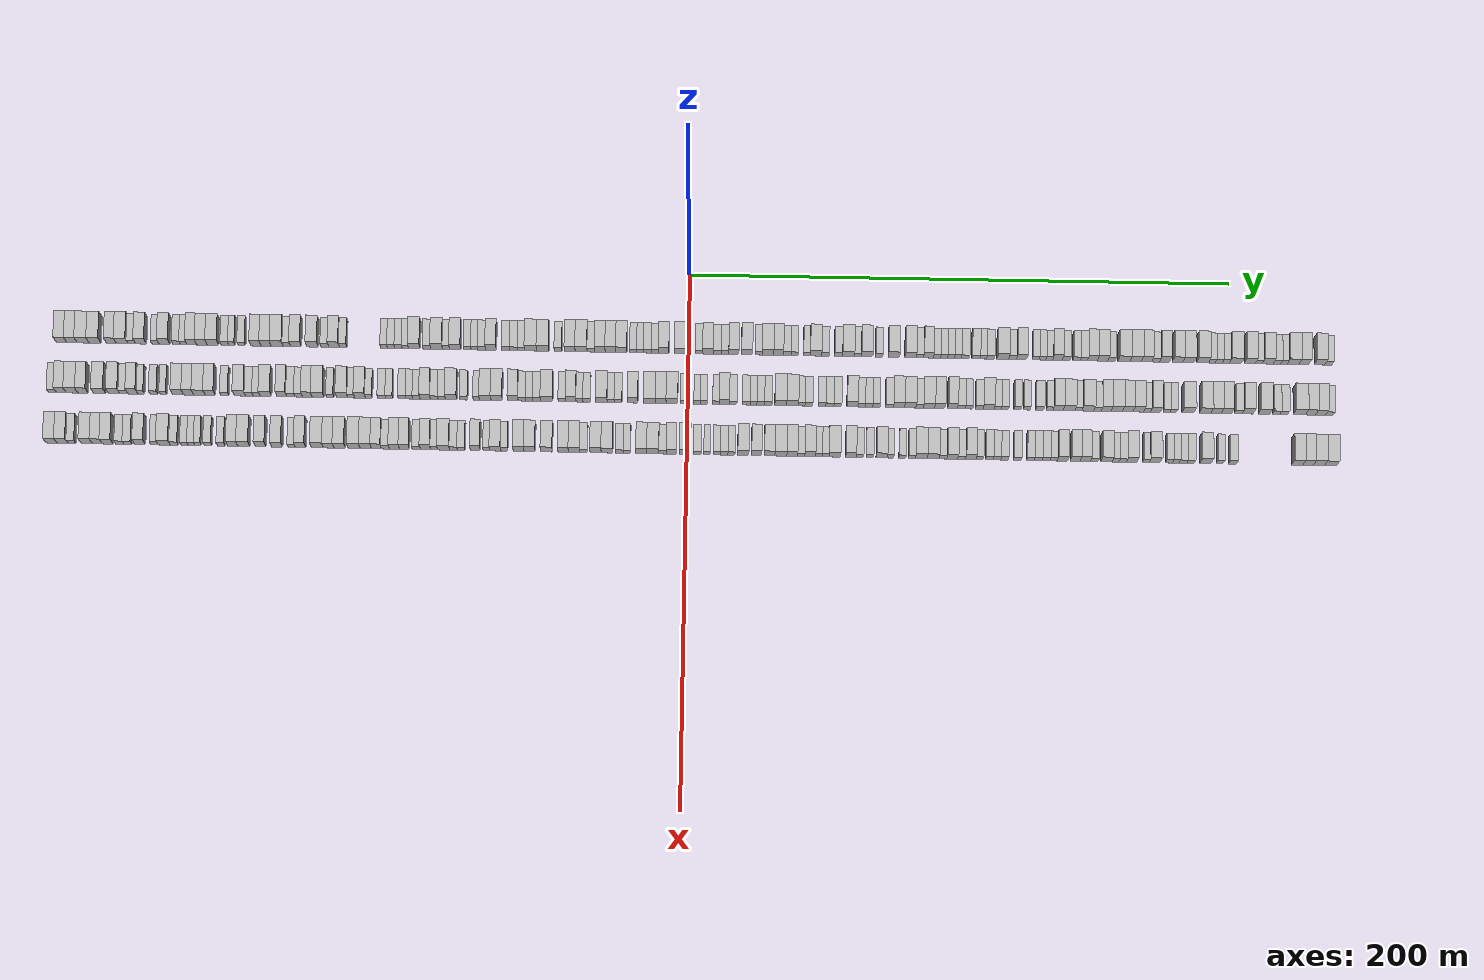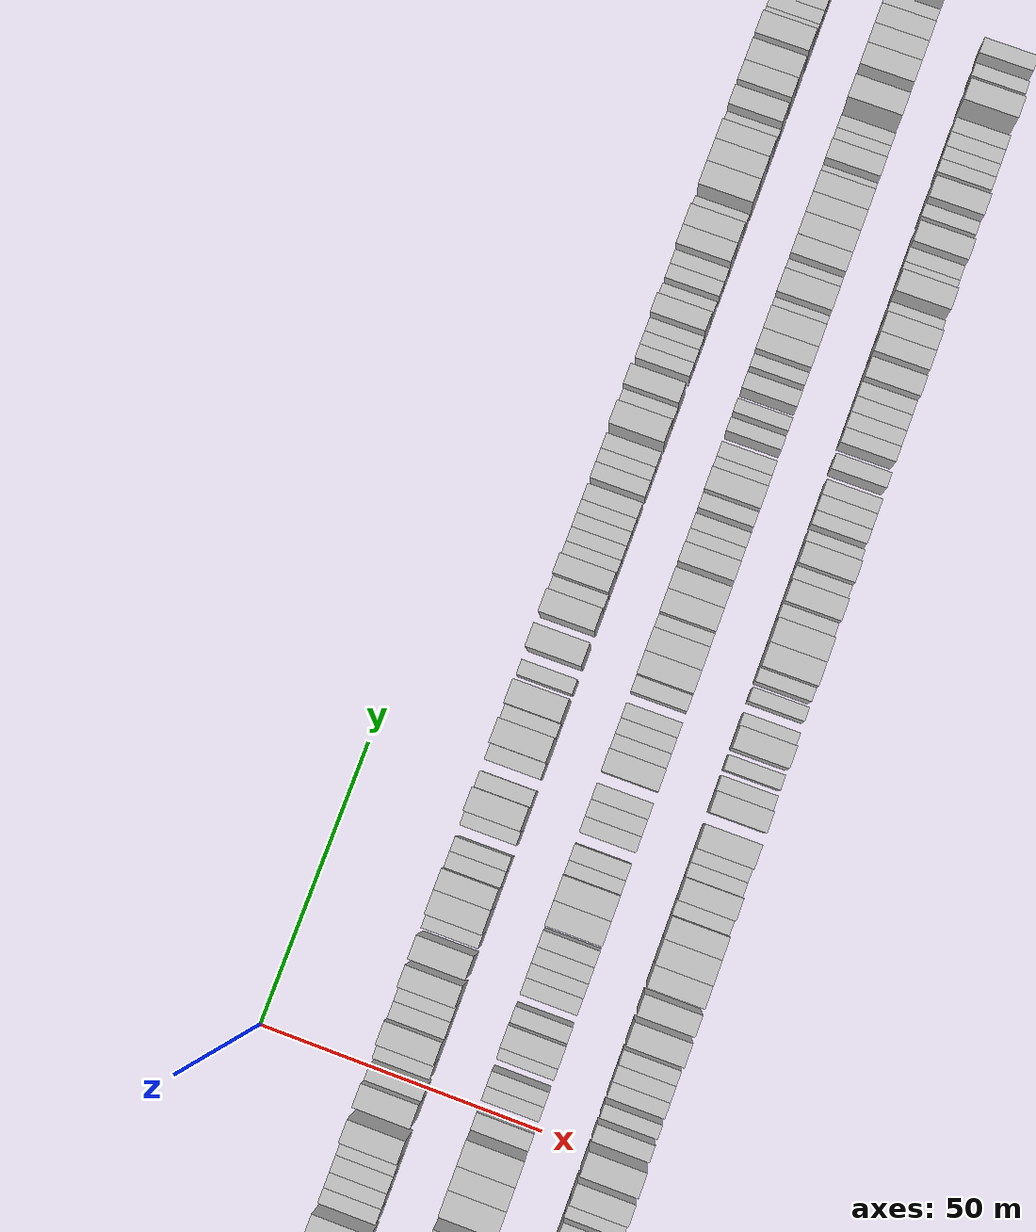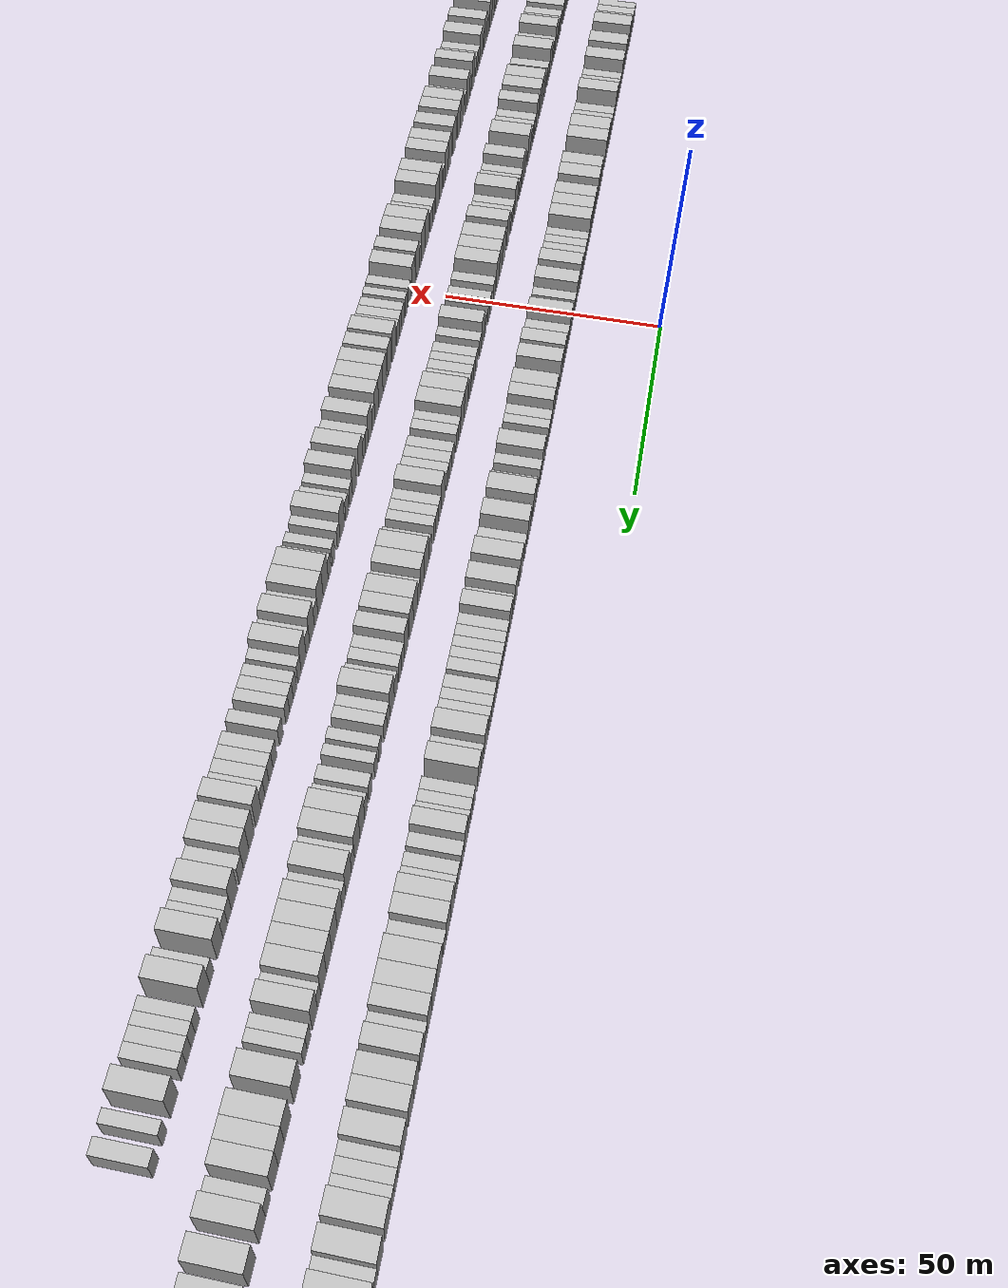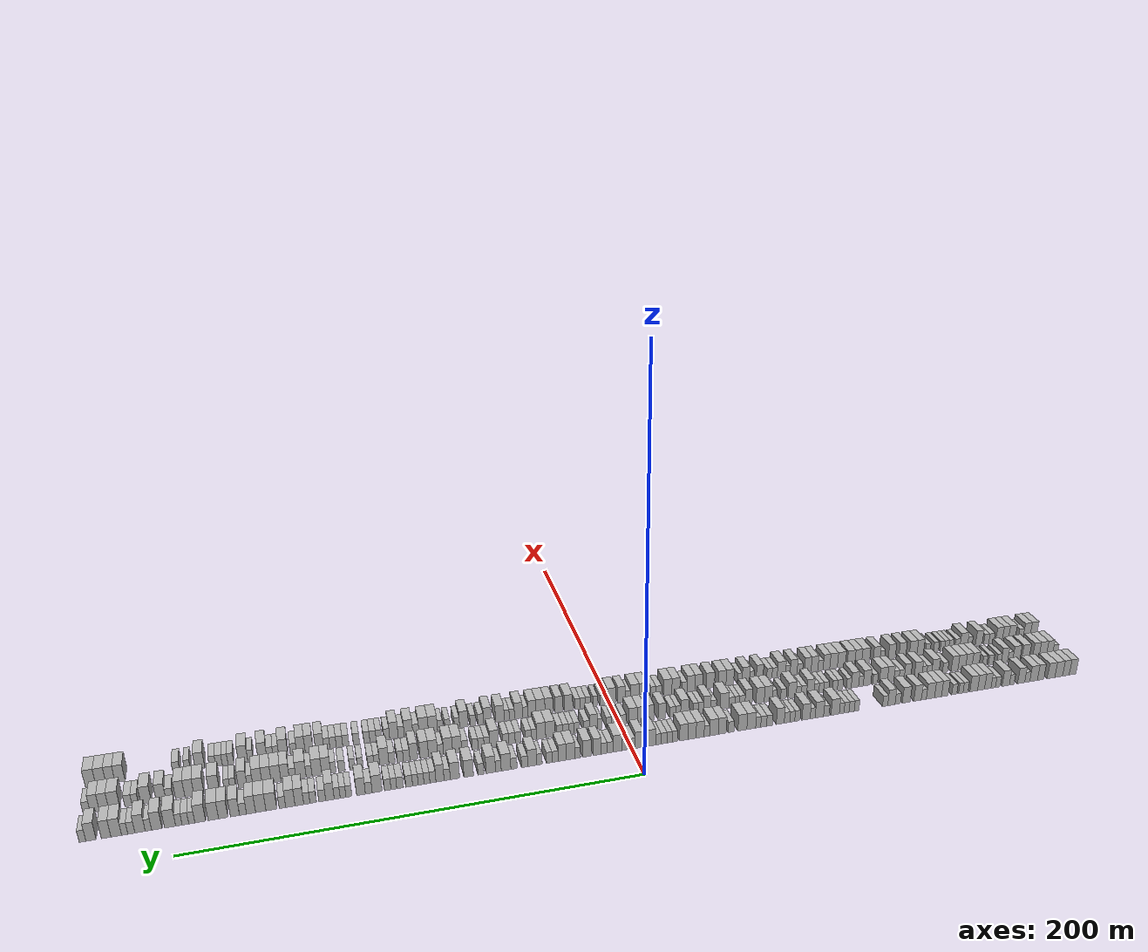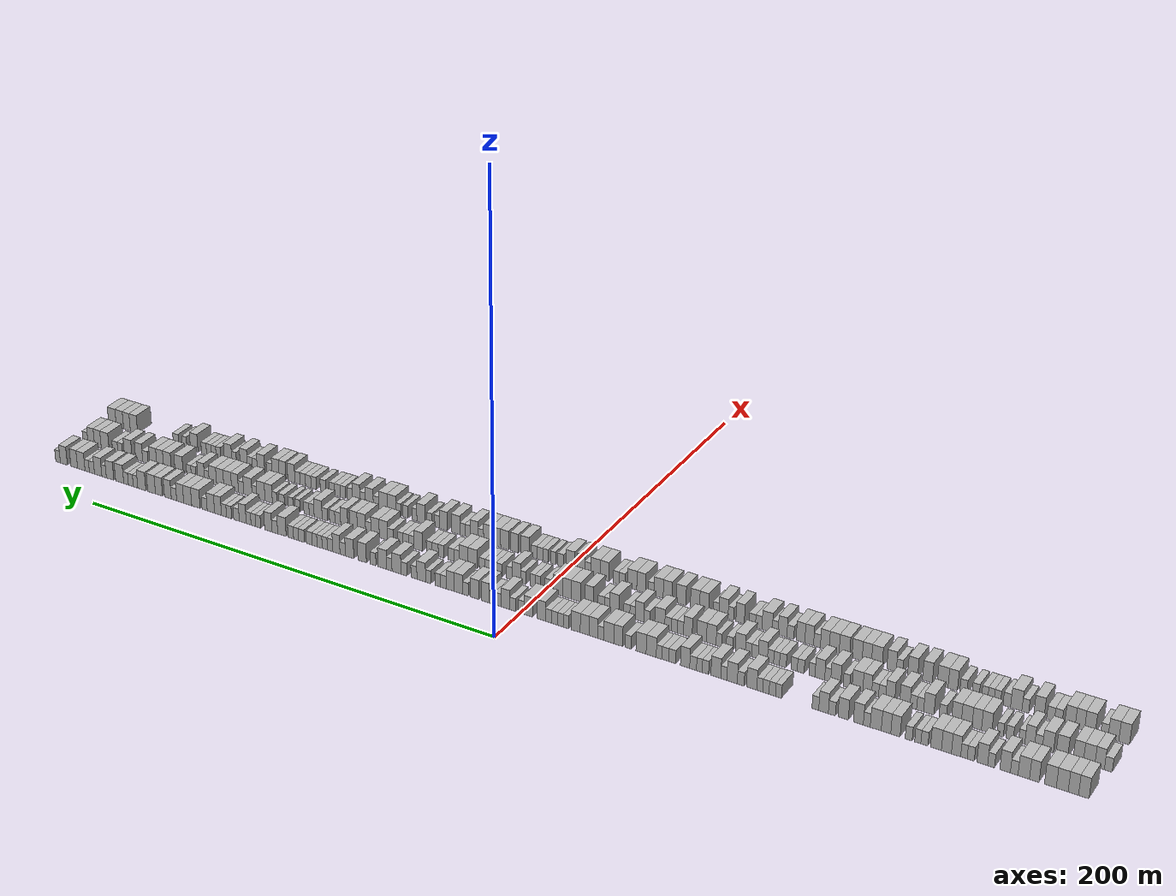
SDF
<sdf version="1.6">
 <world name="default">
  <scene>
   <sky><clouds><speed>12</speed></clouds></sky>
   <ambient>0.4 0.4 0.4 1</ambient>
   <background>0.7 0.7 0.7 1</background>
   <shadows>1</shadows>
  </scene>
  <gravity>0 0 -9.8066</gravity>
  <magnetic_field>6e-06 2.3e-05 -4.2e-05</magnetic_field>
  <physics default="0" name="default_physics" type="ode">
   <ode>
    <solver>
     <type>quick</type>
     <iters>10</iters>
     <sor>1.0</sor>
     <use_dynamic_moi_rescaling>0</use_dynamic_moi_rescaling>
    </solver>
    <constraints>
     <cfm>0</cfm>
     <erp>0.2</erp>
     <contact_max_correcting_vel>100</contact_max_correcting_vel>
     <contact_surface_layer>0.001</contact_surface_layer>
    </constraints>
   </ode>
   <max_step_size>0.004</max_step_size>
   <real_time_factor>1</real_time_factor>
   <real_time_update_rate>250</real_time_update_rate>
  </physics>
  <light name="sun" type="directional">
   <pose>0 0 10 0 0 0</pose>
   <diffuse>0.8 0.8 0.8 1</diffuse>
   <specular>0.2 0.2 0.2 1</specular>
   <attenuation>
    <range>1000</range>
    <constant>0.9</constant>
    <linear>0.01</linear>
    <quadratic>0.001</quadratic>
   </attenuation>
   <direction>-0.5 0.1 -0.9</direction>
  </light>
  <model name="building_1">
   <static>1</static>
   <pose>25.0000 -232.0497 0 0.000000 0.000000 0.000000</pose>
   <link name="link">
    <pose>0 0 4.50 0 0 0</pose>
    <collision name="collision"><geometry><box><size>10.0000 3.9007 9.0000</size></box></geometry></collision>
    <visual name="visual">
     <cast_shadows>0</cast_shadows>
     <geometry><box><size>10.0000 3.9007 9.0000</size></box></geometry>
     <material>
      <script>
       <uri>model://HANNAS_wall/materials/scripts</uri>
       <uri>model://HANNAS_wall/materials/textures</uri>
       <name>vrc/HANNAS_wall</name>
      </script>
     </material>
    </visual>
   </link>
  </model>
  <model name="building_2">
   <static>1</static>
   <pose>25.0000 -228.1832 0 0.000000 0.000000 0.000000</pose>
   <link name="link">
    <pose>0 0 4.50 0 0 0</pose>
    <collision name="collision"><geometry><box><size>10.0000 3.8322 9.0000</size></box></geometry></collision>
    <visual name="visual">
     <cast_shadows>0</cast_shadows>
     <geometry><box><size>10.0000 3.8322 9.0000</size></box></geometry>
     <material>
      <script>
       <uri>model://HANNAS_wall/materials/scripts</uri>
       <uri>model://HANNAS_wall/materials/textures</uri>
       <name>vrc/HANNAS_wall</name>
      </script>
     </material>
    </visual>
   </link>
  </model>
  <model name="building_3">
   <static>1</static>
   <pose>25.0000 -224.0570 0 0.000000 0.000000 0.000000</pose>
   <link name="link">
    <pose>0 0 4.50 0 0 0</pose>
    <collision name="collision"><geometry><box><size>10.0000 4.4203 9.0000</size></box></geometry></collision>
    <visual name="visual">
     <cast_shadows>0</cast_shadows>
     <geometry><box><size>10.0000 4.4203 9.0000</size></box></geometry>
     <material>
      <script>
       <uri>model://HANNAS_wall/materials/scripts</uri>
       <uri>model://HANNAS_wall/materials/textures</uri>
       <name>vrc/HANNAS_wall</name>
      </script>
     </material>
    </visual>
   </link>
  </model>
  <model name="building_4">
   <static>1</static>
   <pose>25.0000 -219.6432 0 0.000000 0.000000 0.000000</pose>
   <link name="link">
    <pose>0 0 4.50 0 0 0</pose>
    <collision name="collision"><geometry><box><size>10.0000 4.4071 9.0000</size></box></geometry></collision>
    <visual name="visual">
     <cast_shadows>0</cast_shadows>
     <geometry><box><size>10.0000 4.4071 9.0000</size></box></geometry>
     <material>
      <script>
       <uri>model://HANNAS_wall/materials/scripts</uri>
       <uri>model://HANNAS_wall/materials/textures</uri>
       <name>vrc/HANNAS_wall</name>
      </script>
     </material>
    </visual>
   </link>
  </model>
  <model name="building_5">
   <static>1</static>
   <pose>25.0000 -213.6147 0 0.000000 0.000000 0.000000</pose>
   <link name="link">
    <pose>0 0 4.50 0 0 0</pose>
    <collision name="collision"><geometry><box><size>10.0000 3.6499 9.0000</size></box></geometry></collision>
    <visual name="visual">
     <cast_shadows>0</cast_shadows>
     <geometry><box><size>10.0000 3.6499 9.0000</size></box></geometry>
     <material>
      <script>
       <uri>model://HANNAS_wall/materials/scripts</uri>
       <uri>model://HANNAS_wall/materials/textures</uri>
       <name>vrc/HANNAS_wall</name>
      </script>
     </material>
    </visual>
   </link>
  </model>
  <model name="building_6">
   <static>1</static>
   <pose>25.0000 -209.6266 0 0.000000 0.000000 0.000000</pose>
   <link name="link">
    <pose>0 0 4.50 0 0 0</pose>
    <collision name="collision"><geometry><box><size>10.0000 4.3262 9.0000</size></box></geometry></collision>
    <visual name="visual">
     <cast_shadows>0</cast_shadows>
     <geometry><box><size>10.0000 4.3262 9.0000</size></box></geometry>
     <material>
      <script>
       <uri>model://HANNAS_wall/materials/scripts</uri>
       <uri>model://HANNAS_wall/materials/textures</uri>
       <name>vrc/HANNAS_wall</name>
      </script>
     </material>
    </visual>
   </link>
  </model>
  <model name="building_7">
   <static>1</static>
   <pose>25.0000 -206.0211 0 0.000000 0.000000 0.000000</pose>
   <link name="link">
    <pose>0 0 3.00 0 0 0</pose>
    <collision name="collision"><geometry><box><size>10.0000 2.8849 6.0000</size></box></geometry></collision>
    <visual name="visual">
     <cast_shadows>0</cast_shadows>
     <geometry><box><size>10.0000 2.8849 6.0000</size></box></geometry>
     <material>
      <script>
       <uri>model://HANNAS_wall/materials/scripts</uri>
       <uri>model://HANNAS_wall/materials/textures</uri>
       <name>vrc/HANNAS_wall</name>
      </script>
     </material>
    </visual>
   </link>
  </model>
  <model name="building_8">
   <static>1</static>
   <pose>25.0000 -202.5647 0 0.000000 0.000000 0.000000</pose>
   <link name="link">
    <pose>0 0 4.50 0 0 0</pose>
    <collision name="collision"><geometry><box><size>10.0000 4.0280 9.0000</size></box></geometry></collision>
    <visual name="visual">
     <cast_shadows>0</cast_shadows>
     <geometry><box><size>10.0000 4.0280 9.0000</size></box></geometry>
     <material>
      <script>
       <uri>model://HANNAS_wall/materials/scripts</uri>
       <uri>model://HANNAS_wall/materials/textures</uri>
       <name>vrc/HANNAS_wall</name>
      </script>
     </material>
    </visual>
   </link>
  </model>
  <model name="building_9">
   <static>1</static>
   <pose>25.0000 -197.2257 0 0.000000 0.000000 0.000000</pose>
   <link name="link">
    <pose>0 0 3.00 0 0 0</pose>
    <collision name="collision"><geometry><box><size>10.0000 2.6500 6.0000</size></box></geometry></collision>
    <visual name="visual">
     <cast_shadows>0</cast_shadows>
     <geometry><box><size>10.0000 2.6500 6.0000</size></box></geometry>
     <material>
      <script>
       <uri>model://HANNAS_wall/materials/scripts</uri>
       <uri>model://HANNAS_wall/materials/textures</uri>
       <name>vrc/HANNAS_wall</name>
      </script>
     </material>
    </visual>
   </link>
  </model>
  <model name="building_10">
   <static>1</static>
   <pose>25.0000 -193.8493 0 0.000000 0.000000 0.000000</pose>
   <link name="link">
    <pose>0 0 4.50 0 0 0</pose>
    <collision name="collision"><geometry><box><size>10.0000 4.1030 9.0000</size></box></geometry></collision>
    <visual name="visual">
     <cast_shadows>0</cast_shadows>
     <geometry><box><size>10.0000 4.1030 9.0000</size></box></geometry>
     <material>
      <script>
       <uri>model://HANNAS_wall/materials/scripts</uri>
       <uri>model://HANNAS_wall/materials/textures</uri>
       <name>vrc/HANNAS_wall</name>
      </script>
     </material>
    </visual>
   </link>
  </model>
  <model name="building_11">
   <static>1</static>
   <pose>25.0000 -189.4213 0 0.000000 0.000000 0.000000</pose>
   <link name="link">
    <pose>0 0 3.00 0 0 0</pose>
    <collision name="collision"><geometry><box><size>10.0000 2.7529 6.0000</size></box></geometry></collision>
    <visual name="visual">
     <cast_shadows>0</cast_shadows>
     <geometry><box><size>10.0000 2.7529 6.0000</size></box></geometry>
     <material>
      <script>
       <uri>model://HANNAS_wall/materials/scripts</uri>
       <uri>model://HANNAS_wall/materials/textures</uri>
       <name>vrc/HANNAS_wall</name>
      </script>
     </material>
    </visual>
   </link>
  </model>
  <model name="building_12">
   <static>1</static>
   <pose>25.0000 -186.8052 0 0.000000 0.000000 0.000000</pose>
   <link name="link">
    <pose>0 0 3.00 0 0 0</pose>
    <collision name="collision"><geometry><box><size>10.0000 2.4793 6.0000</size></box></geometry></collision>
    <visual name="visual">
     <cast_shadows>0</cast_shadows>
     <geometry><box><size>10.0000 2.4793 6.0000</size></box></geometry>
     <material>
      <script>
       <uri>model://HANNAS_wall/materials/scripts</uri>
       <uri>model://HANNAS_wall/materials/textures</uri>
       <name>vrc/HANNAS_wall</name>
      </script>
     </material>
    </visual>
   </link>
  </model>
  <model name="building_13">
   <static>1</static>
   <pose>25.0000 -183.7613 0 0.000000 0.000000 0.000000</pose>
   <link name="link">
    <pose>0 0 4.50 0 0 0</pose>
    <collision name="collision"><geometry><box><size>10.0000 3.6085 9.0000</size></box></geometry></collision>
    <visual name="visual">
     <cast_shadows>0</cast_shadows>
     <geometry><box><size>10.0000 3.6085 9.0000</size></box></geometry>
     <material>
      <script>
       <uri>model://HANNAS_wall/materials/scripts</uri>
       <uri>model://HANNAS_wall/materials/textures</uri>
       <name>vrc/HANNAS_wall</name>
      </script>
     </material>
    </visual>
   </link>
  </model>
  <model name="building_14">
   <static>1</static>
   <pose>25.0000 -180.0130 0 0.000000 0.000000 0.000000</pose>
   <link name="link">
    <pose>0 0 4.50 0 0 0</pose>
    <collision name="collision"><geometry><box><size>10.0000 3.8881 9.0000</size></box></geometry></collision>
    <visual name="visual">
     <cast_shadows>0</cast_shadows>
     <geometry><box><size>10.0000 3.8881 9.0000</size></box></geometry>
     <material>
      <script>
       <uri>model://HANNAS_wall/materials/scripts</uri>
       <uri>model://HANNAS_wall/materials/textures</uri>
       <name>vrc/HANNAS_wall</name>
      </script>
     </material>
    </visual>
   </link>
  </model>
  <model name="building_15">
   <static>1</static>
   <pose>25.0000 -175.9496 0 0.000000 0.000000 0.000000</pose>
   <link name="link">
    <pose>0 0 4.50 0 0 0</pose>
    <collision name="collision"><geometry><box><size>10.0000 4.2389 9.0000</size></box></geometry></collision>
    <visual name="visual">
     <cast_shadows>0</cast_shadows>
     <geometry><box><size>10.0000 4.2389 9.0000</size></box></geometry>
     <material>
      <script>
       <uri>model://HANNAS_wall/materials/scripts</uri>
       <uri>model://HANNAS_wall/materials/textures</uri>
       <name>vrc/HANNAS_wall</name>
      </script>
     </material>
    </visual>
   </link>
  </model>
  <model name="building_16">
   <static>1</static>
   <pose>25.0000 -171.4326 0 0.000000 0.000000 0.000000</pose>
   <link name="link">
    <pose>0 0 3.00 0 0 0</pose>
    <collision name="collision"><geometry><box><size>10.0000 2.7951 6.0000</size></box></geometry></collision>
    <visual name="visual">
     <cast_shadows>0</cast_shadows>
     <geometry><box><size>10.0000 2.7951 6.0000</size></box></geometry>
     <material>
      <script>
       <uri>model://HANNAS_wall/materials/scripts</uri>
       <uri>model://HANNAS_wall/materials/textures</uri>
       <name>vrc/HANNAS_wall</name>
      </script>
     </material>
    </visual>
   </link>
  </model>
  <model name="building_17">
   <static>1</static>
   <pose>25.0000 -168.8290 0 0.000000 0.000000 0.000000</pose>
   <link name="link">
    <pose>0 0 3.00 0 0 0</pose>
    <collision name="collision"><geometry><box><size>10.0000 2.4120 6.0000</size></box></geometry></collision>
    <visual name="visual">
     <cast_shadows>0</cast_shadows>
     <geometry><box><size>10.0000 2.4120 6.0000</size></box></geometry>
     <material>
      <script>
       <uri>model://HANNAS_wall/materials/scripts</uri>
       <uri>model://HANNAS_wall/materials/textures</uri>
       <name>vrc/HANNAS_wall</name>
      </script>
     </material>
    </visual>
   </link>
  </model>
  <model name="building_18">
   <static>1</static>
   <pose>25.0000 -165.2349 0 0.000000 0.000000 0.000000</pose>
   <link name="link">
    <pose>0 0 3.00 0 0 0</pose>
    <collision name="collision"><geometry><box><size>10.0000 2.7762 6.0000</size></box></geometry></collision>
    <visual name="visual">
     <cast_shadows>0</cast_shadows>
     <geometry><box><size>10.0000 2.7762 6.0000</size></box></geometry>
     <material>
      <script>
       <uri>model://HANNAS_wall/materials/scripts</uri>
       <uri>model://HANNAS_wall/materials/textures</uri>
       <name>vrc/HANNAS_wall</name>
      </script>
     </material>
    </visual>
   </link>
  </model>
  <model name="building_19">
   <static>1</static>
   <pose>25.0000 -160.0012 0 0.000000 0.000000 0.000000</pose>
   <link name="link">
    <pose>0 0 4.50 0 0 0</pose>
    <collision name="collision"><geometry><box><size>10.0000 3.6912 9.0000</size></box></geometry></collision>
    <visual name="visual">
     <cast_shadows>0</cast_shadows>
     <geometry><box><size>10.0000 3.6912 9.0000</size></box></geometry>
     <material>
      <script>
       <uri>model://HANNAS_wall/materials/scripts</uri>
       <uri>model://HANNAS_wall/materials/textures</uri>
       <name>vrc/HANNAS_wall</name>
      </script>
     </material>
    </visual>
   </link>
  </model>
  <model name="building_20">
   <static>1</static>
   <pose>25.0000 -156.2559 0 0.000000 0.000000 0.000000</pose>
   <link name="link">
    <pose>0 0 4.50 0 0 0</pose>
    <collision name="collision"><geometry><box><size>10.0000 3.7994 9.0000</size></box></geometry></collision>
    <visual name="visual">
     <cast_shadows>0</cast_shadows>
     <geometry><box><size>10.0000 3.7994 9.0000</size></box></geometry>
     <material>
      <script>
       <uri>model://HANNAS_wall/materials/scripts</uri>
       <uri>model://HANNAS_wall/materials/textures</uri>
       <name>vrc/HANNAS_wall</name>
      </script>
     </material>
    </visual>
   </link>
  </model>
  <model name="building_21">
   <static>1</static>
   <pose>25.0000 -152.1520 0 0.000000 0.000000 0.000000</pose>
   <link name="link">
    <pose>0 0 4.50 0 0 0</pose>
    <collision name="collision"><geometry><box><size>10.0000 4.4084 9.0000</size></box></geometry></collision>
    <visual name="visual">
     <cast_shadows>0</cast_shadows>
     <geometry><box><size>10.0000 4.4084 9.0000</size></box></geometry>
     <material>
      <script>
       <uri>model://HANNAS_wall/materials/scripts</uri>
       <uri>model://HANNAS_wall/materials/textures</uri>
       <name>vrc/HANNAS_wall</name>
      </script>
     </material>
    </visual>
   </link>
  </model>
  <model name="building_22">
   <static>1</static>
   <pose>25.0000 -148.5729 0 0.000000 0.000000 0.000000</pose>
   <link name="link">
    <pose>0 0 3.00 0 0 0</pose>
    <collision name="collision"><geometry><box><size>10.0000 2.7499 6.0000</size></box></geometry></collision>
    <visual name="visual">
     <cast_shadows>0</cast_shadows>
     <geometry><box><size>10.0000 2.7499 6.0000</size></box></geometry>
     <material>
      <script>
       <uri>model://HANNAS_wall/materials/scripts</uri>
       <uri>model://HANNAS_wall/materials/textures</uri>
       <name>vrc/HANNAS_wall</name>
      </script>
     </material>
    </visual>
   </link>
  </model>
  <model name="building_23">
   <static>1</static>
   <pose>25.0000 -145.1866 0 0.000000 0.000000 0.000000</pose>
   <link name="link">
    <pose>0 0 4.50 0 0 0</pose>
    <collision name="collision"><geometry><box><size>10.0000 4.0226 9.0000</size></box></geometry></collision>
    <visual name="visual">
     <cast_shadows>0</cast_shadows>
     <geometry><box><size>10.0000 4.0226 9.0000</size></box></geometry>
     <material>
      <script>
       <uri>model://HANNAS_wall/materials/scripts</uri>
       <uri>model://HANNAS_wall/materials/textures</uri>
       <name>vrc/HANNAS_wall</name>
      </script>
     </material>
    </visual>
   </link>
  </model>
  <model name="building_24">
   <static>1</static>
   <pose>25.0000 -139.0597 0 0.000000 0.000000 0.000000</pose>
   <link name="link">
    <pose>0 0 4.50 0 0 0</pose>
    <collision name="collision"><geometry><box><size>10.0000 4.2311 9.0000</size></box></geometry></collision>
    <visual name="visual">
     <cast_shadows>0</cast_shadows>
     <geometry><box><size>10.0000 4.2311 9.0000</size></box></geometry>
     <material>
      <script>
       <uri>model://HANNAS_wall/materials/scripts</uri>
       <uri>model://HANNAS_wall/materials/textures</uri>
       <name>vrc/HANNAS_wall</name>
      </script>
     </material>
    </visual>
   </link>
  </model>
  <model name="building_25">
   <static>1</static>
   <pose>25.0000 -134.4918 0 0.000000 0.000000 0.000000</pose>
   <link name="link">
    <pose>0 0 3.00 0 0 0</pose>
    <collision name="collision"><geometry><box><size>10.0000 2.9048 6.0000</size></box></geometry></collision>
    <visual name="visual">
     <cast_shadows>0</cast_shadows>
     <geometry><box><size>10.0000 2.9048 6.0000</size></box></geometry>
     <material>
      <script>
       <uri>model://HANNAS_wall/materials/scripts</uri>
       <uri>model://HANNAS_wall/materials/textures</uri>
       <name>vrc/HANNAS_wall</name>
      </script>
     </material>
    </visual>
   </link>
  </model>
  <model name="building_26">
   <static>1</static>
   <pose>25.0000 -131.0836 0 0.000000 0.000000 0.000000</pose>
   <link name="link">
    <pose>0 0 4.50 0 0 0</pose>
    <collision name="collision"><geometry><box><size>10.0000 3.9116 9.0000</size></box></geometry></collision>
    <visual name="visual">
     <cast_shadows>0</cast_shadows>
     <geometry><box><size>10.0000 3.9116 9.0000</size></box></geometry>
     <material>
      <script>
       <uri>model://HANNAS_wall/materials/scripts</uri>
       <uri>model://HANNAS_wall/materials/textures</uri>
       <name>vrc/HANNAS_wall</name>
      </script>
     </material>
    </visual>
   </link>
  </model>
  <model name="building_27">
   <static>1</static>
   <pose>25.0000 -127.7431 0 0.000000 0.000000 0.000000</pose>
   <link name="link">
    <pose>0 0 3.00 0 0 0</pose>
    <collision name="collision"><geometry><box><size>10.0000 2.7693 6.0000</size></box></geometry></collision>
    <visual name="visual">
     <cast_shadows>0</cast_shadows>
     <geometry><box><size>10.0000 2.7693 6.0000</size></box></geometry>
     <material>
      <script>
       <uri>model://HANNAS_wall/materials/scripts</uri>
       <uri>model://HANNAS_wall/materials/textures</uri>
       <name>vrc/HANNAS_wall</name>
      </script>
     </material>
    </visual>
   </link>
  </model>
  <model name="building_28">
   <static>1</static>
   <pose>25.0000 -112.5981 0 0.000000 0.000000 0.000000</pose>
   <link name="link">
    <pose>0 0 3.00 0 0 0</pose>
    <collision name="collision"><geometry><box><size>10.0000 2.5069 6.0000</size></box></geometry></collision>
    <visual name="visual">
     <cast_shadows>0</cast_shadows>
     <geometry><box><size>10.0000 2.5069 6.0000</size></box></geometry>
     <material>
      <script>
       <uri>model://HANNAS_wall/materials/scripts</uri>
       <uri>model://HANNAS_wall/materials/textures</uri>
       <name>vrc/HANNAS_wall</name>
      </script>
     </material>
    </visual>
   </link>
  </model>
  <model name="building_29">
   <static>1</static>
   <pose>25.0000 -109.9753 0 0.000000 0.000000 0.000000</pose>
   <link name="link">
    <pose>0 0 3.00 0 0 0</pose>
    <collision name="collision"><geometry><box><size>10.0000 2.7387 6.0000</size></box></geometry></collision>
    <visual name="visual">
     <cast_shadows>0</cast_shadows>
     <geometry><box><size>10.0000 2.7387 6.0000</size></box></geometry>
     <material>
      <script>
       <uri>model://HANNAS_wall/materials/scripts</uri>
       <uri>model://HANNAS_wall/materials/textures</uri>
       <name>vrc/HANNAS_wall</name>
      </script>
     </material>
    </visual>
   </link>
  </model>
  <model name="building_30">
   <static>1</static>
   <pose>25.0000 -107.2891 0 0.000000 0.000000 0.000000</pose>
   <link name="link">
    <pose>0 0 3.00 0 0 0</pose>
    <collision name="collision"><geometry><box><size>10.0000 2.6337 6.0000</size></box></geometry></collision>
    <visual name="visual">
     <cast_shadows>0</cast_shadows>
     <geometry><box><size>10.0000 2.6337 6.0000</size></box></geometry>
     <material>
      <script>
       <uri>model://HANNAS_wall/materials/scripts</uri>
       <uri>model://HANNAS_wall/materials/textures</uri>
       <name>vrc/HANNAS_wall</name>
      </script>
     </material>
    </visual>
   </link>
  </model>
  <model name="building_31">
   <static>1</static>
   <pose>25.0000 -104.7487 0 0.000000 0.000000 0.000000</pose>
   <link name="link">
    <pose>0 0 3.00 0 0 0</pose>
    <collision name="collision"><geometry><box><size>10.0000 2.4472 6.0000</size></box></geometry></collision>
    <visual name="visual">
     <cast_shadows>0</cast_shadows>
     <geometry><box><size>10.0000 2.4472 6.0000</size></box></geometry>
     <material>
      <script>
       <uri>model://HANNAS_wall/materials/scripts</uri>
       <uri>model://HANNAS_wall/materials/textures</uri>
       <name>vrc/HANNAS_wall</name>
      </script>
     </material>
    </visual>
   </link>
  </model>
  <model name="building_32">
   <static>1</static>
   <pose>25.0000 -101.3628 0 0.000000 0.000000 0.000000</pose>
   <link name="link">
    <pose>0 0 4.50 0 0 0</pose>
    <collision name="collision"><geometry><box><size>10.0000 4.3246 9.0000</size></box></geometry></collision>
    <visual name="visual">
     <cast_shadows>0</cast_shadows>
     <geometry><box><size>10.0000 4.3246 9.0000</size></box></geometry>
     <material>
      <script>
       <uri>model://HANNAS_wall/materials/scripts</uri>
       <uri>model://HANNAS_wall/materials/textures</uri>
       <name>vrc/HANNAS_wall</name>
      </script>
     </material>
    </visual>
   </link>
  </model>
  <model name="building_33">
   <static>1</static>
   <pose>25.0000 -96.7619 0 0.000000 0.000000 0.000000</pose>
   <link name="link">
    <pose>0 0 3.00 0 0 0</pose>
    <collision name="collision"><geometry><box><size>10.0000 2.8772 6.0000</size></box></geometry></collision>
    <visual name="visual">
     <cast_shadows>0</cast_shadows>
     <geometry><box><size>10.0000 2.8772 6.0000</size></box></geometry>
     <material>
      <script>
       <uri>model://HANNAS_wall/materials/scripts</uri>
       <uri>model://HANNAS_wall/materials/textures</uri>
       <name>vrc/HANNAS_wall</name>
      </script>
     </material>
    </visual>
   </link>
  </model>
  <model name="building_34">
   <static>1</static>
   <pose>25.0000 -93.1212 0 0.000000 0.000000 0.000000</pose>
   <link name="link">
    <pose>0 0 4.50 0 0 0</pose>
    <collision name="collision"><geometry><box><size>10.0000 4.4043 9.0000</size></box></geometry></collision>
    <visual name="visual">
     <cast_shadows>0</cast_shadows>
     <geometry><box><size>10.0000 4.4043 9.0000</size></box></geometry>
     <material>
      <script>
       <uri>model://HANNAS_wall/materials/scripts</uri>
       <uri>model://HANNAS_wall/materials/textures</uri>
       <name>vrc/HANNAS_wall</name>
      </script>
     </material>
    </visual>
   </link>
  </model>
  <model name="building_35">
   <static>1</static>
   <pose>25.0000 -89.6318 0 0.000000 0.000000 0.000000</pose>
   <link name="link">
    <pose>0 0 3.00 0 0 0</pose>
    <collision name="collision"><geometry><box><size>10.0000 2.5744 6.0000</size></box></geometry></collision>
    <visual name="visual">
     <cast_shadows>0</cast_shadows>
     <geometry><box><size>10.0000 2.5744 6.0000</size></box></geometry>
     <material>
      <script>
       <uri>model://HANNAS_wall/materials/scripts</uri>
       <uri>model://HANNAS_wall/materials/textures</uri>
       <name>vrc/HANNAS_wall</name>
      </script>
     </material>
    </visual>
   </link>
  </model>
  <model name="building_36">
   <static>1</static>
   <pose>25.0000 -86.2331 0 0.000000 0.000000 0.000000</pose>
   <link name="link">
    <pose>0 0 4.50 0 0 0</pose>
    <collision name="collision"><geometry><box><size>10.0000 4.2231 9.0000</size></box></geometry></collision>
    <visual name="visual">
     <cast_shadows>0</cast_shadows>
     <geometry><box><size>10.0000 4.2231 9.0000</size></box></geometry>
     <material>
      <script>
       <uri>model://HANNAS_wall/materials/scripts</uri>
       <uri>model://HANNAS_wall/materials/textures</uri>
       <name>vrc/HANNAS_wall</name>
      </script>
     </material>
    </visual>
   </link>
  </model>
  <model name="building_37">
   <static>1</static>
   <pose>25.0000 -81.7671 0 0.000000 0.000000 0.000000</pose>
   <link name="link">
    <pose>0 0 3.00 0 0 0</pose>
    <collision name="collision"><geometry><box><size>10.0000 2.7089 6.0000</size></box></geometry></collision>
    <visual name="visual">
     <cast_shadows>0</cast_shadows>
     <geometry><box><size>10.0000 2.7089 6.0000</size></box></geometry>
     <material>
      <script>
       <uri>model://HANNAS_wall/materials/scripts</uri>
       <uri>model://HANNAS_wall/materials/textures</uri>
       <name>vrc/HANNAS_wall</name>
      </script>
     </material>
    </visual>
   </link>
  </model>
  <model name="building_38">
   <static>1</static>
   <pose>25.0000 -79.1768 0 0.000000 0.000000 0.000000</pose>
   <link name="link">
    <pose>0 0 3.00 0 0 0</pose>
    <collision name="collision"><geometry><box><size>10.0000 2.4715 6.0000</size></box></geometry></collision>
    <visual name="visual">
     <cast_shadows>0</cast_shadows>
     <geometry><box><size>10.0000 2.4715 6.0000</size></box></geometry>
     <material>
      <script>
       <uri>model://HANNAS_wall/materials/scripts</uri>
       <uri>model://HANNAS_wall/materials/textures</uri>
       <name>vrc/HANNAS_wall</name>
      </script>
     </material>
    </visual>
   </link>
  </model>
  <model name="building_39">
   <static>1</static>
   <pose>25.0000 -76.4814 0 0.000000 0.000000 0.000000</pose>
   <link name="link">
    <pose>0 0 3.00 0 0 0</pose>
    <collision name="collision"><geometry><box><size>10.0000 2.9194 6.0000</size></box></geometry></collision>
    <visual name="visual">
     <cast_shadows>0</cast_shadows>
     <geometry><box><size>10.0000 2.9194 6.0000</size></box></geometry>
     <material>
      <script>
       <uri>model://HANNAS_wall/materials/scripts</uri>
       <uri>model://HANNAS_wall/materials/textures</uri>
       <name>vrc/HANNAS_wall</name>
      </script>
     </material>
    </visual>
   </link>
  </model>
  <model name="building_40">
   <static>1</static>
   <pose>25.0000 -73.0210 0 0.000000 0.000000 0.000000</pose>
   <link name="link">
    <pose>0 0 4.50 0 0 0</pose>
    <collision name="collision"><geometry><box><size>10.0000 4.0014 9.0000</size></box></geometry></collision>
    <visual name="visual">
     <cast_shadows>0</cast_shadows>
     <geometry><box><size>10.0000 4.0014 9.0000</size></box></geometry>
     <material>
      <script>
       <uri>model://HANNAS_wall/materials/scripts</uri>
       <uri>model://HANNAS_wall/materials/textures</uri>
       <name>vrc/HANNAS_wall</name>
      </script>
     </material>
    </visual>
   </link>
  </model>
  <model name="building_41">
   <static>1</static>
   <pose>25.0000 -67.5345 0 0.000000 0.000000 0.000000</pose>
   <link name="link">
    <pose>0 0 3.00 0 0 0</pose>
    <collision name="collision"><geometry><box><size>10.0000 2.9716 6.0000</size></box></geometry></collision>
    <visual name="visual">
     <cast_shadows>0</cast_shadows>
     <geometry><box><size>10.0000 2.9716 6.0000</size></box></geometry>
     <material>
      <script>
       <uri>model://HANNAS_wall/materials/scripts</uri>
       <uri>model://HANNAS_wall/materials/textures</uri>
       <name>vrc/HANNAS_wall</name>
      </script>
     </material>
    </visual>
   </link>
  </model>
  <model name="building_42">
   <static>1</static>
   <pose>25.0000 -64.5715 0 0.000000 0.000000 0.000000</pose>
   <link name="link">
    <pose>0 0 3.00 0 0 0</pose>
    <collision name="collision"><geometry><box><size>10.0000 2.9545 6.0000</size></box></geometry></collision>
    <visual name="visual">
     <cast_shadows>0</cast_shadows>
     <geometry><box><size>10.0000 2.9545 6.0000</size></box></geometry>
     <material>
      <script>
       <uri>model://HANNAS_wall/materials/scripts</uri>
       <uri>model://HANNAS_wall/materials/textures</uri>
       <name>vrc/HANNAS_wall</name>
      </script>
     </material>
    </visual>
   </link>
  </model>
  <model name="building_43">
   <static>1</static>
   <pose>25.0000 -61.8195 0 0.000000 0.000000 0.000000</pose>
   <link name="link">
    <pose>0 0 3.00 0 0 0</pose>
    <collision name="collision"><geometry><box><size>10.0000 2.5494 6.0000</size></box></geometry></collision>
    <visual name="visual">
     <cast_shadows>0</cast_shadows>
     <geometry><box><size>10.0000 2.5494 6.0000</size></box></geometry>
     <material>
      <script>
       <uri>model://HANNAS_wall/materials/scripts</uri>
       <uri>model://HANNAS_wall/materials/textures</uri>
       <name>vrc/HANNAS_wall</name>
      </script>
     </material>
    </visual>
   </link>
  </model>
  <model name="building_44">
   <static>1</static>
   <pose>25.0000 -58.3262 0 0.000000 0.000000 0.000000</pose>
   <link name="link">
    <pose>0 0 4.50 0 0 0</pose>
    <collision name="collision"><geometry><box><size>10.0000 4.4372 9.0000</size></box></geometry></collision>
    <visual name="visual">
     <cast_shadows>0</cast_shadows>
     <geometry><box><size>10.0000 4.4372 9.0000</size></box></geometry>
     <material>
      <script>
       <uri>model://HANNAS_wall/materials/scripts</uri>
       <uri>model://HANNAS_wall/materials/textures</uri>
       <name>vrc/HANNAS_wall</name>
      </script>
     </material>
    </visual>
   </link>
  </model>
  <model name="building_45">
   <static>1</static>
   <pose>25.0000 -53.8707 0 0.000000 0.000000 0.000000</pose>
   <link name="link">
    <pose>0 0 4.50 0 0 0</pose>
    <collision name="collision"><geometry><box><size>10.0000 4.4738 9.0000</size></box></geometry></collision>
    <visual name="visual">
     <cast_shadows>0</cast_shadows>
     <geometry><box><size>10.0000 4.4738 9.0000</size></box></geometry>
     <material>
      <script>
       <uri>model://HANNAS_wall/materials/scripts</uri>
       <uri>model://HANNAS_wall/materials/textures</uri>
       <name>vrc/HANNAS_wall</name>
      </script>
     </material>
    </visual>
   </link>
  </model>
  <model name="building_46">
   <static>1</static>
   <pose>25.0000 -48.2226 0 0.000000 0.000000 0.000000</pose>
   <link name="link">
    <pose>0 0 3.00 0 0 0</pose>
    <collision name="collision"><geometry><box><size>10.0000 2.8224 6.0000</size></box></geometry></collision>
    <visual name="visual">
     <cast_shadows>0</cast_shadows>
     <geometry><box><size>10.0000 2.8224 6.0000</size></box></geometry>
     <material>
      <script>
       <uri>model://HANNAS_wall/materials/scripts</uri>
       <uri>model://HANNAS_wall/materials/textures</uri>
       <name>vrc/HANNAS_wall</name>
      </script>
     </material>
    </visual>
   </link>
  </model>
  <model name="building_47">
   <static>1</static>
   <pose>25.0000 -43.8459 0 0.000000 0.000000 0.000000</pose>
   <link name="link">
    <pose>0 0 4.50 0 0 0</pose>
    <collision name="collision"><geometry><box><size>10.0000 3.9311 9.0000</size></box></geometry></collision>
    <visual name="visual">
     <cast_shadows>0</cast_shadows>
     <geometry><box><size>10.0000 3.9311 9.0000</size></box></geometry>
     <material>
      <script>
       <uri>model://HANNAS_wall/materials/scripts</uri>
       <uri>model://HANNAS_wall/materials/textures</uri>
       <name>vrc/HANNAS_wall</name>
      </script>
     </material>
    </visual>
   </link>
  </model>
  <model name="building_48">
   <static>1</static>
   <pose>25.0000 -39.6788 0 0.000000 0.000000 0.000000</pose>
   <link name="link">
    <pose>0 0 4.50 0 0 0</pose>
    <collision name="collision"><geometry><box><size>10.0000 4.4031 9.0000</size></box></geometry></collision>
    <visual name="visual">
     <cast_shadows>0</cast_shadows>
     <geometry><box><size>10.0000 4.4031 9.0000</size></box></geometry>
     <material>
      <script>
       <uri>model://HANNAS_wall/materials/scripts</uri>
       <uri>model://HANNAS_wall/materials/textures</uri>
       <name>vrc/HANNAS_wall</name>
      </script>
     </material>
    </visual>
   </link>
  </model>
  <model name="building_49">
   <static>1</static>
   <pose>25.0000 -36.1139 0 0.000000 0.000000 0.000000</pose>
   <link name="link">
    <pose>0 0 3.00 0 0 0</pose>
    <collision name="collision"><geometry><box><size>10.0000 2.7268 6.0000</size></box></geometry></collision>
    <visual name="visual">
     <cast_shadows>0</cast_shadows>
     <geometry><box><size>10.0000 2.7268 6.0000</size></box></geometry>
     <material>
      <script>
       <uri>model://HANNAS_wall/materials/scripts</uri>
       <uri>model://HANNAS_wall/materials/textures</uri>
       <name>vrc/HANNAS_wall</name>
      </script>
     </material>
    </visual>
   </link>
  </model>
  <model name="building_50">
   <static>1</static>
   <pose>25.0000 -32.7789 0 0.000000 0.000000 0.000000</pose>
   <link name="link">
    <pose>0 0 4.50 0 0 0</pose>
    <collision name="collision"><geometry><box><size>10.0000 3.9430 9.0000</size></box></geometry></collision>
    <visual name="visual">
     <cast_shadows>0</cast_shadows>
     <geometry><box><size>10.0000 3.9430 9.0000</size></box></geometry>
     <material>
      <script>
       <uri>model://HANNAS_wall/materials/scripts</uri>
       <uri>model://HANNAS_wall/materials/textures</uri>
       <name>vrc/HANNAS_wall</name>
      </script>
     </material>
    </visual>
   </link>
  </model>
  <model name="building_51">
   <static>1</static>
   <pose>25.0000 -28.8293 0 0.000000 0.000000 0.000000</pose>
   <link name="link">
    <pose>0 0 4.50 0 0 0</pose>
    <collision name="collision"><geometry><box><size>10.0000 3.9562 9.0000</size></box></geometry></collision>
    <visual name="visual">
     <cast_shadows>0</cast_shadows>
     <geometry><box><size>10.0000 3.9562 9.0000</size></box></geometry>
     <material>
      <script>
       <uri>model://HANNAS_wall/materials/scripts</uri>
       <uri>model://HANNAS_wall/materials/textures</uri>
       <name>vrc/HANNAS_wall</name>
      </script>
     </material>
    </visual>
   </link>
  </model>
  <model name="building_52">
   <static>1</static>
   <pose>25.0000 -24.7920 0 0.000000 0.000000 0.000000</pose>
   <link name="link">
    <pose>0 0 4.50 0 0 0</pose>
    <collision name="collision"><geometry><box><size>10.0000 4.1183 9.0000</size></box></geometry></collision>
    <visual name="visual">
     <cast_shadows>0</cast_shadows>
     <geometry><box><size>10.0000 4.1183 9.0000</size></box></geometry>
     <material>
      <script>
       <uri>model://HANNAS_wall/materials/scripts</uri>
       <uri>model://HANNAS_wall/materials/textures</uri>
       <name>vrc/HANNAS_wall</name>
      </script>
     </material>
    </visual>
   </link>
  </model>
  <model name="building_53">
   <static>1</static>
   <pose>25.0000 -20.4421 0 0.000000 0.000000 0.000000</pose>
   <link name="link">
    <pose>0 0 3.00 0 0 0</pose>
    <collision name="collision"><geometry><box><size>10.0000 2.5815 6.0000</size></box></geometry></collision>
    <visual name="visual">
     <cast_shadows>0</cast_shadows>
     <geometry><box><size>10.0000 2.5815 6.0000</size></box></geometry>
     <material>
      <script>
       <uri>model://HANNAS_wall/materials/scripts</uri>
       <uri>model://HANNAS_wall/materials/textures</uri>
       <name>vrc/HANNAS_wall</name>
      </script>
     </material>
    </visual>
   </link>
  </model>
  <model name="building_54">
   <static>1</static>
   <pose>25.0000 -17.8780 0 0.000000 0.000000 0.000000</pose>
   <link name="link">
    <pose>0 0 3.00 0 0 0</pose>
    <collision name="collision"><geometry><box><size>10.0000 2.5468 6.0000</size></box></geometry></collision>
    <visual name="visual">
     <cast_shadows>0</cast_shadows>
     <geometry><box><size>10.0000 2.5468 6.0000</size></box></geometry>
     <material>
      <script>
       <uri>model://HANNAS_wall/materials/scripts</uri>
       <uri>model://HANNAS_wall/materials/textures</uri>
       <name>vrc/HANNAS_wall</name>
      </script>
     </material>
    </visual>
   </link>
  </model>
  <model name="building_55">
   <static>1</static>
   <pose>25.0000 -15.1746 0 0.000000 0.000000 0.000000</pose>
   <link name="link">
    <pose>0 0 3.00 0 0 0</pose>
    <collision name="collision"><geometry><box><size>10.0000 2.8601 6.0000</size></box></geometry></collision>
    <visual name="visual">
     <cast_shadows>0</cast_shadows>
     <geometry><box><size>10.0000 2.8601 6.0000</size></box></geometry>
     <material>
      <script>
       <uri>model://HANNAS_wall/materials/scripts</uri>
       <uri>model://HANNAS_wall/materials/textures</uri>
       <name>vrc/HANNAS_wall</name>
      </script>
     </material>
    </visual>
   </link>
  </model>
  <model name="building_56">
   <static>1</static>
   <pose>25.0000 -12.4205 0 0.000000 0.000000 0.000000</pose>
   <link name="link">
    <pose>0 0 3.00 0 0 0</pose>
    <collision name="collision"><geometry><box><size>10.0000 2.6481 6.0000</size></box></geometry></collision>
    <visual name="visual">
     <cast_shadows>0</cast_shadows>
     <geometry><box><size>10.0000 2.6481 6.0000</size></box></geometry>
     <material>
      <script>
       <uri>model://HANNAS_wall/materials/scripts</uri>
       <uri>model://HANNAS_wall/materials/textures</uri>
       <name>vrc/HANNAS_wall</name>
      </script>
     </material>
    </visual>
   </link>
  </model>
  <model name="building_57">
   <static>1</static>
   <pose>25.0000 -9.1543 0 0.000000 0.000000 0.000000</pose>
   <link name="link">
    <pose>0 0 4.50 0 0 0</pose>
    <collision name="collision"><geometry><box><size>10.0000 3.8844 9.0000</size></box></geometry></collision>
    <visual name="visual">
     <cast_shadows>0</cast_shadows>
     <geometry><box><size>10.0000 3.8844 9.0000</size></box></geometry>
     <material>
      <script>
       <uri>model://HANNAS_wall/materials/scripts</uri>
       <uri>model://HANNAS_wall/materials/textures</uri>
       <name>vrc/HANNAS_wall</name>
      </script>
     </material>
    </visual>
   </link>
  </model>
  <model name="building_58">
   <static>1</static>
   <pose>25.0000 -3.2167 0 0.000000 0.000000 0.000000</pose>
   <link name="link">
    <pose>0 0 4.50 0 0 0</pose>
    <collision name="collision"><geometry><box><size>10.0000 3.9907 9.0000</size></box></geometry></collision>
    <visual name="visual">
     <cast_shadows>0</cast_shadows>
     <geometry><box><size>10.0000 3.9907 9.0000</size></box></geometry>
     <material>
      <script>
       <uri>model://HANNAS_wall/materials/scripts</uri>
       <uri>model://HANNAS_wall/materials/textures</uri>
       <name>vrc/HANNAS_wall</name>
      </script>
     </material>
    </visual>
   </link>
  </model>
  <model name="building_59">
   <static>1</static>
   <pose>25.0000 0.1174 0 0.000000 0.000000 0.000000</pose>
   <link name="link">
    <pose>0 0 3.00 0 0 0</pose>
    <collision name="collision"><geometry><box><size>10.0000 2.6775 6.0000</size></box></geometry></collision>
    <visual name="visual">
     <cast_shadows>0</cast_shadows>
     <geometry><box><size>10.0000 2.6775 6.0000</size></box></geometry>
     <material>
      <script>
       <uri>model://HANNAS_wall/materials/scripts</uri>
       <uri>model://HANNAS_wall/materials/textures</uri>
       <name>vrc/HANNAS_wall</name>
      </script>
     </material>
    </visual>
   </link>
  </model>
  <model name="building_60">
   <static>1</static>
   <pose>25.0000 3.8342 0 0.000000 0.000000 0.000000</pose>
   <link name="link">
    <pose>0 0 3.00 0 0 0</pose>
    <collision name="collision"><geometry><box><size>10.0000 2.7561 6.0000</size></box></geometry></collision>
    <visual name="visual">
     <cast_shadows>0</cast_shadows>
     <geometry><box><size>10.0000 2.7561 6.0000</size></box></geometry>
     <material>
      <script>
       <uri>model://HANNAS_wall/materials/scripts</uri>
       <uri>model://HANNAS_wall/materials/textures</uri>
       <name>vrc/HANNAS_wall</name>
      </script>
     </material>
    </visual>
   </link>
  </model>
  <model name="building_61">
   <static>1</static>
   <pose>25.0000 7.2117 0 0.000000 0.000000 0.000000</pose>
   <link name="link">
    <pose>0 0 4.50 0 0 0</pose>
    <collision name="collision"><geometry><box><size>10.0000 3.9989 9.0000</size></box></geometry></collision>
    <visual name="visual">
     <cast_shadows>0</cast_shadows>
     <geometry><box><size>10.0000 3.9989 9.0000</size></box></geometry>
     <material>
      <script>
       <uri>model://HANNAS_wall/materials/scripts</uri>
       <uri>model://HANNAS_wall/materials/textures</uri>
       <name>vrc/HANNAS_wall</name>
      </script>
     </material>
    </visual>
   </link>
  </model>
  <model name="building_62">
   <static>1</static>
   <pose>25.0000 10.6851 0 0.000000 0.000000 0.000000</pose>
   <link name="link">
    <pose>0 0 3.00 0 0 0</pose>
    <collision name="collision"><geometry><box><size>10.0000 2.9478 6.0000</size></box></geometry></collision>
    <visual name="visual">
     <cast_shadows>0</cast_shadows>
     <geometry><box><size>10.0000 2.9478 6.0000</size></box></geometry>
     <material>
      <script>
       <uri>model://HANNAS_wall/materials/scripts</uri>
       <uri>model://HANNAS_wall/materials/textures</uri>
       <name>vrc/HANNAS_wall</name>
      </script>
     </material>
    </visual>
   </link>
  </model>
  <model name="building_63">
   <static>1</static>
   <pose>25.0000 13.5272 0 0.000000 0.000000 0.000000</pose>
   <link name="link">
    <pose>0 0 3.00 0 0 0</pose>
    <collision name="collision"><geometry><box><size>10.0000 2.7364 6.0000</size></box></geometry></collision>
    <visual name="visual">
     <cast_shadows>0</cast_shadows>
     <geometry><box><size>10.0000 2.7364 6.0000</size></box></geometry>
     <material>
      <script>
       <uri>model://HANNAS_wall/materials/scripts</uri>
       <uri>model://HANNAS_wall/materials/textures</uri>
       <name>vrc/HANNAS_wall</name>
      </script>
     </material>
    </visual>
   </link>
  </model>
  <model name="building_64">
   <static>1</static>
   <pose>25.0000 16.7561 0 0.000000 0.000000 0.000000</pose>
   <link name="link">
    <pose>0 0 4.50 0 0 0</pose>
    <collision name="collision"><geometry><box><size>10.0000 3.7214 9.0000</size></box></geometry></collision>
    <visual name="visual">
     <cast_shadows>0</cast_shadows>
     <geometry><box><size>10.0000 3.7214 9.0000</size></box></geometry>
     <material>
      <script>
       <uri>model://HANNAS_wall/materials/scripts</uri>
       <uri>model://HANNAS_wall/materials/textures</uri>
       <name>vrc/HANNAS_wall</name>
      </script>
     </material>
    </visual>
   </link>
  </model>
  <model name="building_65">
   <static>1</static>
   <pose>25.0000 21.6543 0 0.000000 0.000000 0.000000</pose>
   <link name="link">
    <pose>0 0 4.50 0 0 0</pose>
    <collision name="collision"><geometry><box><size>10.0000 4.0751 9.0000</size></box></geometry></collision>
    <visual name="visual">
     <cast_shadows>0</cast_shadows>
     <geometry><box><size>10.0000 4.0751 9.0000</size></box></geometry>
     <material>
      <script>
       <uri>model://HANNAS_wall/materials/scripts</uri>
       <uri>model://HANNAS_wall/materials/textures</uri>
       <name>vrc/HANNAS_wall</name>
      </script>
     </material>
    </visual>
   </link>
  </model>
  <model name="building_66">
   <static>1</static>
   <pose>25.0000 25.9667 0 0.000000 0.000000 0.000000</pose>
   <link name="link">
    <pose>0 0 3.00 0 0 0</pose>
    <collision name="collision"><geometry><box><size>10.0000 2.5496 6.0000</size></box></geometry></collision>
    <visual name="visual">
     <cast_shadows>0</cast_shadows>
     <geometry><box><size>10.0000 2.5496 6.0000</size></box></geometry>
     <material>
      <script>
       <uri>model://HANNAS_wall/materials/scripts</uri>
       <uri>model://HANNAS_wall/materials/textures</uri>
       <name>vrc/HANNAS_wall</name>
      </script>
     </material>
    </visual>
   </link>
  </model>
  <model name="building_67">
   <static>1</static>
   <pose>25.0000 29.3465 0 0.000000 0.000000 0.000000</pose>
   <link name="link">
    <pose>0 0 4.50 0 0 0</pose>
    <collision name="collision"><geometry><box><size>10.0000 4.2099 9.0000</size></box></geometry></collision>
    <visual name="visual">
     <cast_shadows>0</cast_shadows>
     <geometry><box><size>10.0000 4.2099 9.0000</size></box></geometry>
     <material>
      <script>
       <uri>model://HANNAS_wall/materials/scripts</uri>
       <uri>model://HANNAS_wall/materials/textures</uri>
       <name>vrc/HANNAS_wall</name>
      </script>
     </material>
    </visual>
   </link>
  </model>
  <model name="building_68">
   <static>1</static>
   <pose>25.0000 33.2782 0 0.000000 0.000000 0.000000</pose>
   <link name="link">
    <pose>0 0 4.50 0 0 0</pose>
    <collision name="collision"><geometry><box><size>10.0000 3.6535 9.0000</size></box></geometry></collision>
    <visual name="visual">
     <cast_shadows>0</cast_shadows>
     <geometry><box><size>10.0000 3.6535 9.0000</size></box></geometry>
     <material>
      <script>
       <uri>model://HANNAS_wall/materials/scripts</uri>
       <uri>model://HANNAS_wall/materials/textures</uri>
       <name>vrc/HANNAS_wall</name>
      </script>
     </material>
    </visual>
   </link>
  </model>
  <model name="building_69">
   <static>1</static>
   <pose>25.0000 36.5335 0 0.000000 0.000000 0.000000</pose>
   <link name="link">
    <pose>0 0 3.00 0 0 0</pose>
    <collision name="collision"><geometry><box><size>10.0000 2.8572 6.0000</size></box></geometry></collision>
    <visual name="visual">
     <cast_shadows>0</cast_shadows>
     <geometry><box><size>10.0000 2.8572 6.0000</size></box></geometry>
     <material>
      <script>
       <uri>model://HANNAS_wall/materials/scripts</uri>
       <uri>model://HANNAS_wall/materials/textures</uri>
       <name>vrc/HANNAS_wall</name>
      </script>
     </material>
    </visual>
   </link>
  </model>
  <model name="building_70">
   <static>1</static>
   <pose>25.0000 39.2379 0 0.000000 0.000000 0.000000</pose>
   <link name="link">
    <pose>0 0 3.00 0 0 0</pose>
    <collision name="collision"><geometry><box><size>10.0000 2.5515 6.0000</size></box></geometry></collision>
    <visual name="visual">
     <cast_shadows>0</cast_shadows>
     <geometry><box><size>10.0000 2.5515 6.0000</size></box></geometry>
     <material>
      <script>
       <uri>model://HANNAS_wall/materials/scripts</uri>
       <uri>model://HANNAS_wall/materials/textures</uri>
       <name>vrc/HANNAS_wall</name>
      </script>
     </material>
    </visual>
   </link>
  </model>
  <model name="building_71">
   <static>1</static>
   <pose>25.0000 43.7541 0 0.000000 0.000000 0.000000</pose>
   <link name="link">
    <pose>0 0 3.00 0 0 0</pose>
    <collision name="collision"><geometry><box><size>10.0000 2.4808 6.0000</size></box></geometry></collision>
    <visual name="visual">
     <cast_shadows>0</cast_shadows>
     <geometry><box><size>10.0000 2.4808 6.0000</size></box></geometry>
     <material>
      <script>
       <uri>model://HANNAS_wall/materials/scripts</uri>
       <uri>model://HANNAS_wall/materials/textures</uri>
       <name>vrc/HANNAS_wall</name>
      </script>
     </material>
    </visual>
   </link>
  </model>
  <model name="building_72">
   <static>1</static>
   <pose>25.0000 47.0909 0 0.000000 0.000000 0.000000</pose>
   <link name="link">
    <pose>0 0 4.50 0 0 0</pose>
    <collision name="collision"><geometry><box><size>10.0000 4.1929 9.0000</size></box></geometry></collision>
    <visual name="visual">
     <cast_shadows>0</cast_shadows>
     <geometry><box><size>10.0000 4.1929 9.0000</size></box></geometry>
     <material>
      <script>
       <uri>model://HANNAS_wall/materials/scripts</uri>
       <uri>model://HANNAS_wall/materials/textures</uri>
       <name>vrc/HANNAS_wall</name>
      </script>
     </material>
    </visual>
   </link>
  </model>
  <model name="building_73">
   <static>1</static>
   <pose>25.0000 50.6157 0 0.000000 0.000000 0.000000</pose>
   <link name="link">
    <pose>0 0 3.00 0 0 0</pose>
    <collision name="collision"><geometry><box><size>10.0000 2.8567 6.0000</size></box></geometry></collision>
    <visual name="visual">
     <cast_shadows>0</cast_shadows>
     <geometry><box><size>10.0000 2.8567 6.0000</size></box></geometry>
     <material>
      <script>
       <uri>model://HANNAS_wall/materials/scripts</uri>
       <uri>model://HANNAS_wall/materials/textures</uri>
       <name>vrc/HANNAS_wall</name>
      </script>
     </material>
    </visual>
   </link>
  </model>
  <model name="building_74">
   <static>1</static>
   <pose>25.0000 55.4740 0 0.000000 0.000000 0.000000</pose>
   <link name="link">
    <pose>0 0 3.00 0 0 0</pose>
    <collision name="collision"><geometry><box><size>10.0000 2.8598 6.0000</size></box></geometry></collision>
    <visual name="visual">
     <cast_shadows>0</cast_shadows>
     <geometry><box><size>10.0000 2.8598 6.0000</size></box></geometry>
     <material>
      <script>
       <uri>model://HANNAS_wall/materials/scripts</uri>
       <uri>model://HANNAS_wall/materials/textures</uri>
       <name>vrc/HANNAS_wall</name>
      </script>
     </material>
    </visual>
   </link>
  </model>
  <model name="building_75">
   <static>1</static>
   <pose>25.0000 59.0884 0 0.000000 0.000000 0.000000</pose>
   <link name="link">
    <pose>0 0 4.50 0 0 0</pose>
    <collision name="collision"><geometry><box><size>10.0000 4.3690 9.0000</size></box></geometry></collision>
    <visual name="visual">
     <cast_shadows>0</cast_shadows>
     <geometry><box><size>10.0000 4.3690 9.0000</size></box></geometry>
     <material>
      <script>
       <uri>model://HANNAS_wall/materials/scripts</uri>
       <uri>model://HANNAS_wall/materials/textures</uri>
       <name>vrc/HANNAS_wall</name>
      </script>
     </material>
    </visual>
   </link>
  </model>
  <model name="building_76">
   <static>1</static>
   <pose>25.0000 62.5649 0 0.000000 0.000000 0.000000</pose>
   <link name="link">
    <pose>0 0 3.00 0 0 0</pose>
    <collision name="collision"><geometry><box><size>10.0000 2.5840 6.0000</size></box></geometry></collision>
    <visual name="visual">
     <cast_shadows>0</cast_shadows>
     <geometry><box><size>10.0000 2.5840 6.0000</size></box></geometry>
     <material>
      <script>
       <uri>model://HANNAS_wall/materials/scripts</uri>
       <uri>model://HANNAS_wall/materials/textures</uri>
       <name>vrc/HANNAS_wall</name>
      </script>
     </material>
    </visual>
   </link>
  </model>
  <model name="building_77">
   <static>1</static>
   <pose>25.0000 65.9919 0 0.000000 0.000000 0.000000</pose>
   <link name="link">
    <pose>0 0 4.50 0 0 0</pose>
    <collision name="collision"><geometry><box><size>10.0000 4.2699 9.0000</size></box></geometry></collision>
    <visual name="visual">
     <cast_shadows>0</cast_shadows>
     <geometry><box><size>10.0000 4.2699 9.0000</size></box></geometry>
     <material>
      <script>
       <uri>model://HANNAS_wall/materials/scripts</uri>
       <uri>model://HANNAS_wall/materials/textures</uri>
       <name>vrc/HANNAS_wall</name>
      </script>
     </material>
    </visual>
   </link>
  </model>
  <model name="building_78">
   <static>1</static>
   <pose>25.0000 70.4706 0 0.000000 0.000000 0.000000</pose>
   <link name="link">
    <pose>0 0 3.00 0 0 0</pose>
    <collision name="collision"><geometry><box><size>10.0000 2.6875 6.0000</size></box></geometry></collision>
    <visual name="visual">
     <cast_shadows>0</cast_shadows>
     <geometry><box><size>10.0000 2.6875 6.0000</size></box></geometry>
     <material>
      <script>
       <uri>model://HANNAS_wall/materials/scripts</uri>
       <uri>model://HANNAS_wall/materials/textures</uri>
       <name>vrc/HANNAS_wall</name>
      </script>
     </material>
    </visual>
   </link>
  </model>
  <model name="building_79">
   <static>1</static>
   <pose>25.0000 75.9300 0 0.000000 0.000000 0.000000</pose>
   <link name="link">
    <pose>0 0 4.50 0 0 0</pose>
    <collision name="collision"><geometry><box><size>10.0000 4.2313 9.0000</size></box></geometry></collision>
    <visual name="visual">
     <cast_shadows>0</cast_shadows>
     <geometry><box><size>10.0000 4.2313 9.0000</size></box></geometry>
     <material>
      <script>
       <uri>model://HANNAS_wall/materials/scripts</uri>
       <uri>model://HANNAS_wall/materials/textures</uri>
       <name>vrc/HANNAS_wall</name>
      </script>
     </material>
    </visual>
   </link>
  </model>
  <model name="building_80">
   <static>1</static>
   <pose>25.0000 82.1156 0 0.000000 0.000000 0.000000</pose>
   <link name="link">
    <pose>0 0 4.50 0 0 0</pose>
    <collision name="collision"><geometry><box><size>10.0000 4.1399 9.0000</size></box></geometry></collision>
    <visual name="visual">
     <cast_shadows>0</cast_shadows>
     <geometry><box><size>10.0000 4.1399 9.0000</size></box></geometry>
     <material>
      <script>
       <uri>model://HANNAS_wall/materials/scripts</uri>
       <uri>model://HANNAS_wall/materials/textures</uri>
       <name>vrc/HANNAS_wall</name>
      </script>
     </material>
    </visual>
   </link>
  </model>
  <model name="building_81">
   <static>1</static>
   <pose>25.0000 85.5630 0 0.000000 0.000000 0.000000</pose>
   <link name="link">
    <pose>0 0 3.00 0 0 0</pose>
    <collision name="collision"><geometry><box><size>10.0000 2.7549 6.0000</size></box></geometry></collision>
    <visual name="visual">
     <cast_shadows>0</cast_shadows>
     <geometry><box><size>10.0000 2.7549 6.0000</size></box></geometry>
     <material>
      <script>
       <uri>model://HANNAS_wall/materials/scripts</uri>
       <uri>model://HANNAS_wall/materials/textures</uri>
       <name>vrc/HANNAS_wall</name>
      </script>
     </material>
    </visual>
   </link>
  </model>
  <model name="building_82">
   <static>1</static>
   <pose>25.0000 88.7493 0 0.000000 0.000000 0.000000</pose>
   <link name="link">
    <pose>0 0 4.50 0 0 0</pose>
    <collision name="collision"><geometry><box><size>10.0000 3.6176 9.0000</size></box></geometry></collision>
    <visual name="visual">
     <cast_shadows>0</cast_shadows>
     <geometry><box><size>10.0000 3.6176 9.0000</size></box></geometry>
     <material>
      <script>
       <uri>model://HANNAS_wall/materials/scripts</uri>
       <uri>model://HANNAS_wall/materials/textures</uri>
       <name>vrc/HANNAS_wall</name>
      </script>
     </material>
    </visual>
   </link>
  </model>
  <model name="building_83">
   <static>1</static>
   <pose>25.0000 91.8933 0 0.000000 0.000000 0.000000</pose>
   <link name="link">
    <pose>0 0 3.00 0 0 0</pose>
    <collision name="collision"><geometry><box><size>10.0000 2.6706 6.0000</size></box></geometry></collision>
    <visual name="visual">
     <cast_shadows>0</cast_shadows>
     <geometry><box><size>10.0000 2.6706 6.0000</size></box></geometry>
     <material>
      <script>
       <uri>model://HANNAS_wall/materials/scripts</uri>
       <uri>model://HANNAS_wall/materials/textures</uri>
       <name>vrc/HANNAS_wall</name>
      </script>
     </material>
    </visual>
   </link>
  </model>
  <model name="building_84">
   <static>1</static>
   <pose>25.0000 94.5356 0 0.000000 0.000000 0.000000</pose>
   <link name="link">
    <pose>0 0 3.00 0 0 0</pose>
    <collision name="collision"><geometry><box><size>10.0000 2.6140 6.0000</size></box></geometry></collision>
    <visual name="visual">
     <cast_shadows>0</cast_shadows>
     <geometry><box><size>10.0000 2.6140 6.0000</size></box></geometry>
     <material>
      <script>
       <uri>model://HANNAS_wall/materials/scripts</uri>
       <uri>model://HANNAS_wall/materials/textures</uri>
       <name>vrc/HANNAS_wall</name>
      </script>
     </material>
    </visual>
   </link>
  </model>
  <model name="building_85">
   <static>1</static>
   <pose>25.0000 97.1192 0 0.000000 0.000000 0.000000</pose>
   <link name="link">
    <pose>0 0 3.00 0 0 0</pose>
    <collision name="collision"><geometry><box><size>10.0000 2.5532 6.0000</size></box></geometry></collision>
    <visual name="visual">
     <cast_shadows>0</cast_shadows>
     <geometry><box><size>10.0000 2.5532 6.0000</size></box></geometry>
     <material>
      <script>
       <uri>model://HANNAS_wall/materials/scripts</uri>
       <uri>model://HANNAS_wall/materials/textures</uri>
       <name>vrc/HANNAS_wall</name>
      </script>
     </material>
    </visual>
   </link>
  </model>
  <model name="building_86">
   <static>1</static>
   <pose>25.0000 99.6179 0 0.000000 0.000000 0.000000</pose>
   <link name="link">
    <pose>0 0 3.00 0 0 0</pose>
    <collision name="collision"><geometry><box><size>10.0000 2.4443 6.0000</size></box></geometry></collision>
    <visual name="visual">
     <cast_shadows>0</cast_shadows>
     <geometry><box><size>10.0000 2.4443 6.0000</size></box></geometry>
     <material>
      <script>
       <uri>model://HANNAS_wall/materials/scripts</uri>
       <uri>model://HANNAS_wall/materials/textures</uri>
       <name>vrc/HANNAS_wall</name>
      </script>
     </material>
    </visual>
   </link>
  </model>
  <model name="building_87">
   <static>1</static>
   <pose>25.0000 102.3204 0 0.000000 0.000000 0.000000</pose>
   <link name="link">
    <pose>0 0 3.00 0 0 0</pose>
    <collision name="collision"><geometry><box><size>10.0000 2.9606 6.0000</size></box></geometry></collision>
    <visual name="visual">
     <cast_shadows>0</cast_shadows>
     <geometry><box><size>10.0000 2.9606 6.0000</size></box></geometry>
     <material>
      <script>
       <uri>model://HANNAS_wall/materials/scripts</uri>
       <uri>model://HANNAS_wall/materials/textures</uri>
       <name>vrc/HANNAS_wall</name>
      </script>
     </material>
    </visual>
   </link>
  </model>
  <model name="building_88">
   <static>1</static>
   <pose>25.0000 106.2878 0 0.000000 0.000000 0.000000</pose>
   <link name="link">
    <pose>0 0 3.00 0 0 0</pose>
    <collision name="collision"><geometry><box><size>10.0000 2.9742 6.0000</size></box></geometry></collision>
    <visual name="visual">
     <cast_shadows>0</cast_shadows>
     <geometry><box><size>10.0000 2.9742 6.0000</size></box></geometry>
     <material>
      <script>
       <uri>model://HANNAS_wall/materials/scripts</uri>
       <uri>model://HANNAS_wall/materials/textures</uri>
       <name>vrc/HANNAS_wall</name>
      </script>
     </material>
    </visual>
   </link>
  </model>
  <model name="building_89">
   <static>1</static>
   <pose>25.0000 109.0299 0 0.000000 0.000000 0.000000</pose>
   <link name="link">
    <pose>0 0 3.00 0 0 0</pose>
    <collision name="collision"><geometry><box><size>10.0000 2.5099 6.0000</size></box></geometry></collision>
    <visual name="visual">
     <cast_shadows>0</cast_shadows>
     <geometry><box><size>10.0000 2.5099 6.0000</size></box></geometry>
     <material>
      <script>
       <uri>model://HANNAS_wall/materials/scripts</uri>
       <uri>model://HANNAS_wall/materials/textures</uri>
       <name>vrc/HANNAS_wall</name>
      </script>
     </material>
    </visual>
   </link>
  </model>
  <model name="building_90">
   <static>1</static>
   <pose>25.0000 111.6919 0 0.000000 0.000000 0.000000</pose>
   <link name="link">
    <pose>0 0 3.00 0 0 0</pose>
    <collision name="collision"><geometry><box><size>10.0000 2.8143 6.0000</size></box></geometry></collision>
    <visual name="visual">
     <cast_shadows>0</cast_shadows>
     <geometry><box><size>10.0000 2.8143 6.0000</size></box></geometry>
     <material>
      <script>
       <uri>model://HANNAS_wall/materials/scripts</uri>
       <uri>model://HANNAS_wall/materials/textures</uri>
       <name>vrc/HANNAS_wall</name>
      </script>
     </material>
    </visual>
   </link>
  </model>
  <model name="building_91">
   <static>1</static>
   <pose>25.0000 116.2485 0 0.000000 0.000000 0.000000</pose>
   <link name="link">
    <pose>0 0 4.50 0 0 0</pose>
    <collision name="collision"><geometry><box><size>10.0000 4.2989 9.0000</size></box></geometry></collision>
    <visual name="visual">
     <cast_shadows>0</cast_shadows>
     <geometry><box><size>10.0000 4.2989 9.0000</size></box></geometry>
     <material>
      <script>
       <uri>model://HANNAS_wall/materials/scripts</uri>
       <uri>model://HANNAS_wall/materials/textures</uri>
       <name>vrc/HANNAS_wall</name>
      </script>
     </material>
    </visual>
   </link>
  </model>
  <model name="building_92">
   <static>1</static>
   <pose>25.0000 119.8705 0 0.000000 0.000000 0.000000</pose>
   <link name="link">
    <pose>0 0 3.00 0 0 0</pose>
    <collision name="collision"><geometry><box><size>10.0000 2.9450 6.0000</size></box></geometry></collision>
    <visual name="visual">
     <cast_shadows>0</cast_shadows>
     <geometry><box><size>10.0000 2.9450 6.0000</size></box></geometry>
     <material>
      <script>
       <uri>model://HANNAS_wall/materials/scripts</uri>
       <uri>model://HANNAS_wall/materials/textures</uri>
       <name>vrc/HANNAS_wall</name>
      </script>
     </material>
    </visual>
   </link>
  </model>
  <model name="building_93">
   <static>1</static>
   <pose>25.0000 123.2253 0 0.000000 0.000000 0.000000</pose>
   <link name="link">
    <pose>0 0 4.50 0 0 0</pose>
    <collision name="collision"><geometry><box><size>10.0000 3.7645 9.0000</size></box></geometry></collision>
    <visual name="visual">
     <cast_shadows>0</cast_shadows>
     <geometry><box><size>10.0000 3.7645 9.0000</size></box></geometry>
     <material>
      <script>
       <uri>model://HANNAS_wall/materials/scripts</uri>
       <uri>model://HANNAS_wall/materials/textures</uri>
       <name>vrc/HANNAS_wall</name>
      </script>
     </material>
    </visual>
   </link>
  </model>
  <model name="building_94">
   <static>1</static>
   <pose>25.0000 128.3895 0 0.000000 0.000000 0.000000</pose>
   <link name="link">
    <pose>0 0 3.00 0 0 0</pose>
    <collision name="collision"><geometry><box><size>10.0000 2.5640 6.0000</size></box></geometry></collision>
    <visual name="visual">
     <cast_shadows>0</cast_shadows>
     <geometry><box><size>10.0000 2.5640 6.0000</size></box></geometry>
     <material>
      <script>
       <uri>model://HANNAS_wall/materials/scripts</uri>
       <uri>model://HANNAS_wall/materials/textures</uri>
       <name>vrc/HANNAS_wall</name>
      </script>
     </material>
    </visual>
   </link>
  </model>
  <model name="building_95">
   <static>1</static>
   <pose>25.0000 130.9054 0 0.000000 0.000000 0.000000</pose>
   <link name="link">
    <pose>0 0 3.00 0 0 0</pose>
    <collision name="collision"><geometry><box><size>10.0000 2.4679 6.0000</size></box></geometry></collision>
    <visual name="visual">
     <cast_shadows>0</cast_shadows>
     <geometry><box><size>10.0000 2.4679 6.0000</size></box></geometry>
     <material>
      <script>
       <uri>model://HANNAS_wall/materials/scripts</uri>
       <uri>model://HANNAS_wall/materials/textures</uri>
       <name>vrc/HANNAS_wall</name>
      </script>
     </material>
    </visual>
   </link>
  </model>
  <model name="building_96">
   <static>1</static>
   <pose>25.0000 133.4036 0 0.000000 0.000000 0.000000</pose>
   <link name="link">
    <pose>0 0 3.00 0 0 0</pose>
    <collision name="collision"><geometry><box><size>10.0000 2.5285 6.0000</size></box></geometry></collision>
    <visual name="visual">
     <cast_shadows>0</cast_shadows>
     <geometry><box><size>10.0000 2.5285 6.0000</size></box></geometry>
     <material>
      <script>
       <uri>model://HANNAS_wall/materials/scripts</uri>
       <uri>model://HANNAS_wall/materials/textures</uri>
       <name>vrc/HANNAS_wall</name>
      </script>
     </material>
    </visual>
   </link>
  </model>
  <model name="building_97">
   <static>1</static>
   <pose>25.0000 136.4704 0 0.000000 0.000000 0.000000</pose>
   <link name="link">
    <pose>0 0 4.50 0 0 0</pose>
    <collision name="collision"><geometry><box><size>10.0000 3.6051 9.0000</size></box></geometry></collision>
    <visual name="visual">
     <cast_shadows>0</cast_shadows>
     <geometry><box><size>10.0000 3.6051 9.0000</size></box></geometry>
     <material>
      <script>
       <uri>model://HANNAS_wall/materials/scripts</uri>
       <uri>model://HANNAS_wall/materials/textures</uri>
       <name>vrc/HANNAS_wall</name>
      </script>
     </material>
    </visual>
   </link>
  </model>
  <model name="building_98">
   <static>1</static>
   <pose>25.0000 139.7400 0 0.000000 0.000000 0.000000</pose>
   <link name="link">
    <pose>0 0 3.00 0 0 0</pose>
    <collision name="collision"><geometry><box><size>10.0000 2.9340 6.0000</size></box></geometry></collision>
    <visual name="visual">
     <cast_shadows>0</cast_shadows>
     <geometry><box><size>10.0000 2.9340 6.0000</size></box></geometry>
     <material>
      <script>
       <uri>model://HANNAS_wall/materials/scripts</uri>
       <uri>model://HANNAS_wall/materials/textures</uri>
       <name>vrc/HANNAS_wall</name>
      </script>
     </material>
    </visual>
   </link>
  </model>
  <model name="building_99">
   <static>1</static>
   <pose>25.0000 143.5701 0 0.000000 0.000000 0.000000</pose>
   <link name="link">
    <pose>0 0 3.00 0 0 0</pose>
    <collision name="collision"><geometry><box><size>10.0000 2.7263 6.0000</size></box></geometry></collision>
    <visual name="visual">
     <cast_shadows>0</cast_shadows>
     <geometry><box><size>10.0000 2.7263 6.0000</size></box></geometry>
     <material>
      <script>
       <uri>model://HANNAS_wall/materials/scripts</uri>
       <uri>model://HANNAS_wall/materials/textures</uri>
       <name>vrc/HANNAS_wall</name>
      </script>
     </material>
    </visual>
   </link>
  </model>
  <model name="building_100">
   <static>1</static>
   <pose>25.0000 146.2547 0 0.000000 0.000000 0.000000</pose>
   <link name="link">
    <pose>0 0 3.00 0 0 0</pose>
    <collision name="collision"><geometry><box><size>10.0000 2.6428 6.0000</size></box></geometry></collision>
    <visual name="visual">
     <cast_shadows>0</cast_shadows>
     <geometry><box><size>10.0000 2.6428 6.0000</size></box></geometry>
     <material>
      <script>
       <uri>model://HANNAS_wall/materials/scripts</uri>
       <uri>model://HANNAS_wall/materials/textures</uri>
       <name>vrc/HANNAS_wall</name>
      </script>
     </material>
    </visual>
   </link>
  </model>
  <model name="building_101">
   <static>1</static>
   <pose>25.0000 149.3836 0 0.000000 0.000000 0.000000</pose>
   <link name="link">
    <pose>0 0 4.50 0 0 0</pose>
    <collision name="collision"><geometry><box><size>10.0000 3.6149 9.0000</size></box></geometry></collision>
    <visual name="visual">
     <cast_shadows>0</cast_shadows>
     <geometry><box><size>10.0000 3.6149 9.0000</size></box></geometry>
     <material>
      <script>
       <uri>model://HANNAS_wall/materials/scripts</uri>
       <uri>model://HANNAS_wall/materials/textures</uri>
       <name>vrc/HANNAS_wall</name>
      </script>
     </material>
    </visual>
   </link>
  </model>
  <model name="building_102">
   <static>1</static>
   <pose>25.0000 153.1405 0 0.000000 0.000000 0.000000</pose>
   <link name="link">
    <pose>0 0 4.50 0 0 0</pose>
    <collision name="collision"><geometry><box><size>10.0000 3.8989 9.0000</size></box></geometry></collision>
    <visual name="visual">
     <cast_shadows>0</cast_shadows>
     <geometry><box><size>10.0000 3.8989 9.0000</size></box></geometry>
     <material>
      <script>
       <uri>model://HANNAS_wall/materials/scripts</uri>
       <uri>model://HANNAS_wall/materials/textures</uri>
       <name>vrc/HANNAS_wall</name>
      </script>
     </material>
    </visual>
   </link>
  </model>
  <model name="building_103">
   <static>1</static>
   <pose>25.0000 156.4654 0 0.000000 0.000000 0.000000</pose>
   <link name="link">
    <pose>0 0 3.00 0 0 0</pose>
    <collision name="collision"><geometry><box><size>10.0000 2.7508 6.0000</size></box></geometry></collision>
    <visual name="visual">
     <cast_shadows>0</cast_shadows>
     <geometry><box><size>10.0000 2.7508 6.0000</size></box></geometry>
     <material>
      <script>
       <uri>model://HANNAS_wall/materials/scripts</uri>
       <uri>model://HANNAS_wall/materials/textures</uri>
       <name>vrc/HANNAS_wall</name>
      </script>
     </material>
    </visual>
   </link>
  </model>
  <model name="building_104">
   <static>1</static>
   <pose>25.0000 161.0789 0 0.000000 0.000000 0.000000</pose>
   <link name="link">
    <pose>0 0 4.50 0 0 0</pose>
    <collision name="collision"><geometry><box><size>10.0000 4.4762 9.0000</size></box></geometry></collision>
    <visual name="visual">
     <cast_shadows>0</cast_shadows>
     <geometry><box><size>10.0000 4.4762 9.0000</size></box></geometry>
     <material>
      <script>
       <uri>model://HANNAS_wall/materials/scripts</uri>
       <uri>model://HANNAS_wall/materials/textures</uri>
       <name>vrc/HANNAS_wall</name>
      </script>
     </material>
    </visual>
   </link>
  </model>
  <model name="building_105">
   <static>1</static>
   <pose>25.0000 165.4565 0 0.000000 0.000000 0.000000</pose>
   <link name="link">
    <pose>0 0 4.50 0 0 0</pose>
    <collision name="collision"><geometry><box><size>10.0000 4.2791 9.0000</size></box></geometry></collision>
    <visual name="visual">
     <cast_shadows>0</cast_shadows>
     <geometry><box><size>10.0000 4.2791 9.0000</size></box></geometry>
     <material>
      <script>
       <uri>model://HANNAS_wall/materials/scripts</uri>
       <uri>model://HANNAS_wall/materials/textures</uri>
       <name>vrc/HANNAS_wall</name>
      </script>
     </material>
    </visual>
   </link>
  </model>
  <model name="building_106">
   <static>1</static>
   <pose>25.0000 169.4659 0 0.000000 0.000000 0.000000</pose>
   <link name="link">
    <pose>0 0 4.50 0 0 0</pose>
    <collision name="collision"><geometry><box><size>10.0000 3.7397 9.0000</size></box></geometry></collision>
    <visual name="visual">
     <cast_shadows>0</cast_shadows>
     <geometry><box><size>10.0000 3.7397 9.0000</size></box></geometry>
     <material>
      <script>
       <uri>model://HANNAS_wall/materials/scripts</uri>
       <uri>model://HANNAS_wall/materials/textures</uri>
       <name>vrc/HANNAS_wall</name>
      </script>
     </material>
    </visual>
   </link>
  </model>
  <model name="building_107">
   <static>1</static>
   <pose>25.0000 172.7728 0 0.000000 0.000000 0.000000</pose>
   <link name="link">
    <pose>0 0 3.00 0 0 0</pose>
    <collision name="collision"><geometry><box><size>10.0000 2.8741 6.0000</size></box></geometry></collision>
    <visual name="visual">
     <cast_shadows>0</cast_shadows>
     <geometry><box><size>10.0000 2.8741 6.0000</size></box></geometry>
     <material>
      <script>
       <uri>model://HANNAS_wall/materials/scripts</uri>
       <uri>model://HANNAS_wall/materials/textures</uri>
       <name>vrc/HANNAS_wall</name>
      </script>
     </material>
    </visual>
   </link>
  </model>
  <model name="building_108">
   <static>1</static>
   <pose>25.0000 176.0724 0 0.000000 0.000000 0.000000</pose>
   <link name="link">
    <pose>0 0 4.50 0 0 0</pose>
    <collision name="collision"><geometry><box><size>10.0000 3.7249 9.0000</size></box></geometry></collision>
    <visual name="visual">
     <cast_shadows>0</cast_shadows>
     <geometry><box><size>10.0000 3.7249 9.0000</size></box></geometry>
     <material>
      <script>
       <uri>model://HANNAS_wall/materials/scripts</uri>
       <uri>model://HANNAS_wall/materials/textures</uri>
       <name>vrc/HANNAS_wall</name>
      </script>
     </material>
    </visual>
   </link>
  </model>
  <model name="building_109">
   <static>1</static>
   <pose>25.0000 180.8610 0 0.000000 0.000000 0.000000</pose>
   <link name="link">
    <pose>0 0 4.50 0 0 0</pose>
    <collision name="collision"><geometry><box><size>10.0000 3.8525 9.0000</size></box></geometry></collision>
    <visual name="visual">
     <cast_shadows>0</cast_shadows>
     <geometry><box><size>10.0000 3.8525 9.0000</size></box></geometry>
     <material>
      <script>
       <uri>model://HANNAS_wall/materials/scripts</uri>
       <uri>model://HANNAS_wall/materials/textures</uri>
       <name>vrc/HANNAS_wall</name>
      </script>
     </material>
    </visual>
   </link>
  </model>
  <model name="building_110">
   <static>1</static>
   <pose>25.0000 184.8941 0 0.000000 0.000000 0.000000</pose>
   <link name="link">
    <pose>0 0 4.50 0 0 0</pose>
    <collision name="collision"><geometry><box><size>10.0000 4.2136 9.0000</size></box></geometry></collision>
    <visual name="visual">
     <cast_shadows>0</cast_shadows>
     <geometry><box><size>10.0000 4.2136 9.0000</size></box></geometry>
     <material>
      <script>
       <uri>model://HANNAS_wall/materials/scripts</uri>
       <uri>model://HANNAS_wall/materials/textures</uri>
       <name>vrc/HANNAS_wall</name>
      </script>
     </material>
    </visual>
   </link>
  </model>
  <model name="building_111">
   <static>1</static>
   <pose>25.0000 190.1941 0 0.000000 0.000000 0.000000</pose>
   <link name="link">
    <pose>0 0 4.50 0 0 0</pose>
    <collision name="collision"><geometry><box><size>10.0000 4.3864 9.0000</size></box></geometry></collision>
    <visual name="visual">
     <cast_shadows>0</cast_shadows>
     <geometry><box><size>10.0000 4.3864 9.0000</size></box></geometry>
     <material>
      <script>
       <uri>model://HANNAS_wall/materials/scripts</uri>
       <uri>model://HANNAS_wall/materials/textures</uri>
       <name>vrc/HANNAS_wall</name>
      </script>
     </material>
    </visual>
   </link>
  </model>
  <model name="building_112">
   <static>1</static>
   <pose>25.0000 193.6153 0 0.000000 0.000000 0.000000</pose>
   <link name="link">
    <pose>0 0 3.00 0 0 0</pose>
    <collision name="collision"><geometry><box><size>10.0000 2.4560 6.0000</size></box></geometry></collision>
    <visual name="visual">
     <cast_shadows>0</cast_shadows>
     <geometry><box><size>10.0000 2.4560 6.0000</size></box></geometry>
     <material>
      <script>
       <uri>model://HANNAS_wall/materials/scripts</uri>
       <uri>model://HANNAS_wall/materials/textures</uri>
       <name>vrc/HANNAS_wall</name>
      </script>
     </material>
    </visual>
   </link>
  </model>
  <model name="building_113">
   <static>1</static>
   <pose>25.0000 196.1807 0 0.000000 0.000000 0.000000</pose>
   <link name="link">
    <pose>0 0 3.00 0 0 0</pose>
    <collision name="collision"><geometry><box><size>10.0000 2.6749 6.0000</size></box></geometry></collision>
    <visual name="visual">
     <cast_shadows>0</cast_shadows>
     <geometry><box><size>10.0000 2.6749 6.0000</size></box></geometry>
     <material>
      <script>
       <uri>model://HANNAS_wall/materials/scripts</uri>
       <uri>model://HANNAS_wall/materials/textures</uri>
       <name>vrc/HANNAS_wall</name>
      </script>
     </material>
    </visual>
   </link>
  </model>
  <model name="building_114">
   <static>1</static>
   <pose>25.0000 198.7943 0 0.000000 0.000000 0.000000</pose>
   <link name="link">
    <pose>0 0 3.00 0 0 0</pose>
    <collision name="collision"><geometry><box><size>10.0000 2.5523 6.0000</size></box></geometry></collision>
    <visual name="visual">
     <cast_shadows>0</cast_shadows>
     <geometry><box><size>10.0000 2.5523 6.0000</size></box></geometry>
     <material>
      <script>
       <uri>model://HANNAS_wall/materials/scripts</uri>
       <uri>model://HANNAS_wall/materials/textures</uri>
       <name>vrc/HANNAS_wall</name>
      </script>
     </material>
    </visual>
   </link>
  </model>
  <model name="building_115">
   <static>1</static>
   <pose>25.0000 202.3037 0 0.000000 0.000000 0.000000</pose>
   <link name="link">
    <pose>0 0 4.50 0 0 0</pose>
    <collision name="collision"><geometry><box><size>10.0000 4.4665 9.0000</size></box></geometry></collision>
    <visual name="visual">
     <cast_shadows>0</cast_shadows>
     <geometry><box><size>10.0000 4.4665 9.0000</size></box></geometry>
     <material>
      <script>
       <uri>model://HANNAS_wall/materials/scripts</uri>
       <uri>model://HANNAS_wall/materials/textures</uri>
       <name>vrc/HANNAS_wall</name>
      </script>
     </material>
    </visual>
   </link>
  </model>
  <model name="building_116">
   <static>1</static>
   <pose>25.0000 207.5986 0 0.000000 0.000000 0.000000</pose>
   <link name="link">
    <pose>0 0 4.50 0 0 0</pose>
    <collision name="collision"><geometry><box><size>10.0000 4.1233 9.0000</size></box></geometry></collision>
    <visual name="visual">
     <cast_shadows>0</cast_shadows>
     <geometry><box><size>10.0000 4.1233 9.0000</size></box></geometry>
     <material>
      <script>
       <uri>model://HANNAS_wall/materials/scripts</uri>
       <uri>model://HANNAS_wall/materials/textures</uri>
       <name>vrc/HANNAS_wall</name>
      </script>
     </material>
    </visual>
   </link>
  </model>
  <model name="building_117">
   <static>1</static>
   <pose>25.0000 210.9185 0 0.000000 0.000000 0.000000</pose>
   <link name="link">
    <pose>0 0 3.00 0 0 0</pose>
    <collision name="collision"><geometry><box><size>10.0000 2.5166 6.0000</size></box></geometry></collision>
    <visual name="visual">
     <cast_shadows>0</cast_shadows>
     <geometry><box><size>10.0000 2.5166 6.0000</size></box></geometry>
     <material>
      <script>
       <uri>model://HANNAS_wall/materials/scripts</uri>
       <uri>model://HANNAS_wall/materials/textures</uri>
       <name>vrc/HANNAS_wall</name>
      </script>
     </material>
    </visual>
   </link>
  </model>
  <model name="building_118">
   <static>1</static>
   <pose>25.0000 214.2165 0 0.000000 0.000000 0.000000</pose>
   <link name="link">
    <pose>0 0 4.50 0 0 0</pose>
    <collision name="collision"><geometry><box><size>10.0000 4.0793 9.0000</size></box></geometry></collision>
    <visual name="visual">
     <cast_shadows>0</cast_shadows>
     <geometry><box><size>10.0000 4.0793 9.0000</size></box></geometry>
     <material>
      <script>
       <uri>model://HANNAS_wall/materials/scripts</uri>
       <uri>model://HANNAS_wall/materials/textures</uri>
       <name>vrc/HANNAS_wall</name>
      </script>
     </material>
    </visual>
   </link>
  </model>
  <model name="building_119">
   <static>1</static>
   <pose>25.0000 217.6667 0 0.000000 0.000000 0.000000</pose>
   <link name="link">
    <pose>0 0 3.00 0 0 0</pose>
    <collision name="collision"><geometry><box><size>10.0000 2.8213 6.0000</size></box></geometry></collision>
    <visual name="visual">
     <cast_shadows>0</cast_shadows>
     <geometry><box><size>10.0000 2.8213 6.0000</size></box></geometry>
     <material>
      <script>
       <uri>model://HANNAS_wall/materials/scripts</uri>
       <uri>model://HANNAS_wall/materials/textures</uri>
       <name>vrc/HANNAS_wall</name>
      </script>
     </material>
    </visual>
   </link>
  </model>
  <model name="building_120">
   <static>1</static>
   <pose>25.0000 220.2971 0 0.000000 0.000000 0.000000</pose>
   <link name="link">
    <pose>0 0 3.00 0 0 0</pose>
    <collision name="collision"><geometry><box><size>10.0000 2.4394 6.0000</size></box></geometry></collision>
    <visual name="visual">
     <cast_shadows>0</cast_shadows>
     <geometry><box><size>10.0000 2.4394 6.0000</size></box></geometry>
     <material>
      <script>
       <uri>model://HANNAS_wall/materials/scripts</uri>
       <uri>model://HANNAS_wall/materials/textures</uri>
       <name>vrc/HANNAS_wall</name>
      </script>
     </material>
    </visual>
   </link>
  </model>
  <model name="building_121">
   <static>1</static>
   <pose>25.0000 223.6019 0 0.000000 0.000000 0.000000</pose>
   <link name="link">
    <pose>0 0 4.50 0 0 0</pose>
    <collision name="collision"><geometry><box><size>10.0000 4.1702 9.0000</size></box></geometry></collision>
    <visual name="visual">
     <cast_shadows>0</cast_shadows>
     <geometry><box><size>10.0000 4.1702 9.0000</size></box></geometry>
     <material>
      <script>
       <uri>model://HANNAS_wall/materials/scripts</uri>
       <uri>model://HANNAS_wall/materials/textures</uri>
       <name>vrc/HANNAS_wall</name>
      </script>
     </material>
    </visual>
   </link>
  </model>
  <model name="building_122">
   <static>1</static>
   <pose>25.0000 227.5534 0 0.000000 0.000000 0.000000</pose>
   <link name="link">
    <pose>0 0 4.50 0 0 0</pose>
    <collision name="collision"><geometry><box><size>10.0000 3.7329 9.0000</size></box></geometry></collision>
    <visual name="visual">
     <cast_shadows>0</cast_shadows>
     <geometry><box><size>10.0000 3.7329 9.0000</size></box></geometry>
     <material>
      <script>
       <uri>model://HANNAS_wall/materials/scripts</uri>
       <uri>model://HANNAS_wall/materials/textures</uri>
       <name>vrc/HANNAS_wall</name>
      </script>
     </material>
    </visual>
   </link>
  </model>
  <model name="building_123">
   <static>1</static>
   <pose>25.0000 233.4091 0 0.000000 0.000000 0.000000</pose>
   <link name="link">
    <pose>0 0 4.50 0 0 0</pose>
    <collision name="collision"><geometry><box><size>10.0000 3.9787 9.0000</size></box></geometry></collision>
    <visual name="visual">
     <cast_shadows>0</cast_shadows>
     <geometry><box><size>10.0000 3.9787 9.0000</size></box></geometry>
     <material>
      <script>
       <uri>model://HANNAS_wall/materials/scripts</uri>
       <uri>model://HANNAS_wall/materials/textures</uri>
       <name>vrc/HANNAS_wall</name>
      </script>
     </material>
    </visual>
   </link>
  </model>
  <model name="building_124">
   <static>1</static>
   <pose>25.0000 236.6980 0 0.000000 0.000000 0.000000</pose>
   <link name="link">
    <pose>0 0 3.00 0 0 0</pose>
    <collision name="collision"><geometry><box><size>10.0000 2.5991 6.0000</size></box></geometry></collision>
    <visual name="visual">
     <cast_shadows>0</cast_shadows>
     <geometry><box><size>10.0000 2.5991 6.0000</size></box></geometry>
     <material>
      <script>
       <uri>model://HANNAS_wall/materials/scripts</uri>
       <uri>model://HANNAS_wall/materials/textures</uri>
       <name>vrc/HANNAS_wall</name>
      </script>
     </material>
    </visual>
   </link>
  </model>
  <model name="building_125">
   <static>1</static>
   <pose>44.0000 -234.5255 0 0.000000 0.000000 0.000000</pose>
   <link name="link">
    <pose>0 0 3.00 0 0 0</pose>
    <collision name="collision"><geometry><box><size>10.0000 2.9490 6.0000</size></box></geometry></collision>
    <visual name="visual">
     <cast_shadows>0</cast_shadows>
     <geometry><box><size>10.0000 2.9490 6.0000</size></box></geometry>
     <material>
      <script>
       <uri>model://HANNAS_wall/materials/scripts</uri>
       <uri>model://HANNAS_wall/materials/textures</uri>
       <name>vrc/HANNAS_wall</name>
      </script>
     </material>
    </visual>
   </link>
  </model>
  <model name="building_126">
   <static>1</static>
   <pose>44.0000 -231.2252 0 0.000000 0.000000 0.000000</pose>
   <link name="link">
    <pose>0 0 4.50 0 0 0</pose>
    <collision name="collision"><geometry><box><size>10.0000 3.6515 9.0000</size></box></geometry></collision>
    <visual name="visual">
     <cast_shadows>0</cast_shadows>
     <geometry><box><size>10.0000 3.6515 9.0000</size></box></geometry>
     <material>
      <script>
       <uri>model://HANNAS_wall/materials/scripts</uri>
       <uri>model://HANNAS_wall/materials/textures</uri>
       <name>vrc/HANNAS_wall</name>
      </script>
     </material>
    </visual>
   </link>
  </model>
  <model name="building_127">
   <static>1</static>
   <pose>44.0000 -227.2568 0 0.000000 0.000000 0.000000</pose>
   <link name="link">
    <pose>0 0 4.50 0 0 0</pose>
    <collision name="collision"><geometry><box><size>10.0000 4.2854 9.0000</size></box></geometry></collision>
    <visual name="visual">
     <cast_shadows>0</cast_shadows>
     <geometry><box><size>10.0000 4.2854 9.0000</size></box></geometry>
     <material>
      <script>
       <uri>model://HANNAS_wall/materials/scripts</uri>
       <uri>model://HANNAS_wall/materials/textures</uri>
       <name>vrc/HANNAS_wall</name>
      </script>
     </material>
    </visual>
   </link>
  </model>
  <model name="building_128">
   <static>1</static>
   <pose>44.0000 -223.1972 0 0.000000 0.000000 0.000000</pose>
   <link name="link">
    <pose>0 0 4.50 0 0 0</pose>
    <collision name="collision"><geometry><box><size>10.0000 3.8338 9.0000</size></box></geometry></collision>
    <visual name="visual">
     <cast_shadows>0</cast_shadows>
     <geometry><box><size>10.0000 3.8338 9.0000</size></box></geometry>
     <material>
      <script>
       <uri>model://HANNAS_wall/materials/scripts</uri>
       <uri>model://HANNAS_wall/materials/textures</uri>
       <name>vrc/HANNAS_wall</name>
      </script>
     </material>
    </visual>
   </link>
  </model>
  <model name="building_129">
   <static>1</static>
   <pose>44.0000 -217.0484 0 0.000000 0.000000 0.000000</pose>
   <link name="link">
    <pose>0 0 4.50 0 0 0</pose>
    <collision name="collision"><geometry><box><size>10.0000 4.4639 9.0000</size></box></geometry></collision>
    <visual name="visual">
     <cast_shadows>0</cast_shadows>
     <geometry><box><size>10.0000 4.4639 9.0000</size></box></geometry>
     <material>
      <script>
       <uri>model://HANNAS_wall/materials/scripts</uri>
       <uri>model://HANNAS_wall/materials/textures</uri>
       <name>vrc/HANNAS_wall</name>
      </script>
     </material>
    </visual>
   </link>
  </model>
  <model name="building_130">
   <static>1</static>
   <pose>44.0000 -211.6941 0 0.000000 0.000000 0.000000</pose>
   <link name="link">
    <pose>0 0 4.50 0 0 0</pose>
    <collision name="collision"><geometry><box><size>10.0000 4.2447 9.0000</size></box></geometry></collision>
    <visual name="visual">
     <cast_shadows>0</cast_shadows>
     <geometry><box><size>10.0000 4.2447 9.0000</size></box></geometry>
     <material>
      <script>
       <uri>model://HANNAS_wall/materials/scripts</uri>
       <uri>model://HANNAS_wall/materials/textures</uri>
       <name>vrc/HANNAS_wall</name>
      </script>
     </material>
    </visual>
   </link>
  </model>
  <model name="building_131">
   <static>1</static>
   <pose>44.0000 -208.0944 0 0.000000 0.000000 0.000000</pose>
   <link name="link">
    <pose>0 0 3.00 0 0 0</pose>
    <collision name="collision"><geometry><box><size>10.0000 2.9547 6.0000</size></box></geometry></collision>
    <visual name="visual">
     <cast_shadows>0</cast_shadows>
     <geometry><box><size>10.0000 2.9547 6.0000</size></box></geometry>
     <material>
      <script>
       <uri>model://HANNAS_wall/materials/scripts</uri>
       <uri>model://HANNAS_wall/materials/textures</uri>
       <name>vrc/HANNAS_wall</name>
      </script>
     </material>
    </visual>
   </link>
  </model>
  <model name="building_132">
   <static>1</static>
   <pose>44.0000 -204.7592 0 0.000000 0.000000 0.000000</pose>
   <link name="link">
    <pose>0 0 4.50 0 0 0</pose>
    <collision name="collision"><geometry><box><size>10.0000 3.7157 9.0000</size></box></geometry></collision>
    <visual name="visual">
     <cast_shadows>0</cast_shadows>
     <geometry><box><size>10.0000 3.7157 9.0000</size></box></geometry>
     <material>
      <script>
       <uri>model://HANNAS_wall/materials/scripts</uri>
       <uri>model://HANNAS_wall/materials/textures</uri>
       <name>vrc/HANNAS_wall</name>
      </script>
     </material>
    </visual>
   </link>
  </model>
  <model name="building_133">
   <static>1</static>
   <pose>44.0000 -201.6659 0 0.000000 0.000000 0.000000</pose>
   <link name="link">
    <pose>0 0 3.00 0 0 0</pose>
    <collision name="collision"><geometry><box><size>10.0000 2.4707 6.0000</size></box></geometry></collision>
    <visual name="visual">
     <cast_shadows>0</cast_shadows>
     <geometry><box><size>10.0000 2.4707 6.0000</size></box></geometry>
     <material>
      <script>
       <uri>model://HANNAS_wall/materials/scripts</uri>
       <uri>model://HANNAS_wall/materials/textures</uri>
       <name>vrc/HANNAS_wall</name>
      </script>
     </material>
    </visual>
   </link>
  </model>
  <model name="building_134">
   <static>1</static>
   <pose>44.0000 -196.9922 0 0.000000 0.000000 0.000000</pose>
   <link name="link">
    <pose>0 0 3.00 0 0 0</pose>
    <collision name="collision"><geometry><box><size>10.0000 2.8767 6.0000</size></box></geometry></collision>
    <visual name="visual">
     <cast_shadows>0</cast_shadows>
     <geometry><box><size>10.0000 2.8767 6.0000</size></box></geometry>
     <material>
      <script>
       <uri>model://HANNAS_wall/materials/scripts</uri>
       <uri>model://HANNAS_wall/materials/textures</uri>
       <name>vrc/HANNAS_wall</name>
      </script>
     </material>
    </visual>
   </link>
  </model>
  <model name="building_135">
   <static>1</static>
   <pose>44.0000 -193.3022 0 0.000000 0.000000 0.000000</pose>
   <link name="link">
    <pose>0 0 3.00 0 0 0</pose>
    <collision name="collision"><geometry><box><size>10.0000 2.5033 6.0000</size></box></geometry></collision>
    <visual name="visual">
     <cast_shadows>0</cast_shadows>
     <geometry><box><size>10.0000 2.5033 6.0000</size></box></geometry>
     <material>
      <script>
       <uri>model://HANNAS_wall/materials/scripts</uri>
       <uri>model://HANNAS_wall/materials/textures</uri>
       <name>vrc/HANNAS_wall</name>
      </script>
     </material>
    </visual>
   </link>
  </model>
  <model name="building_136">
   <static>1</static>
   <pose>44.0000 -188.0518 0 0.000000 0.000000 0.000000</pose>
   <link name="link">
    <pose>0 0 4.50 0 0 0</pose>
    <collision name="collision"><geometry><box><size>10.0000 3.9976 9.0000</size></box></geometry></collision>
    <visual name="visual">
     <cast_shadows>0</cast_shadows>
     <geometry><box><size>10.0000 3.9976 9.0000</size></box></geometry>
     <material>
      <script>
       <uri>model://HANNAS_wall/materials/scripts</uri>
       <uri>model://HANNAS_wall/materials/textures</uri>
       <name>vrc/HANNAS_wall</name>
      </script>
     </material>
    </visual>
   </link>
  </model>
  <model name="building_137">
   <static>1</static>
   <pose>44.0000 -184.1902 0 0.000000 0.000000 0.000000</pose>
   <link name="link">
    <pose>0 0 4.50 0 0 0</pose>
    <collision name="collision"><geometry><box><size>10.0000 3.7255 9.0000</size></box></geometry></collision>
    <visual name="visual">
     <cast_shadows>0</cast_shadows>
     <geometry><box><size>10.0000 3.7255 9.0000</size></box></geometry>
     <material>
      <script>
       <uri>model://HANNAS_wall/materials/scripts</uri>
       <uri>model://HANNAS_wall/materials/textures</uri>
       <name>vrc/HANNAS_wall</name>
      </script>
     </material>
    </visual>
   </link>
  </model>
  <model name="building_138">
   <static>1</static>
   <pose>44.0000 -180.2118 0 0.000000 0.000000 0.000000</pose>
   <link name="link">
    <pose>0 0 4.50 0 0 0</pose>
    <collision name="collision"><geometry><box><size>10.0000 4.2313 9.0000</size></box></geometry></collision>
    <visual name="visual">
     <cast_shadows>0</cast_shadows>
     <geometry><box><size>10.0000 4.2313 9.0000</size></box></geometry>
     <material>
      <script>
       <uri>model://HANNAS_wall/materials/scripts</uri>
       <uri>model://HANNAS_wall/materials/textures</uri>
       <name>vrc/HANNAS_wall</name>
      </script>
     </material>
    </visual>
   </link>
  </model>
  <model name="building_139">
   <static>1</static>
   <pose>44.0000 -176.1757 0 0.000000 0.000000 0.000000</pose>
   <link name="link">
    <pose>0 0 4.50 0 0 0</pose>
    <collision name="collision"><geometry><box><size>10.0000 3.8410 9.0000</size></box></geometry></collision>
    <visual name="visual">
     <cast_shadows>0</cast_shadows>
     <geometry><box><size>10.0000 3.8410 9.0000</size></box></geometry>
     <material>
      <script>
       <uri>model://HANNAS_wall/materials/scripts</uri>
       <uri>model://HANNAS_wall/materials/textures</uri>
       <name>vrc/HANNAS_wall</name>
      </script>
     </material>
    </visual>
   </link>
  </model>
  <model name="building_140">
   <static>1</static>
   <pose>44.0000 -170.7840 0 0.000000 0.000000 0.000000</pose>
   <link name="link">
    <pose>0 0 3.00 0 0 0</pose>
    <collision name="collision"><geometry><box><size>10.0000 2.9425 6.0000</size></box></geometry></collision>
    <visual name="visual">
     <cast_shadows>0</cast_shadows>
     <geometry><box><size>10.0000 2.9425 6.0000</size></box></geometry>
     <material>
      <script>
       <uri>model://HANNAS_wall/materials/scripts</uri>
       <uri>model://HANNAS_wall/materials/textures</uri>
       <name>vrc/HANNAS_wall</name>
      </script>
     </material>
    </visual>
   </link>
  </model>
  <model name="building_141">
   <static>1</static>
   <pose>44.0000 -165.2461 0 0.000000 0.000000 0.000000</pose>
   <link name="link">
    <pose>0 0 4.50 0 0 0</pose>
    <collision name="collision"><geometry><box><size>10.0000 4.1332 9.0000</size></box></geometry></collision>
    <visual name="visual">
     <cast_shadows>0</cast_shadows>
     <geometry><box><size>10.0000 4.1332 9.0000</size></box></geometry>
     <material>
      <script>
       <uri>model://HANNAS_wall/materials/scripts</uri>
       <uri>model://HANNAS_wall/materials/textures</uri>
       <name>vrc/HANNAS_wall</name>
      </script>
     </material>
    </visual>
   </link>
  </model>
  <model name="building_142">
   <static>1</static>
   <pose>44.0000 -161.7877 0 0.000000 0.000000 0.000000</pose>
   <link name="link">
    <pose>0 0 3.00 0 0 0</pose>
    <collision name="collision"><geometry><box><size>10.0000 2.7837 6.0000</size></box></geometry></collision>
    <visual name="visual">
     <cast_shadows>0</cast_shadows>
     <geometry><box><size>10.0000 2.7837 6.0000</size></box></geometry>
     <material>
      <script>
       <uri>model://HANNAS_wall/materials/scripts</uri>
       <uri>model://HANNAS_wall/materials/textures</uri>
       <name>vrc/HANNAS_wall</name>
      </script>
     </material>
    </visual>
   </link>
  </model>
  <model name="building_143">
   <static>1</static>
   <pose>44.0000 -159.0605 0 0.000000 0.000000 0.000000</pose>
   <link name="link">
    <pose>0 0 3.00 0 0 0</pose>
    <collision name="collision"><geometry><box><size>10.0000 2.6708 6.0000</size></box></geometry></collision>
    <visual name="visual">
     <cast_shadows>0</cast_shadows>
     <geometry><box><size>10.0000 2.6708 6.0000</size></box></geometry>
     <material>
      <script>
       <uri>model://HANNAS_wall/materials/scripts</uri>
       <uri>model://HANNAS_wall/materials/textures</uri>
       <name>vrc/HANNAS_wall</name>
      </script>
     </material>
    </visual>
   </link>
  </model>
  <model name="building_144">
   <static>1</static>
   <pose>44.0000 -155.6243 0 0.000000 0.000000 0.000000</pose>
   <link name="link">
    <pose>0 0 4.50 0 0 0</pose>
    <collision name="collision"><geometry><box><size>10.0000 4.2017 9.0000</size></box></geometry></collision>
    <visual name="visual">
     <cast_shadows>0</cast_shadows>
     <geometry><box><size>10.0000 4.2017 9.0000</size></box></geometry>
     <material>
      <script>
       <uri>model://HANNAS_wall/materials/scripts</uri>
       <uri>model://HANNAS_wall/materials/textures</uri>
       <name>vrc/HANNAS_wall</name>
      </script>
     </material>
    </visual>
   </link>
  </model>
  <model name="building_145">
   <static>1</static>
   <pose>44.0000 -149.7010 0 0.000000 0.000000 0.000000</pose>
   <link name="link">
    <pose>0 0 4.50 0 0 0</pose>
    <collision name="collision"><geometry><box><size>10.0000 3.6448 9.0000</size></box></geometry></collision>
    <visual name="visual">
     <cast_shadows>0</cast_shadows>
     <geometry><box><size>10.0000 3.6448 9.0000</size></box></geometry>
     <material>
      <script>
       <uri>model://HANNAS_wall/materials/scripts</uri>
       <uri>model://HANNAS_wall/materials/textures</uri>
       <name>vrc/HANNAS_wall</name>
      </script>
     </material>
    </visual>
   </link>
  </model>
  <model name="building_146">
   <static>1</static>
   <pose>44.0000 -146.4363 0 0.000000 0.000000 0.000000</pose>
   <link name="link">
    <pose>0 0 3.00 0 0 0</pose>
    <collision name="collision"><geometry><box><size>10.0000 2.8845 6.0000</size></box></geometry></collision>
    <visual name="visual">
     <cast_shadows>0</cast_shadows>
     <geometry><box><size>10.0000 2.8845 6.0000</size></box></geometry>
     <material>
      <script>
       <uri>model://HANNAS_wall/materials/scripts</uri>
       <uri>model://HANNAS_wall/materials/textures</uri>
       <name>vrc/HANNAS_wall</name>
      </script>
     </material>
    </visual>
   </link>
  </model>
  <model name="building_147">
   <static>1</static>
   <pose>44.0000 -143.5807 0 0.000000 0.000000 0.000000</pose>
   <link name="link">
    <pose>0 0 3.00 0 0 0</pose>
    <collision name="collision"><geometry><box><size>10.0000 2.8268 6.0000</size></box></geometry></collision>
    <visual name="visual">
     <cast_shadows>0</cast_shadows>
     <geometry><box><size>10.0000 2.8268 6.0000</size></box></geometry>
     <material>
      <script>
       <uri>model://HANNAS_wall/materials/scripts</uri>
       <uri>model://HANNAS_wall/materials/textures</uri>
       <name>vrc/HANNAS_wall</name>
      </script>
     </material>
    </visual>
   </link>
  </model>
  <model name="building_148">
   <static>1</static>
   <pose>44.0000 -140.3526 0 0.000000 0.000000 0.000000</pose>
   <link name="link">
    <pose>0 0 4.50 0 0 0</pose>
    <collision name="collision"><geometry><box><size>10.0000 3.6293 9.0000</size></box></geometry></collision>
    <visual name="visual">
     <cast_shadows>0</cast_shadows>
     <geometry><box><size>10.0000 3.6293 9.0000</size></box></geometry>
     <material>
      <script>
       <uri>model://HANNAS_wall/materials/scripts</uri>
       <uri>model://HANNAS_wall/materials/textures</uri>
       <name>vrc/HANNAS_wall</name>
      </script>
     </material>
    </visual>
   </link>
  </model>
  <model name="building_149">
   <static>1</static>
   <pose>44.0000 -136.3524 0 0.000000 0.000000 0.000000</pose>
   <link name="link">
    <pose>0 0 4.50 0 0 0</pose>
    <collision name="collision"><geometry><box><size>10.0000 4.3711 9.0000</size></box></geometry></collision>
    <visual name="visual">
     <cast_shadows>0</cast_shadows>
     <geometry><box><size>10.0000 4.3711 9.0000</size></box></geometry>
     <material>
      <script>
       <uri>model://HANNAS_wall/materials/scripts</uri>
       <uri>model://HANNAS_wall/materials/textures</uri>
       <name>vrc/HANNAS_wall</name>
      </script>
     </material>
    </visual>
   </link>
  </model>
  <model name="building_150">
   <static>1</static>
   <pose>44.0000 -131.8340 0 0.000000 0.000000 0.000000</pose>
   <link name="link">
    <pose>0 0 3.00 0 0 0</pose>
    <collision name="collision"><geometry><box><size>10.0000 2.6657 6.0000</size></box></geometry></collision>
    <visual name="visual">
     <cast_shadows>0</cast_shadows>
     <geometry><box><size>10.0000 2.6657 6.0000</size></box></geometry>
     <material>
      <script>
       <uri>model://HANNAS_wall/materials/scripts</uri>
       <uri>model://HANNAS_wall/materials/textures</uri>
       <name>vrc/HANNAS_wall</name>
      </script>
     </material>
    </visual>
   </link>
  </model>
  <model name="building_151">
   <static>1</static>
   <pose>44.0000 -127.4227 0 0.000000 0.000000 0.000000</pose>
   <link name="link">
    <pose>0 0 4.50 0 0 0</pose>
    <collision name="collision"><geometry><box><size>10.0000 4.1570 9.0000</size></box></geometry></collision>
    <visual name="visual">
     <cast_shadows>0</cast_shadows>
     <geometry><box><size>10.0000 4.1570 9.0000</size></box></geometry>
     <material>
      <script>
       <uri>model://HANNAS_wall/materials/scripts</uri>
       <uri>model://HANNAS_wall/materials/textures</uri>
       <name>vrc/HANNAS_wall</name>
      </script>
     </material>
    </visual>
   </link>
  </model>
  <model name="building_152">
   <static>1</static>
   <pose>44.0000 -124.0861 0 0.000000 0.000000 0.000000</pose>
   <link name="link">
    <pose>0 0 3.00 0 0 0</pose>
    <collision name="collision"><geometry><box><size>10.0000 2.5161 6.0000</size></box></geometry></collision>
    <visual name="visual">
     <cast_shadows>0</cast_shadows>
     <geometry><box><size>10.0000 2.5161 6.0000</size></box></geometry>
     <material>
      <script>
       <uri>model://HANNAS_wall/materials/scripts</uri>
       <uri>model://HANNAS_wall/materials/textures</uri>
       <name>vrc/HANNAS_wall</name>
      </script>
     </material>
    </visual>
   </link>
  </model>
  <model name="building_153">
   <static>1</static>
   <pose>44.0000 -120.8262 0 0.000000 0.000000 0.000000</pose>
   <link name="link">
    <pose>0 0 4.50 0 0 0</pose>
    <collision name="collision"><geometry><box><size>10.0000 4.0037 9.0000</size></box></geometry></collision>
    <visual name="visual">
     <cast_shadows>0</cast_shadows>
     <geometry><box><size>10.0000 4.0037 9.0000</size></box></geometry>
     <material>
      <script>
       <uri>model://HANNAS_wall/materials/scripts</uri>
       <uri>model://HANNAS_wall/materials/textures</uri>
       <name>vrc/HANNAS_wall</name>
      </script>
     </material>
    </visual>
   </link>
  </model>
  <model name="building_154">
   <static>1</static>
   <pose>44.0000 -117.5496 0 0.000000 0.000000 0.000000</pose>
   <link name="link">
    <pose>0 0 3.00 0 0 0</pose>
    <collision name="collision"><geometry><box><size>10.0000 2.5495 6.0000</size></box></geometry></collision>
    <visual name="visual">
     <cast_shadows>0</cast_shadows>
     <geometry><box><size>10.0000 2.5495 6.0000</size></box></geometry>
     <material>
      <script>
       <uri>model://HANNAS_wall/materials/scripts</uri>
       <uri>model://HANNAS_wall/materials/textures</uri>
       <name>vrc/HANNAS_wall</name>
      </script>
     </material>
    </visual>
   </link>
  </model>
  <model name="building_155">
   <static>1</static>
   <pose>44.0000 -112.8302 0 0.000000 0.000000 0.000000</pose>
   <link name="link">
    <pose>0 0 3.00 0 0 0</pose>
    <collision name="collision"><geometry><box><size>10.0000 2.8893 6.0000</size></box></geometry></collision>
    <visual name="visual">
     <cast_shadows>0</cast_shadows>
     <geometry><box><size>10.0000 2.8893 6.0000</size></box></geometry>
     <material>
      <script>
       <uri>model://HANNAS_wall/materials/scripts</uri>
       <uri>model://HANNAS_wall/materials/textures</uri>
       <name>vrc/HANNAS_wall</name>
      </script>
     </material>
    </visual>
   </link>
  </model>
  <model name="building_156">
   <static>1</static>
   <pose>44.0000 -110.0591 0 0.000000 0.000000 0.000000</pose>
   <link name="link">
    <pose>0 0 3.00 0 0 0</pose>
    <collision name="collision"><geometry><box><size>10.0000 2.6530 6.0000</size></box></geometry></collision>
    <visual name="visual">
     <cast_shadows>0</cast_shadows>
     <geometry><box><size>10.0000 2.6530 6.0000</size></box></geometry>
     <material>
      <script>
       <uri>model://HANNAS_wall/materials/scripts</uri>
       <uri>model://HANNAS_wall/materials/textures</uri>
       <name>vrc/HANNAS_wall</name>
      </script>
     </material>
    </visual>
   </link>
  </model>
  <model name="building_157">
   <static>1</static>
   <pose>44.0000 -105.3105 0 0.000000 0.000000 0.000000</pose>
   <link name="link">
    <pose>0 0 3.00 0 0 0</pose>
    <collision name="collision"><geometry><box><size>10.0000 2.8441 6.0000</size></box></geometry></collision>
    <visual name="visual">
     <cast_shadows>0</cast_shadows>
     <geometry><box><size>10.0000 2.8441 6.0000</size></box></geometry>
     <material>
      <script>
       <uri>model://HANNAS_wall/materials/scripts</uri>
       <uri>model://HANNAS_wall/materials/textures</uri>
       <name>vrc/HANNAS_wall</name>
      </script>
     </material>
    </visual>
   </link>
  </model>
  <model name="building_158">
   <static>1</static>
   <pose>44.0000 -102.6405 0 0.000000 0.000000 0.000000</pose>
   <link name="link">
    <pose>0 0 3.00 0 0 0</pose>
    <collision name="collision"><geometry><box><size>10.0000 2.4960 6.0000</size></box></geometry></collision>
    <visual name="visual">
     <cast_shadows>0</cast_shadows>
     <geometry><box><size>10.0000 2.4960 6.0000</size></box></geometry>
     <material>
      <script>
       <uri>model://HANNAS_wall/materials/scripts</uri>
       <uri>model://HANNAS_wall/materials/textures</uri>
       <name>vrc/HANNAS_wall</name>
      </script>
     </material>
    </visual>
   </link>
  </model>
  <model name="building_159">
   <static>1</static>
   <pose>44.0000 -100.0737 0 0.000000 0.000000 0.000000</pose>
   <link name="link">
    <pose>0 0 3.00 0 0 0</pose>
    <collision name="collision"><geometry><box><size>10.0000 2.6376 6.0000</size></box></geometry></collision>
    <visual name="visual">
     <cast_shadows>0</cast_shadows>
     <geometry><box><size>10.0000 2.6376 6.0000</size></box></geometry>
     <material>
      <script>
       <uri>model://HANNAS_wall/materials/scripts</uri>
       <uri>model://HANNAS_wall/materials/textures</uri>
       <name>vrc/HANNAS_wall</name>
      </script>
     </material>
    </visual>
   </link>
  </model>
  <model name="building_160">
   <static>1</static>
   <pose>44.0000 -96.8140 0 0.000000 0.000000 0.000000</pose>
   <link name="link">
    <pose>0 0 4.50 0 0 0</pose>
    <collision name="collision"><geometry><box><size>10.0000 3.8818 9.0000</size></box></geometry></collision>
    <visual name="visual">
     <cast_shadows>0</cast_shadows>
     <geometry><box><size>10.0000 3.8818 9.0000</size></box></geometry>
     <material>
      <script>
       <uri>model://HANNAS_wall/materials/scripts</uri>
       <uri>model://HANNAS_wall/materials/textures</uri>
       <name>vrc/HANNAS_wall</name>
      </script>
     </material>
    </visual>
   </link>
  </model>
  <model name="building_161">
   <static>1</static>
   <pose>44.0000 -93.4667 0 0.000000 0.000000 0.000000</pose>
   <link name="link">
    <pose>0 0 3.00 0 0 0</pose>
    <collision name="collision"><geometry><box><size>10.0000 2.8129 6.0000</size></box></geometry></collision>
    <visual name="visual">
     <cast_shadows>0</cast_shadows>
     <geometry><box><size>10.0000 2.8129 6.0000</size></box></geometry>
     <material>
      <script>
       <uri>model://HANNAS_wall/materials/scripts</uri>
       <uri>model://HANNAS_wall/materials/textures</uri>
       <name>vrc/HANNAS_wall</name>
      </script>
     </material>
    </visual>
   </link>
  </model>
  <model name="building_162">
   <static>1</static>
   <pose>44.0000 -90.6843 0 0.000000 0.000000 0.000000</pose>
   <link name="link">
    <pose>0 0 3.00 0 0 0</pose>
    <collision name="collision"><geometry><box><size>10.0000 2.7520 6.0000</size></box></geometry></collision>
    <visual name="visual">
     <cast_shadows>0</cast_shadows>
     <geometry><box><size>10.0000 2.7520 6.0000</size></box></geometry>
     <material>
      <script>
       <uri>model://HANNAS_wall/materials/scripts</uri>
       <uri>model://HANNAS_wall/materials/textures</uri>
       <name>vrc/HANNAS_wall</name>
      </script>
     </material>
    </visual>
   </link>
  </model>
  <model name="building_163">
   <static>1</static>
   <pose>44.0000 -87.1613 0 0.000000 0.000000 0.000000</pose>
   <link name="link">
    <pose>0 0 4.50 0 0 0</pose>
    <collision name="collision"><geometry><box><size>10.0000 4.2940 9.0000</size></box></geometry></collision>
    <visual name="visual">
     <cast_shadows>0</cast_shadows>
     <geometry><box><size>10.0000 4.2940 9.0000</size></box></geometry>
     <material>
      <script>
       <uri>model://HANNAS_wall/materials/scripts</uri>
       <uri>model://HANNAS_wall/materials/textures</uri>
       <name>vrc/HANNAS_wall</name>
      </script>
     </material>
    </visual>
   </link>
  </model>
  <model name="building_164">
   <static>1</static>
   <pose>44.0000 -82.5658 0 0.000000 0.000000 0.000000</pose>
   <link name="link">
    <pose>0 0 3.00 0 0 0</pose>
    <collision name="collision"><geometry><box><size>10.0000 2.8969 6.0000</size></box></geometry></collision>
    <visual name="visual">
     <cast_shadows>0</cast_shadows>
     <geometry><box><size>10.0000 2.8969 6.0000</size></box></geometry>
     <material>
      <script>
       <uri>model://HANNAS_wall/materials/scripts</uri>
       <uri>model://HANNAS_wall/materials/textures</uri>
       <name>vrc/HANNAS_wall</name>
      </script>
     </material>
    </visual>
   </link>
  </model>
  <model name="building_165">
   <static>1</static>
   <pose>44.0000 -77.9173 0 0.000000 0.000000 0.000000</pose>
   <link name="link">
    <pose>0 0 3.00 0 0 0</pose>
    <collision name="collision"><geometry><box><size>10.0000 2.4003 6.0000</size></box></geometry></collision>
    <visual name="visual">
     <cast_shadows>0</cast_shadows>
     <geometry><box><size>10.0000 2.4003 6.0000</size></box></geometry>
     <material>
      <script>
       <uri>model://HANNAS_wall/materials/scripts</uri>
       <uri>model://HANNAS_wall/materials/textures</uri>
       <name>vrc/HANNAS_wall</name>
      </script>
     </material>
    </visual>
   </link>
  </model>
  <model name="building_166">
   <static>1</static>
   <pose>44.0000 -74.6192 0 0.000000 0.000000 0.000000</pose>
   <link name="link">
    <pose>0 0 4.50 0 0 0</pose>
    <collision name="collision"><geometry><box><size>10.0000 4.1958 9.0000</size></box></geometry></collision>
    <visual name="visual">
     <cast_shadows>0</cast_shadows>
     <geometry><box><size>10.0000 4.1958 9.0000</size></box></geometry>
     <material>
      <script>
       <uri>model://HANNAS_wall/materials/scripts</uri>
       <uri>model://HANNAS_wall/materials/textures</uri>
       <name>vrc/HANNAS_wall</name>
      </script>
     </material>
    </visual>
   </link>
  </model>
  <model name="building_167">
   <static>1</static>
   <pose>44.0000 -70.3907 0 0.000000 0.000000 0.000000</pose>
   <link name="link">
    <pose>0 0 4.50 0 0 0</pose>
    <collision name="collision"><geometry><box><size>10.0000 4.2611 9.0000</size></box></geometry></collision>
    <visual name="visual">
     <cast_shadows>0</cast_shadows>
     <geometry><box><size>10.0000 4.2611 9.0000</size></box></geometry>
     <material>
      <script>
       <uri>model://HANNAS_wall/materials/scripts</uri>
       <uri>model://HANNAS_wall/materials/textures</uri>
       <name>vrc/HANNAS_wall</name>
      </script>
     </material>
    </visual>
   </link>
  </model>
  <model name="building_168">
   <static>1</static>
   <pose>44.0000 -64.3765 0 0.000000 0.000000 0.000000</pose>
   <link name="link">
    <pose>0 0 4.50 0 0 0</pose>
    <collision name="collision"><geometry><box><size>10.0000 3.7672 9.0000</size></box></geometry></collision>
    <visual name="visual">
     <cast_shadows>0</cast_shadows>
     <geometry><box><size>10.0000 3.7672 9.0000</size></box></geometry>
     <material>
      <script>
       <uri>model://HANNAS_wall/materials/scripts</uri>
       <uri>model://HANNAS_wall/materials/textures</uri>
       <name>vrc/HANNAS_wall</name>
      </script>
     </material>
    </visual>
   </link>
  </model>
  <model name="building_169">
   <static>1</static>
   <pose>44.0000 -61.0801 0 0.000000 0.000000 0.000000</pose>
   <link name="link">
    <pose>0 0 3.00 0 0 0</pose>
    <collision name="collision"><geometry><box><size>10.0000 2.8258 6.0000</size></box></geometry></collision>
    <visual name="visual">
     <cast_shadows>0</cast_shadows>
     <geometry><box><size>10.0000 2.8258 6.0000</size></box></geometry>
     <material>
      <script>
       <uri>model://HANNAS_wall/materials/scripts</uri>
       <uri>model://HANNAS_wall/materials/textures</uri>
       <name>vrc/HANNAS_wall</name>
      </script>
     </material>
    </visual>
   </link>
  </model>
  <model name="building_170">
   <static>1</static>
   <pose>44.0000 -58.4266 0 0.000000 0.000000 0.000000</pose>
   <link name="link">
    <pose>0 0 3.00 0 0 0</pose>
    <collision name="collision"><geometry><box><size>10.0000 2.4812 6.0000</size></box></geometry></collision>
    <visual name="visual">
     <cast_shadows>0</cast_shadows>
     <geometry><box><size>10.0000 2.4812 6.0000</size></box></geometry>
     <material>
      <script>
       <uri>model://HANNAS_wall/materials/scripts</uri>
       <uri>model://HANNAS_wall/materials/textures</uri>
       <name>vrc/HANNAS_wall</name>
      </script>
     </material>
    </visual>
   </link>
  </model>
  <model name="building_171">
   <static>1</static>
   <pose>44.0000 -55.6945 0 0.000000 0.000000 0.000000</pose>
   <link name="link">
    <pose>0 0 3.00 0 0 0</pose>
    <collision name="collision"><geometry><box><size>10.0000 2.9829 6.0000</size></box></geometry></collision>
    <visual name="visual">
     <cast_shadows>0</cast_shadows>
     <geometry><box><size>10.0000 2.9829 6.0000</size></box></geometry>
     <material>
      <script>
       <uri>model://HANNAS_wall/materials/scripts</uri>
       <uri>model://HANNAS_wall/materials/textures</uri>
       <name>vrc/HANNAS_wall</name>
      </script>
     </material>
    </visual>
   </link>
  </model>
  <model name="building_172">
   <static>1</static>
   <pose>44.0000 -51.9547 0 0.000000 0.000000 0.000000</pose>
   <link name="link">
    <pose>0 0 4.50 0 0 0</pose>
    <collision name="collision"><geometry><box><size>10.0000 4.4966 9.0000</size></box></geometry></collision>
    <visual name="visual">
     <cast_shadows>0</cast_shadows>
     <geometry><box><size>10.0000 4.4966 9.0000</size></box></geometry>
     <material>
      <script>
       <uri>model://HANNAS_wall/materials/scripts</uri>
       <uri>model://HANNAS_wall/materials/textures</uri>
       <name>vrc/HANNAS_wall</name>
      </script>
     </material>
    </visual>
   </link>
  </model>
  <model name="building_173">
   <static>1</static>
   <pose>44.0000 -46.3046 0 0.000000 0.000000 0.000000</pose>
   <link name="link">
    <pose>0 0 3.00 0 0 0</pose>
    <collision name="collision"><geometry><box><size>10.0000 2.8037 6.0000</size></box></geometry></collision>
    <visual name="visual">
     <cast_shadows>0</cast_shadows>
     <geometry><box><size>10.0000 2.8037 6.0000</size></box></geometry>
     <material>
      <script>
       <uri>model://HANNAS_wall/materials/scripts</uri>
       <uri>model://HANNAS_wall/materials/textures</uri>
       <name>vrc/HANNAS_wall</name>
      </script>
     </material>
    </visual>
   </link>
  </model>
  <model name="building_174">
   <static>1</static>
   <pose>44.0000 -43.0146 0 0.000000 0.000000 0.000000</pose>
   <link name="link">
    <pose>0 0 4.50 0 0 0</pose>
    <collision name="collision"><geometry><box><size>10.0000 3.7762 9.0000</size></box></geometry></collision>
    <visual name="visual">
     <cast_shadows>0</cast_shadows>
     <geometry><box><size>10.0000 3.7762 9.0000</size></box></geometry>
     <material>
      <script>
       <uri>model://HANNAS_wall/materials/scripts</uri>
       <uri>model://HANNAS_wall/materials/textures</uri>
       <name>vrc/HANNAS_wall</name>
      </script>
     </material>
    </visual>
   </link>
  </model>
  <model name="building_175">
   <static>1</static>
   <pose>44.0000 -39.8606 0 0.000000 0.000000 0.000000</pose>
   <link name="link">
    <pose>0 0 3.00 0 0 0</pose>
    <collision name="collision"><geometry><box><size>10.0000 2.5318 6.0000</size></box></geometry></collision>
    <visual name="visual">
     <cast_shadows>0</cast_shadows>
     <geometry><box><size>10.0000 2.5318 6.0000</size></box></geometry>
     <material>
      <script>
       <uri>model://HANNAS_wall/materials/scripts</uri>
       <uri>model://HANNAS_wall/materials/textures</uri>
       <name>vrc/HANNAS_wall</name>
      </script>
     </material>
    </visual>
   </link>
  </model>
  <model name="building_176">
   <static>1</static>
   <pose>44.0000 -37.2297 0 0.000000 0.000000 0.000000</pose>
   <link name="link">
    <pose>0 0 3.00 0 0 0</pose>
    <collision name="collision"><geometry><box><size>10.0000 2.7300 6.0000</size></box></geometry></collision>
    <visual name="visual">
     <cast_shadows>0</cast_shadows>
     <geometry><box><size>10.0000 2.7300 6.0000</size></box></geometry>
     <material>
      <script>
       <uri>model://HANNAS_wall/materials/scripts</uri>
       <uri>model://HANNAS_wall/materials/textures</uri>
       <name>vrc/HANNAS_wall</name>
      </script>
     </material>
    </visual>
   </link>
  </model>
  <model name="building_177">
   <static>1</static>
   <pose>44.0000 -31.7419 0 0.000000 0.000000 0.000000</pose>
   <link name="link">
    <pose>0 0 4.50 0 0 0</pose>
    <collision name="collision"><geometry><box><size>10.0000 4.2457 9.0000</size></box></geometry></collision>
    <visual name="visual">
     <cast_shadows>0</cast_shadows>
     <geometry><box><size>10.0000 4.2457 9.0000</size></box></geometry>
     <material>
      <script>
       <uri>model://HANNAS_wall/materials/scripts</uri>
       <uri>model://HANNAS_wall/materials/textures</uri>
       <name>vrc/HANNAS_wall</name>
      </script>
     </material>
    </visual>
   </link>
  </model>
  <model name="building_178">
   <static>1</static>
   <pose>44.0000 -28.3332 0 0.000000 0.000000 0.000000</pose>
   <link name="link">
    <pose>0 0 3.00 0 0 0</pose>
    <collision name="collision"><geometry><box><size>10.0000 2.5717 6.0000</size></box></geometry></collision>
    <visual name="visual">
     <cast_shadows>0</cast_shadows>
     <geometry><box><size>10.0000 2.5717 6.0000</size></box></geometry>
     <material>
      <script>
       <uri>model://HANNAS_wall/materials/scripts</uri>
       <uri>model://HANNAS_wall/materials/textures</uri>
       <name>vrc/HANNAS_wall</name>
      </script>
     </material>
    </visual>
   </link>
  </model>
  <model name="building_179">
   <static>1</static>
   <pose>44.0000 -25.6053 0 0.000000 0.000000 0.000000</pose>
   <link name="link">
    <pose>0 0 3.00 0 0 0</pose>
    <collision name="collision"><geometry><box><size>10.0000 2.8840 6.0000</size></box></geometry></collision>
    <visual name="visual">
     <cast_shadows>0</cast_shadows>
     <geometry><box><size>10.0000 2.8840 6.0000</size></box></geometry>
     <material>
      <script>
       <uri>model://HANNAS_wall/materials/scripts</uri>
       <uri>model://HANNAS_wall/materials/textures</uri>
       <name>vrc/HANNAS_wall</name>
      </script>
     </material>
    </visual>
   </link>
  </model>
  <model name="building_180">
   <static>1</static>
   <pose>44.0000 -20.2363 0 0.000000 0.000000 0.000000</pose>
   <link name="link">
    <pose>0 0 4.50 0 0 0</pose>
    <collision name="collision"><geometry><box><size>10.0000 3.8541 9.0000</size></box></geometry></collision>
    <visual name="visual">
     <cast_shadows>0</cast_shadows>
     <geometry><box><size>10.0000 3.8541 9.0000</size></box></geometry>
     <material>
      <script>
       <uri>model://HANNAS_wall/materials/scripts</uri>
       <uri>model://HANNAS_wall/materials/textures</uri>
       <name>vrc/HANNAS_wall</name>
      </script>
     </material>
    </visual>
   </link>
  </model>
  <model name="building_181">
   <static>1</static>
   <pose>44.0000 -14.0857 0 0.000000 0.000000 0.000000</pose>
   <link name="link">
    <pose>0 0 4.50 0 0 0</pose>
    <collision name="collision"><geometry><box><size>10.0000 4.4470 9.0000</size></box></geometry></collision>
    <visual name="visual">
     <cast_shadows>0</cast_shadows>
     <geometry><box><size>10.0000 4.4470 9.0000</size></box></geometry>
     <material>
      <script>
       <uri>model://HANNAS_wall/materials/scripts</uri>
       <uri>model://HANNAS_wall/materials/textures</uri>
       <name>vrc/HANNAS_wall</name>
      </script>
     </material>
    </visual>
   </link>
  </model>
  <model name="building_182">
   <static>1</static>
   <pose>44.0000 -9.8915 0 0.000000 0.000000 0.000000</pose>
   <link name="link">
    <pose>0 0 4.50 0 0 0</pose>
    <collision name="collision"><geometry><box><size>10.0000 3.9415 9.0000</size></box></geometry></collision>
    <visual name="visual">
     <cast_shadows>0</cast_shadows>
     <geometry><box><size>10.0000 3.9415 9.0000</size></box></geometry>
     <material>
      <script>
       <uri>model://HANNAS_wall/materials/scripts</uri>
       <uri>model://HANNAS_wall/materials/textures</uri>
       <name>vrc/HANNAS_wall</name>
      </script>
     </material>
    </visual>
   </link>
  </model>
  <model name="building_183">
   <static>1</static>
   <pose>44.0000 -5.7618 0 0.000000 0.000000 0.000000</pose>
   <link name="link">
    <pose>0 0 4.50 0 0 0</pose>
    <collision name="collision"><geometry><box><size>10.0000 4.3179 9.0000</size></box></geometry></collision>
    <visual name="visual">
     <cast_shadows>0</cast_shadows>
     <geometry><box><size>10.0000 4.3179 9.0000</size></box></geometry>
     <material>
      <script>
       <uri>model://HANNAS_wall/materials/scripts</uri>
       <uri>model://HANNAS_wall/materials/textures</uri>
       <name>vrc/HANNAS_wall</name>
      </script>
     </material>
    </visual>
   </link>
  </model>
  <model name="building_184">
   <static>1</static>
   <pose>44.0000 -1.1455 0 0.000000 0.000000 0.000000</pose>
   <link name="link">
    <pose>0 0 3.00 0 0 0</pose>
    <collision name="collision"><geometry><box><size>10.0000 2.9148 6.0000</size></box></geometry></collision>
    <visual name="visual">
     <cast_shadows>0</cast_shadows>
     <geometry><box><size>10.0000 2.9148 6.0000</size></box></geometry>
     <material>
      <script>
       <uri>model://HANNAS_wall/materials/scripts</uri>
       <uri>model://HANNAS_wall/materials/textures</uri>
       <name>vrc/HANNAS_wall</name>
      </script>
     </material>
    </visual>
   </link>
  </model>
  <model name="building_185">
   <static>1</static>
   <pose>44.0000 3.5289 0 0.000000 0.000000 0.000000</pose>
   <link name="link">
    <pose>0 0 3.00 0 0 0</pose>
    <collision name="collision"><geometry><box><size>10.0000 2.4338 6.0000</size></box></geometry></collision>
    <visual name="visual">
     <cast_shadows>0</cast_shadows>
     <geometry><box><size>10.0000 2.4338 6.0000</size></box></geometry>
     <material>
      <script>
       <uri>model://HANNAS_wall/materials/scripts</uri>
       <uri>model://HANNAS_wall/materials/textures</uri>
       <name>vrc/HANNAS_wall</name>
      </script>
     </material>
    </visual>
   </link>
  </model>
  <model name="building_186">
   <static>1</static>
   <pose>44.0000 6.0107 0 0.000000 0.000000 0.000000</pose>
   <link name="link">
    <pose>0 0 3.00 0 0 0</pose>
    <collision name="collision"><geometry><box><size>10.0000 2.5299 6.0000</size></box></geometry></collision>
    <visual name="visual">
     <cast_shadows>0</cast_shadows>
     <geometry><box><size>10.0000 2.5299 6.0000</size></box></geometry>
     <material>
      <script>
       <uri>model://HANNAS_wall/materials/scripts</uri>
       <uri>model://HANNAS_wall/materials/textures</uri>
       <name>vrc/HANNAS_wall</name>
      </script>
     </material>
    </visual>
   </link>
  </model>
  <model name="building_187">
   <static>1</static>
   <pose>44.0000 10.4759 0 0.000000 0.000000 0.000000</pose>
   <link name="link">
    <pose>0 0 3.00 0 0 0</pose>
    <collision name="collision"><geometry><box><size>10.0000 2.4005 6.0000</size></box></geometry></collision>
    <visual name="visual">
     <cast_shadows>0</cast_shadows>
     <geometry><box><size>10.0000 2.4005 6.0000</size></box></geometry>
     <material>
      <script>
       <uri>model://HANNAS_wall/materials/scripts</uri>
       <uri>model://HANNAS_wall/materials/textures</uri>
       <name>vrc/HANNAS_wall</name>
      </script>
     </material>
    </visual>
   </link>
  </model>
  <model name="building_188">
   <static>1</static>
   <pose>44.0000 13.5667 0 0.000000 0.000000 0.000000</pose>
   <link name="link">
    <pose>0 0 4.50 0 0 0</pose>
    <collision name="collision"><geometry><box><size>10.0000 3.7810 9.0000</size></box></geometry></collision>
    <visual name="visual">
     <cast_shadows>0</cast_shadows>
     <geometry><box><size>10.0000 3.7810 9.0000</size></box></geometry>
     <material>
      <script>
       <uri>model://HANNAS_wall/materials/scripts</uri>
       <uri>model://HANNAS_wall/materials/textures</uri>
       <name>vrc/HANNAS_wall</name>
      </script>
     </material>
    </visual>
   </link>
  </model>
  <model name="building_189">
   <static>1</static>
   <pose>44.0000 16.8471 0 0.000000 0.000000 0.000000</pose>
   <link name="link">
    <pose>0 0 3.00 0 0 0</pose>
    <collision name="collision"><geometry><box><size>10.0000 2.7799 6.0000</size></box></geometry></collision>
    <visual name="visual">
     <cast_shadows>0</cast_shadows>
     <geometry><box><size>10.0000 2.7799 6.0000</size></box></geometry>
     <material>
      <script>
       <uri>model://HANNAS_wall/materials/scripts</uri>
       <uri>model://HANNAS_wall/materials/textures</uri>
       <name>vrc/HANNAS_wall</name>
      </script>
     </material>
    </visual>
   </link>
  </model>
  <model name="building_190">
   <static>1</static>
   <pose>44.0000 21.6709 0 0.000000 0.000000 0.000000</pose>
   <link name="link">
    <pose>0 0 3.00 0 0 0</pose>
    <collision name="collision"><geometry><box><size>10.0000 2.8677 6.0000</size></box></geometry></collision>
    <visual name="visual">
     <cast_shadows>0</cast_shadows>
     <geometry><box><size>10.0000 2.8677 6.0000</size></box></geometry>
     <material>
      <script>
       <uri>model://HANNAS_wall/materials/scripts</uri>
       <uri>model://HANNAS_wall/materials/textures</uri>
       <name>vrc/HANNAS_wall</name>
      </script>
     </material>
    </visual>
   </link>
  </model>
  <model name="building_191">
   <static>1</static>
   <pose>44.0000 24.3430 0 0.000000 0.000000 0.000000</pose>
   <link name="link">
    <pose>0 0 3.00 0 0 0</pose>
    <collision name="collision"><geometry><box><size>10.0000 2.4764 6.0000</size></box></geometry></collision>
    <visual name="visual">
     <cast_shadows>0</cast_shadows>
     <geometry><box><size>10.0000 2.4764 6.0000</size></box></geometry>
     <material>
      <script>
       <uri>model://HANNAS_wall/materials/scripts</uri>
       <uri>model://HANNAS_wall/materials/textures</uri>
       <name>vrc/HANNAS_wall</name>
      </script>
     </material>
    </visual>
   </link>
  </model>
  <model name="building_192">
   <static>1</static>
   <pose>44.0000 26.9928 0 0.000000 0.000000 0.000000</pose>
   <link name="link">
    <pose>0 0 3.00 0 0 0</pose>
    <collision name="collision"><geometry><box><size>10.0000 2.8232 6.0000</size></box></geometry></collision>
    <visual name="visual">
     <cast_shadows>0</cast_shadows>
     <geometry><box><size>10.0000 2.8232 6.0000</size></box></geometry>
     <material>
      <script>
       <uri>model://HANNAS_wall/materials/scripts</uri>
       <uri>model://HANNAS_wall/materials/textures</uri>
       <name>vrc/HANNAS_wall</name>
      </script>
     </material>
    </visual>
   </link>
  </model>
  <model name="building_193">
   <static>1</static>
   <pose>44.0000 29.8104 0 0.000000 0.000000 0.000000</pose>
   <link name="link">
    <pose>0 0 3.00 0 0 0</pose>
    <collision name="collision"><geometry><box><size>10.0000 2.8121 6.0000</size></box></geometry></collision>
    <visual name="visual">
     <cast_shadows>0</cast_shadows>
     <geometry><box><size>10.0000 2.8121 6.0000</size></box></geometry>
     <material>
      <script>
       <uri>model://HANNAS_wall/materials/scripts</uri>
       <uri>model://HANNAS_wall/materials/textures</uri>
       <name>vrc/HANNAS_wall</name>
      </script>
     </material>
    </visual>
   </link>
  </model>
  <model name="building_194">
   <static>1</static>
   <pose>44.0000 34.3786 0 0.000000 0.000000 0.000000</pose>
   <link name="link">
    <pose>0 0 4.50 0 0 0</pose>
    <collision name="collision"><geometry><box><size>10.0000 4.3242 9.0000</size></box></geometry></collision>
    <visual name="visual">
     <cast_shadows>0</cast_shadows>
     <geometry><box><size>10.0000 4.3242 9.0000</size></box></geometry>
     <material>
      <script>
       <uri>model://HANNAS_wall/materials/scripts</uri>
       <uri>model://HANNAS_wall/materials/textures</uri>
       <name>vrc/HANNAS_wall</name>
      </script>
     </material>
    </visual>
   </link>
  </model>
  <model name="building_195">
   <static>1</static>
   <pose>44.0000 38.7166 0 0.000000 0.000000 0.000000</pose>
   <link name="link">
    <pose>0 0 4.50 0 0 0</pose>
    <collision name="collision"><geometry><box><size>10.0000 4.3518 9.0000</size></box></geometry></collision>
    <visual name="visual">
     <cast_shadows>0</cast_shadows>
     <geometry><box><size>10.0000 4.3518 9.0000</size></box></geometry>
     <material>
      <script>
       <uri>model://HANNAS_wall/materials/scripts</uri>
       <uri>model://HANNAS_wall/materials/textures</uri>
       <name>vrc/HANNAS_wall</name>
      </script>
     </material>
    </visual>
   </link>
  </model>
  <model name="building_196">
   <static>1</static>
   <pose>44.0000 42.1091 0 0.000000 0.000000 0.000000</pose>
   <link name="link">
    <pose>0 0 3.00 0 0 0</pose>
    <collision name="collision"><geometry><box><size>10.0000 2.4332 6.0000</size></box></geometry></collision>
    <visual name="visual">
     <cast_shadows>0</cast_shadows>
     <geometry><box><size>10.0000 2.4332 6.0000</size></box></geometry>
     <material>
      <script>
       <uri>model://HANNAS_wall/materials/scripts</uri>
       <uri>model://HANNAS_wall/materials/textures</uri>
       <name>vrc/HANNAS_wall</name>
      </script>
     </material>
    </visual>
   </link>
  </model>
  <model name="building_197">
   <static>1</static>
   <pose>44.0000 44.7554 0 0.000000 0.000000 0.000000</pose>
   <link name="link">
    <pose>0 0 3.00 0 0 0</pose>
    <collision name="collision"><geometry><box><size>10.0000 2.8595 6.0000</size></box></geometry></collision>
    <visual name="visual">
     <cast_shadows>0</cast_shadows>
     <geometry><box><size>10.0000 2.8595 6.0000</size></box></geometry>
     <material>
      <script>
       <uri>model://HANNAS_wall/materials/scripts</uri>
       <uri>model://HANNAS_wall/materials/textures</uri>
       <name>vrc/HANNAS_wall</name>
      </script>
     </material>
    </visual>
   </link>
  </model>
  <model name="building_198">
   <static>1</static>
   <pose>44.0000 49.5875 0 0.000000 0.000000 0.000000</pose>
   <link name="link">
    <pose>0 0 3.00 0 0 0</pose>
    <collision name="collision"><geometry><box><size>10.0000 2.8046 6.0000</size></box></geometry></collision>
    <visual name="visual">
     <cast_shadows>0</cast_shadows>
     <geometry><box><size>10.0000 2.8046 6.0000</size></box></geometry>
     <material>
      <script>
       <uri>model://HANNAS_wall/materials/scripts</uri>
       <uri>model://HANNAS_wall/materials/textures</uri>
       <name>vrc/HANNAS_wall</name>
      </script>
     </material>
    </visual>
   </link>
  </model>
  <model name="building_199">
   <static>1</static>
   <pose>44.0000 52.4858 0 0.000000 0.000000 0.000000</pose>
   <link name="link">
    <pose>0 0 3.00 0 0 0</pose>
    <collision name="collision"><geometry><box><size>10.0000 2.9919 6.0000</size></box></geometry></collision>
    <visual name="visual">
     <cast_shadows>0</cast_shadows>
     <geometry><box><size>10.0000 2.9919 6.0000</size></box></geometry>
     <material>
      <script>
       <uri>model://HANNAS_wall/materials/scripts</uri>
       <uri>model://HANNAS_wall/materials/textures</uri>
       <name>vrc/HANNAS_wall</name>
      </script>
     </material>
    </visual>
   </link>
  </model>
  <model name="building_200">
   <static>1</static>
   <pose>44.0000 55.3976 0 0.000000 0.000000 0.000000</pose>
   <link name="link">
    <pose>0 0 3.00 0 0 0</pose>
    <collision name="collision"><geometry><box><size>10.0000 2.8318 6.0000</size></box></geometry></collision>
    <visual name="visual">
     <cast_shadows>0</cast_shadows>
     <geometry><box><size>10.0000 2.8318 6.0000</size></box></geometry>
     <material>
      <script>
       <uri>model://HANNAS_wall/materials/scripts</uri>
       <uri>model://HANNAS_wall/materials/textures</uri>
       <name>vrc/HANNAS_wall</name>
      </script>
     </material>
    </visual>
   </link>
  </model>
  <model name="building_201">
   <static>1</static>
   <pose>44.0000 60.8231 0 0.000000 0.000000 0.000000</pose>
   <link name="link">
    <pose>0 0 4.50 0 0 0</pose>
    <collision name="collision"><geometry><box><size>10.0000 4.0193 9.0000</size></box></geometry></collision>
    <visual name="visual">
     <cast_shadows>0</cast_shadows>
     <geometry><box><size>10.0000 4.0193 9.0000</size></box></geometry>
     <material>
      <script>
       <uri>model://HANNAS_wall/materials/scripts</uri>
       <uri>model://HANNAS_wall/materials/textures</uri>
       <name>vrc/HANNAS_wall</name>
      </script>
     </material>
    </visual>
   </link>
  </model>
  <model name="building_202">
   <static>1</static>
   <pose>44.0000 64.1893 0 0.000000 0.000000 0.000000</pose>
   <link name="link">
    <pose>0 0 3.00 0 0 0</pose>
    <collision name="collision"><geometry><box><size>10.0000 2.7131 6.0000</size></box></geometry></collision>
    <visual name="visual">
     <cast_shadows>0</cast_shadows>
     <geometry><box><size>10.0000 2.7131 6.0000</size></box></geometry>
     <material>
      <script>
       <uri>model://HANNAS_wall/materials/scripts</uri>
       <uri>model://HANNAS_wall/materials/textures</uri>
       <name>vrc/HANNAS_wall</name>
      </script>
     </material>
    </visual>
   </link>
  </model>
  <model name="building_203">
   <static>1</static>
   <pose>44.0000 66.9496 0 0.000000 0.000000 0.000000</pose>
   <link name="link">
    <pose>0 0 3.00 0 0 0</pose>
    <collision name="collision"><geometry><box><size>10.0000 2.8075 6.0000</size></box></geometry></collision>
    <visual name="visual">
     <cast_shadows>0</cast_shadows>
     <geometry><box><size>10.0000 2.8075 6.0000</size></box></geometry>
     <material>
      <script>
       <uri>model://HANNAS_wall/materials/scripts</uri>
       <uri>model://HANNAS_wall/materials/textures</uri>
       <name>vrc/HANNAS_wall</name>
      </script>
     </material>
    </visual>
   </link>
  </model>
  <model name="building_204">
   <static>1</static>
   <pose>44.0000 69.6875 0 0.000000 0.000000 0.000000</pose>
   <link name="link">
    <pose>0 0 3.00 0 0 0</pose>
    <collision name="collision"><geometry><box><size>10.0000 2.6684 6.0000</size></box></geometry></collision>
    <visual name="visual">
     <cast_shadows>0</cast_shadows>
     <geometry><box><size>10.0000 2.6684 6.0000</size></box></geometry>
     <material>
      <script>
       <uri>model://HANNAS_wall/materials/scripts</uri>
       <uri>model://HANNAS_wall/materials/textures</uri>
       <name>vrc/HANNAS_wall</name>
      </script>
     </material>
    </visual>
   </link>
  </model>
  <model name="building_205">
   <static>1</static>
   <pose>44.0000 74.4806 0 0.000000 0.000000 0.000000</pose>
   <link name="link">
    <pose>0 0 3.00 0 0 0</pose>
    <collision name="collision"><geometry><box><size>10.0000 2.9177 6.0000</size></box></geometry></collision>
    <visual name="visual">
     <cast_shadows>0</cast_shadows>
     <geometry><box><size>10.0000 2.9177 6.0000</size></box></geometry>
     <material>
      <script>
       <uri>model://HANNAS_wall/materials/scripts</uri>
       <uri>model://HANNAS_wall/materials/textures</uri>
       <name>vrc/HANNAS_wall</name>
      </script>
     </material>
    </visual>
   </link>
  </model>
  <model name="building_206">
   <static>1</static>
   <pose>44.0000 78.0113 0 0.000000 0.000000 0.000000</pose>
   <link name="link">
    <pose>0 0 4.50 0 0 0</pose>
    <collision name="collision"><geometry><box><size>10.0000 4.1437 9.0000</size></box></geometry></collision>
    <visual name="visual">
     <cast_shadows>0</cast_shadows>
     <geometry><box><size>10.0000 4.1437 9.0000</size></box></geometry>
     <material>
      <script>
       <uri>model://HANNAS_wall/materials/scripts</uri>
       <uri>model://HANNAS_wall/materials/textures</uri>
       <name>vrc/HANNAS_wall</name>
      </script>
     </material>
    </visual>
   </link>
  </model>
  <model name="building_207">
   <static>1</static>
   <pose>44.0000 82.1556 0 0.000000 0.000000 0.000000</pose>
   <link name="link">
    <pose>0 0 4.50 0 0 0</pose>
    <collision name="collision"><geometry><box><size>10.0000 4.1450 9.0000</size></box></geometry></collision>
    <visual name="visual">
     <cast_shadows>0</cast_shadows>
     <geometry><box><size>10.0000 4.1450 9.0000</size></box></geometry>
     <material>
      <script>
       <uri>model://HANNAS_wall/materials/scripts</uri>
       <uri>model://HANNAS_wall/materials/textures</uri>
       <name>vrc/HANNAS_wall</name>
      </script>
     </material>
    </visual>
   </link>
  </model>
  <model name="building_208">
   <static>1</static>
   <pose>44.0000 85.5999 0 0.000000 0.000000 0.000000</pose>
   <link name="link">
    <pose>0 0 3.00 0 0 0</pose>
    <collision name="collision"><geometry><box><size>10.0000 2.7435 6.0000</size></box></geometry></collision>
    <visual name="visual">
     <cast_shadows>0</cast_shadows>
     <geometry><box><size>10.0000 2.7435 6.0000</size></box></geometry>
     <material>
      <script>
       <uri>model://HANNAS_wall/materials/scripts</uri>
       <uri>model://HANNAS_wall/materials/textures</uri>
       <name>vrc/HANNAS_wall</name>
      </script>
     </material>
    </visual>
   </link>
  </model>
  <model name="building_209">
   <static>1</static>
   <pose>44.0000 89.0568 0 0.000000 0.000000 0.000000</pose>
   <link name="link">
    <pose>0 0 4.50 0 0 0</pose>
    <collision name="collision"><geometry><box><size>10.0000 4.1704 9.0000</size></box></geometry></collision>
    <visual name="visual">
     <cast_shadows>0</cast_shadows>
     <geometry><box><size>10.0000 4.1704 9.0000</size></box></geometry>
     <material>
      <script>
       <uri>model://HANNAS_wall/materials/scripts</uri>
       <uri>model://HANNAS_wall/materials/textures</uri>
       <name>vrc/HANNAS_wall</name>
      </script>
     </material>
    </visual>
   </link>
  </model>
  <model name="building_210">
   <static>1</static>
   <pose>44.0000 93.0528 0 0.000000 0.000000 0.000000</pose>
   <link name="link">
    <pose>0 0 4.50 0 0 0</pose>
    <collision name="collision"><geometry><box><size>10.0000 3.8215 9.0000</size></box></geometry></collision>
    <visual name="visual">
     <cast_shadows>0</cast_shadows>
     <geometry><box><size>10.0000 3.8215 9.0000</size></box></geometry>
     <material>
      <script>
       <uri>model://HANNAS_wall/materials/scripts</uri>
       <uri>model://HANNAS_wall/materials/textures</uri>
       <name>vrc/HANNAS_wall</name>
      </script>
     </material>
    </visual>
   </link>
  </model>
  <model name="building_211">
   <static>1</static>
   <pose>44.0000 97.7664 0 0.000000 0.000000 0.000000</pose>
   <link name="link">
    <pose>0 0 4.50 0 0 0</pose>
    <collision name="collision"><geometry><box><size>10.0000 3.6059 9.0000</size></box></geometry></collision>
    <visual name="visual">
     <cast_shadows>0</cast_shadows>
     <geometry><box><size>10.0000 3.6059 9.0000</size></box></geometry>
     <material>
      <script>
       <uri>model://HANNAS_wall/materials/scripts</uri>
       <uri>model://HANNAS_wall/materials/textures</uri>
       <name>vrc/HANNAS_wall</name>
      </script>
     </material>
    </visual>
   </link>
  </model>
  <model name="building_212">
   <static>1</static>
   <pose>44.0000 101.0314 0 0.000000 0.000000 0.000000</pose>
   <link name="link">
    <pose>0 0 3.00 0 0 0</pose>
    <collision name="collision"><geometry><box><size>10.0000 2.9241 6.0000</size></box></geometry></collision>
    <visual name="visual">
     <cast_shadows>0</cast_shadows>
     <geometry><box><size>10.0000 2.9241 6.0000</size></box></geometry>
     <material>
      <script>
       <uri>model://HANNAS_wall/materials/scripts</uri>
       <uri>model://HANNAS_wall/materials/textures</uri>
       <name>vrc/HANNAS_wall</name>
      </script>
     </material>
    </visual>
   </link>
  </model>
  <model name="building_213">
   <static>1</static>
   <pose>44.0000 103.8735 0 0.000000 0.000000 0.000000</pose>
   <link name="link">
    <pose>0 0 3.00 0 0 0</pose>
    <collision name="collision"><geometry><box><size>10.0000 2.7602 6.0000</size></box></geometry></collision>
    <visual name="visual">
     <cast_shadows>0</cast_shadows>
     <geometry><box><size>10.0000 2.7602 6.0000</size></box></geometry>
     <material>
      <script>
       <uri>model://HANNAS_wall/materials/scripts</uri>
       <uri>model://HANNAS_wall/materials/textures</uri>
       <name>vrc/HANNAS_wall</name>
      </script>
     </material>
    </visual>
   </link>
  </model>
  <model name="building_214">
   <static>1</static>
   <pose>44.0000 107.6465 0 0.000000 0.000000 0.000000</pose>
   <link name="link">
    <pose>0 0 3.00 0 0 0</pose>
    <collision name="collision"><geometry><box><size>10.0000 2.7858 6.0000</size></box></geometry></collision>
    <visual name="visual">
     <cast_shadows>0</cast_shadows>
     <geometry><box><size>10.0000 2.7858 6.0000</size></box></geometry>
     <material>
      <script>
       <uri>model://HANNAS_wall/materials/scripts</uri>
       <uri>model://HANNAS_wall/materials/textures</uri>
       <name>vrc/HANNAS_wall</name>
      </script>
     </material>
    </visual>
   </link>
  </model>
  <model name="building_215">
   <static>1</static>
   <pose>44.0000 111.0881 0 0.000000 0.000000 0.000000</pose>
   <link name="link">
    <pose>0 0 4.50 0 0 0</pose>
    <collision name="collision"><geometry><box><size>10.0000 4.0975 9.0000</size></box></geometry></collision>
    <visual name="visual">
     <cast_shadows>0</cast_shadows>
     <geometry><box><size>10.0000 4.0975 9.0000</size></box></geometry>
     <material>
      <script>
       <uri>model://HANNAS_wall/materials/scripts</uri>
       <uri>model://HANNAS_wall/materials/textures</uri>
       <name>vrc/HANNAS_wall</name>
      </script>
     </material>
    </visual>
   </link>
  </model>
  <model name="building_216">
   <static>1</static>
   <pose>44.0000 114.4118 0 0.000000 0.000000 0.000000</pose>
   <link name="link">
    <pose>0 0 3.00 0 0 0</pose>
    <collision name="collision"><geometry><box><size>10.0000 2.5498 6.0000</size></box></geometry></collision>
    <visual name="visual">
     <cast_shadows>0</cast_shadows>
     <geometry><box><size>10.0000 2.5498 6.0000</size></box></geometry>
     <material>
      <script>
       <uri>model://HANNAS_wall/materials/scripts</uri>
       <uri>model://HANNAS_wall/materials/textures</uri>
       <name>vrc/HANNAS_wall</name>
      </script>
     </material>
    </visual>
   </link>
  </model>
  <model name="building_217">
   <static>1</static>
   <pose>44.0000 117.0549 0 0.000000 0.000000 0.000000</pose>
   <link name="link">
    <pose>0 0 3.00 0 0 0</pose>
    <collision name="collision"><geometry><box><size>10.0000 2.7363 6.0000</size></box></geometry></collision>
    <visual name="visual">
     <cast_shadows>0</cast_shadows>
     <geometry><box><size>10.0000 2.7363 6.0000</size></box></geometry>
     <material>
      <script>
       <uri>model://HANNAS_wall/materials/scripts</uri>
       <uri>model://HANNAS_wall/materials/textures</uri>
       <name>vrc/HANNAS_wall</name>
      </script>
     </material>
    </visual>
   </link>
  </model>
  <model name="building_218">
   <static>1</static>
   <pose>44.0000 121.6931 0 0.000000 0.000000 0.000000</pose>
   <link name="link">
    <pose>0 0 3.00 0 0 0</pose>
    <collision name="collision"><geometry><box><size>10.0000 2.5401 6.0000</size></box></geometry></collision>
    <visual name="visual">
     <cast_shadows>0</cast_shadows>
     <geometry><box><size>10.0000 2.5401 6.0000</size></box></geometry>
     <material>
      <script>
       <uri>model://HANNAS_wall/materials/scripts</uri>
       <uri>model://HANNAS_wall/materials/textures</uri>
       <name>vrc/HANNAS_wall</name>
      </script>
     </material>
    </visual>
   </link>
  </model>
  <model name="building_219">
   <static>1</static>
   <pose>44.0000 125.2019 0 0.000000 0.000000 0.000000</pose>
   <link name="link">
    <pose>0 0 3.00 0 0 0</pose>
    <collision name="collision"><geometry><box><size>10.0000 2.4775 6.0000</size></box></geometry></collision>
    <visual name="visual">
     <cast_shadows>0</cast_shadows>
     <geometry><box><size>10.0000 2.4775 6.0000</size></box></geometry>
     <material>
      <script>
       <uri>model://HANNAS_wall/materials/scripts</uri>
       <uri>model://HANNAS_wall/materials/textures</uri>
       <name>vrc/HANNAS_wall</name>
      </script>
     </material>
    </visual>
   </link>
  </model>
  <model name="building_220">
   <static>1</static>
   <pose>44.0000 129.9270 0 0.000000 0.000000 0.000000</pose>
   <link name="link">
    <pose>0 0 3.00 0 0 0</pose>
    <collision name="collision"><geometry><box><size>10.0000 2.9727 6.0000</size></box></geometry></collision>
    <visual name="visual">
     <cast_shadows>0</cast_shadows>
     <geometry><box><size>10.0000 2.9727 6.0000</size></box></geometry>
     <material>
      <script>
       <uri>model://HANNAS_wall/materials/scripts</uri>
       <uri>model://HANNAS_wall/materials/textures</uri>
       <name>vrc/HANNAS_wall</name>
      </script>
     </material>
    </visual>
   </link>
  </model>
  <model name="building_221">
   <static>1</static>
   <pose>44.0000 133.6176 0 0.000000 0.000000 0.000000</pose>
   <link name="link">
    <pose>0 0 3.00 0 0 0</pose>
    <collision name="collision"><geometry><box><size>10.0000 2.4084 6.0000</size></box></geometry></collision>
    <visual name="visual">
     <cast_shadows>0</cast_shadows>
     <geometry><box><size>10.0000 2.4084 6.0000</size></box></geometry>
     <material>
      <script>
       <uri>model://HANNAS_wall/materials/scripts</uri>
       <uri>model://HANNAS_wall/materials/textures</uri>
       <name>vrc/HANNAS_wall</name>
      </script>
     </material>
    </visual>
   </link>
  </model>
  <model name="building_222">
   <static>1</static>
   <pose>44.0000 136.7472 0 0.000000 0.000000 0.000000</pose>
   <link name="link">
    <pose>0 0 4.50 0 0 0</pose>
    <collision name="collision"><geometry><box><size>10.0000 3.8507 9.0000</size></box></geometry></collision>
    <visual name="visual">
     <cast_shadows>0</cast_shadows>
     <geometry><box><size>10.0000 3.8507 9.0000</size></box></geometry>
     <material>
      <script>
       <uri>model://HANNAS_wall/materials/scripts</uri>
       <uri>model://HANNAS_wall/materials/textures</uri>
       <name>vrc/HANNAS_wall</name>
      </script>
     </material>
    </visual>
   </link>
  </model>
  <model name="building_223">
   <static>1</static>
   <pose>44.0000 140.7983 0 0.000000 0.000000 0.000000</pose>
   <link name="link">
    <pose>0 0 4.50 0 0 0</pose>
    <collision name="collision"><geometry><box><size>10.0000 4.2517 9.0000</size></box></geometry></collision>
    <visual name="visual">
     <cast_shadows>0</cast_shadows>
     <geometry><box><size>10.0000 4.2517 9.0000</size></box></geometry>
     <material>
      <script>
       <uri>model://HANNAS_wall/materials/scripts</uri>
       <uri>model://HANNAS_wall/materials/textures</uri>
       <name>vrc/HANNAS_wall</name>
      </script>
     </material>
    </visual>
   </link>
  </model>
  <model name="building_224">
   <static>1</static>
   <pose>44.0000 144.2056 0 0.000000 0.000000 0.000000</pose>
   <link name="link">
    <pose>0 0 3.00 0 0 0</pose>
    <collision name="collision"><geometry><box><size>10.0000 2.5628 6.0000</size></box></geometry></collision>
    <visual name="visual">
     <cast_shadows>0</cast_shadows>
     <geometry><box><size>10.0000 2.5628 6.0000</size></box></geometry>
     <material>
      <script>
       <uri>model://HANNAS_wall/materials/scripts</uri>
       <uri>model://HANNAS_wall/materials/textures</uri>
       <name>vrc/HANNAS_wall</name>
      </script>
     </material>
    </visual>
   </link>
  </model>
  <model name="building_225">
   <static>1</static>
   <pose>44.0000 147.6982 0 0.000000 0.000000 0.000000</pose>
   <link name="link">
    <pose>0 0 4.50 0 0 0</pose>
    <collision name="collision"><geometry><box><size>10.0000 4.4224 9.0000</size></box></geometry></collision>
    <visual name="visual">
     <cast_shadows>0</cast_shadows>
     <geometry><box><size>10.0000 4.4224 9.0000</size></box></geometry>
     <material>
      <script>
       <uri>model://HANNAS_wall/materials/scripts</uri>
       <uri>model://HANNAS_wall/materials/textures</uri>
       <name>vrc/HANNAS_wall</name>
      </script>
     </material>
    </visual>
   </link>
  </model>
  <model name="building_226">
   <static>1</static>
   <pose>44.0000 151.3155 0 0.000000 0.000000 0.000000</pose>
   <link name="link">
    <pose>0 0 3.00 0 0 0</pose>
    <collision name="collision"><geometry><box><size>10.0000 2.8123 6.0000</size></box></geometry></collision>
    <visual name="visual">
     <cast_shadows>0</cast_shadows>
     <geometry><box><size>10.0000 2.8123 6.0000</size></box></geometry>
     <material>
      <script>
       <uri>model://HANNAS_wall/materials/scripts</uri>
       <uri>model://HANNAS_wall/materials/textures</uri>
       <name>vrc/HANNAS_wall</name>
      </script>
     </material>
    </visual>
   </link>
  </model>
  <model name="building_227">
   <static>1</static>
   <pose>44.0000 154.5320 0 0.000000 0.000000 0.000000</pose>
   <link name="link">
    <pose>0 0 4.50 0 0 0</pose>
    <collision name="collision"><geometry><box><size>10.0000 3.6207 9.0000</size></box></geometry></collision>
    <visual name="visual">
     <cast_shadows>0</cast_shadows>
     <geometry><box><size>10.0000 3.6207 9.0000</size></box></geometry>
     <material>
      <script>
       <uri>model://HANNAS_wall/materials/scripts</uri>
       <uri>model://HANNAS_wall/materials/textures</uri>
       <name>vrc/HANNAS_wall</name>
      </script>
     </material>
    </visual>
   </link>
  </model>
  <model name="building_228">
   <static>1</static>
   <pose>44.0000 158.4226 0 0.000000 0.000000 0.000000</pose>
   <link name="link">
    <pose>0 0 4.50 0 0 0</pose>
    <collision name="collision"><geometry><box><size>10.0000 4.1604 9.0000</size></box></geometry></collision>
    <visual name="visual">
     <cast_shadows>0</cast_shadows>
     <geometry><box><size>10.0000 4.1604 9.0000</size></box></geometry>
     <material>
      <script>
       <uri>model://HANNAS_wall/materials/scripts</uri>
       <uri>model://HANNAS_wall/materials/textures</uri>
       <name>vrc/HANNAS_wall</name>
      </script>
     </material>
    </visual>
   </link>
  </model>
  <model name="building_229">
   <static>1</static>
   <pose>44.0000 162.4461 0 0.000000 0.000000 0.000000</pose>
   <link name="link">
    <pose>0 0 4.50 0 0 0</pose>
    <collision name="collision"><geometry><box><size>10.0000 3.8867 9.0000</size></box></geometry></collision>
    <visual name="visual">
     <cast_shadows>0</cast_shadows>
     <geometry><box><size>10.0000 3.8867 9.0000</size></box></geometry>
     <material>
      <script>
       <uri>model://HANNAS_wall/materials/scripts</uri>
       <uri>model://HANNAS_wall/materials/textures</uri>
       <name>vrc/HANNAS_wall</name>
      </script>
     </material>
    </visual>
   </link>
  </model>
  <model name="building_230">
   <static>1</static>
   <pose>44.0000 166.3868 0 0.000000 0.000000 0.000000</pose>
   <link name="link">
    <pose>0 0 4.50 0 0 0</pose>
    <collision name="collision"><geometry><box><size>10.0000 3.9946 9.0000</size></box></geometry></collision>
    <visual name="visual">
     <cast_shadows>0</cast_shadows>
     <geometry><box><size>10.0000 3.9946 9.0000</size></box></geometry>
     <material>
      <script>
       <uri>model://HANNAS_wall/materials/scripts</uri>
       <uri>model://HANNAS_wall/materials/textures</uri>
       <name>vrc/HANNAS_wall</name>
      </script>
     </material>
    </visual>
   </link>
  </model>
  <model name="building_231">
   <static>1</static>
   <pose>44.0000 169.5932 0 0.000000 0.000000 0.000000</pose>
   <link name="link">
    <pose>0 0 3.00 0 0 0</pose>
    <collision name="collision"><geometry><box><size>10.0000 2.4181 6.0000</size></box></geometry></collision>
    <visual name="visual">
     <cast_shadows>0</cast_shadows>
     <geometry><box><size>10.0000 2.4181 6.0000</size></box></geometry>
     <material>
      <script>
       <uri>model://HANNAS_wall/materials/scripts</uri>
       <uri>model://HANNAS_wall/materials/textures</uri>
       <name>vrc/HANNAS_wall</name>
      </script>
     </material>
    </visual>
   </link>
  </model>
  <model name="building_232">
   <static>1</static>
   <pose>44.0000 172.6456 0 0.000000 0.000000 0.000000</pose>
   <link name="link">
    <pose>0 0 4.50 0 0 0</pose>
    <collision name="collision"><geometry><box><size>10.0000 3.6867 9.0000</size></box></geometry></collision>
    <visual name="visual">
     <cast_shadows>0</cast_shadows>
     <geometry><box><size>10.0000 3.6867 9.0000</size></box></geometry>
     <material>
      <script>
       <uri>model://HANNAS_wall/materials/scripts</uri>
       <uri>model://HANNAS_wall/materials/textures</uri>
       <name>vrc/HANNAS_wall</name>
      </script>
     </material>
    </visual>
   </link>
  </model>
  <model name="building_233">
   <static>1</static>
   <pose>44.0000 176.7514 0 0.000000 0.000000 0.000000</pose>
   <link name="link">
    <pose>0 0 3.00 0 0 0</pose>
    <collision name="collision"><geometry><box><size>10.0000 2.5249 6.0000</size></box></geometry></collision>
    <visual name="visual">
     <cast_shadows>0</cast_shadows>
     <geometry><box><size>10.0000 2.5249 6.0000</size></box></geometry>
     <material>
      <script>
       <uri>model://HANNAS_wall/materials/scripts</uri>
       <uri>model://HANNAS_wall/materials/textures</uri>
       <name>vrc/HANNAS_wall</name>
      </script>
     </material>
    </visual>
   </link>
  </model>
  <model name="building_234">
   <static>1</static>
   <pose>44.0000 179.2437 0 0.000000 0.000000 0.000000</pose>
   <link name="link">
    <pose>0 0 3.00 0 0 0</pose>
    <collision name="collision"><geometry><box><size>10.0000 2.4596 6.0000</size></box></geometry></collision>
    <visual name="visual">
     <cast_shadows>0</cast_shadows>
     <geometry><box><size>10.0000 2.4596 6.0000</size></box></geometry>
     <material>
      <script>
       <uri>model://HANNAS_wall/materials/scripts</uri>
       <uri>model://HANNAS_wall/materials/textures</uri>
       <name>vrc/HANNAS_wall</name>
      </script>
     </material>
    </visual>
   </link>
  </model>
  <model name="building_235">
   <static>1</static>
   <pose>44.0000 184.6816 0 0.000000 0.000000 0.000000</pose>
   <link name="link">
    <pose>0 0 4.50 0 0 0</pose>
    <collision name="collision"><geometry><box><size>10.0000 4.4164 9.0000</size></box></geometry></collision>
    <visual name="visual">
     <cast_shadows>0</cast_shadows>
     <geometry><box><size>10.0000 4.4164 9.0000</size></box></geometry>
     <material>
      <script>
       <uri>model://HANNAS_wall/materials/scripts</uri>
       <uri>model://HANNAS_wall/materials/textures</uri>
       <name>vrc/HANNAS_wall</name>
      </script>
     </material>
    </visual>
   </link>
  </model>
  <model name="building_236">
   <static>1</static>
   <pose>44.0000 191.0047 0 0.000000 0.000000 0.000000</pose>
   <link name="link">
    <pose>0 0 4.50 0 0 0</pose>
    <collision name="collision"><geometry><box><size>10.0000 4.2298 9.0000</size></box></geometry></collision>
    <visual name="visual">
     <cast_shadows>0</cast_shadows>
     <geometry><box><size>10.0000 4.2298 9.0000</size></box></geometry>
     <material>
      <script>
       <uri>model://HANNAS_wall/materials/scripts</uri>
       <uri>model://HANNAS_wall/materials/textures</uri>
       <name>vrc/HANNAS_wall</name>
      </script>
     </material>
    </visual>
   </link>
  </model>
  <model name="building_237">
   <static>1</static>
   <pose>44.0000 195.0198 0 0.000000 0.000000 0.000000</pose>
   <link name="link">
    <pose>0 0 4.50 0 0 0</pose>
    <collision name="collision"><geometry><box><size>10.0000 3.8004 9.0000</size></box></geometry></collision>
    <visual name="visual">
     <cast_shadows>0</cast_shadows>
     <geometry><box><size>10.0000 3.8004 9.0000</size></box></geometry>
     <material>
      <script>
       <uri>model://HANNAS_wall/materials/scripts</uri>
       <uri>model://HANNAS_wall/materials/textures</uri>
       <name>vrc/HANNAS_wall</name>
      </script>
     </material>
    </visual>
   </link>
  </model>
  <model name="building_238">
   <static>1</static>
   <pose>44.0000 198.8469 0 0.000000 0.000000 0.000000</pose>
   <link name="link">
    <pose>0 0 4.50 0 0 0</pose>
    <collision name="collision"><geometry><box><size>10.0000 3.8537 9.0000</size></box></geometry></collision>
    <visual name="visual">
     <cast_shadows>0</cast_shadows>
     <geometry><box><size>10.0000 3.8537 9.0000</size></box></geometry>
     <material>
      <script>
       <uri>model://HANNAS_wall/materials/scripts</uri>
       <uri>model://HANNAS_wall/materials/textures</uri>
       <name>vrc/HANNAS_wall</name>
      </script>
     </material>
    </visual>
   </link>
  </model>
  <model name="building_239">
   <static>1</static>
   <pose>44.0000 203.2597 0 0.000000 0.000000 0.000000</pose>
   <link name="link">
    <pose>0 0 3.00 0 0 0</pose>
    <collision name="collision"><geometry><box><size>10.0000 2.9717 6.0000</size></box></geometry></collision>
    <visual name="visual">
     <cast_shadows>0</cast_shadows>
     <geometry><box><size>10.0000 2.9717 6.0000</size></box></geometry>
     <material>
      <script>
       <uri>model://HANNAS_wall/materials/scripts</uri>
       <uri>model://HANNAS_wall/materials/textures</uri>
       <name>vrc/HANNAS_wall</name>
      </script>
     </material>
    </visual>
   </link>
  </model>
  <model name="building_240">
   <static>1</static>
   <pose>44.0000 206.7092 0 0.000000 0.000000 0.000000</pose>
   <link name="link">
    <pose>0 0 4.50 0 0 0</pose>
    <collision name="collision"><geometry><box><size>10.0000 3.9274 9.0000</size></box></geometry></collision>
    <visual name="visual">
     <cast_shadows>0</cast_shadows>
     <geometry><box><size>10.0000 3.9274 9.0000</size></box></geometry>
     <material>
      <script>
       <uri>model://HANNAS_wall/materials/scripts</uri>
       <uri>model://HANNAS_wall/materials/textures</uri>
       <name>vrc/HANNAS_wall</name>
      </script>
     </material>
    </visual>
   </link>
  </model>
  <model name="building_241">
   <static>1</static>
   <pose>44.0000 212.7973 0 0.000000 0.000000 0.000000</pose>
   <link name="link">
    <pose>0 0 4.50 0 0 0</pose>
    <collision name="collision"><geometry><box><size>10.0000 4.2486 9.0000</size></box></geometry></collision>
    <visual name="visual">
     <cast_shadows>0</cast_shadows>
     <geometry><box><size>10.0000 4.2486 9.0000</size></box></geometry>
     <material>
      <script>
       <uri>model://HANNAS_wall/materials/scripts</uri>
       <uri>model://HANNAS_wall/materials/textures</uri>
       <name>vrc/HANNAS_wall</name>
      </script>
     </material>
    </visual>
   </link>
  </model>
  <model name="building_242">
   <static>1</static>
   <pose>44.0000 217.2324 0 0.000000 0.000000 0.000000</pose>
   <link name="link">
    <pose>0 0 3.00 0 0 0</pose>
    <collision name="collision"><geometry><box><size>10.0000 2.6215 6.0000</size></box></geometry></collision>
    <visual name="visual">
     <cast_shadows>0</cast_shadows>
     <geometry><box><size>10.0000 2.6215 6.0000</size></box></geometry>
     <material>
      <script>
       <uri>model://HANNAS_wall/materials/scripts</uri>
       <uri>model://HANNAS_wall/materials/textures</uri>
       <name>vrc/HANNAS_wall</name>
      </script>
     </material>
    </visual>
   </link>
  </model>
  <model name="building_243">
   <static>1</static>
   <pose>44.0000 220.0216 0 0.000000 0.000000 0.000000</pose>
   <link name="link">
    <pose>0 0 3.00 0 0 0</pose>
    <collision name="collision"><geometry><box><size>10.0000 2.9570 6.0000</size></box></geometry></collision>
    <visual name="visual">
     <cast_shadows>0</cast_shadows>
     <geometry><box><size>10.0000 2.9570 6.0000</size></box></geometry>
     <material>
      <script>
       <uri>model://HANNAS_wall/materials/scripts</uri>
       <uri>model://HANNAS_wall/materials/textures</uri>
       <name>vrc/HANNAS_wall</name>
      </script>
     </material>
    </visual>
   </link>
  </model>
  <model name="building_244">
   <static>1</static>
   <pose>44.0000 225.7481 0 0.000000 0.000000 0.000000</pose>
   <link name="link">
    <pose>0 0 4.50 0 0 0</pose>
    <collision name="collision"><geometry><box><size>10.0000 4.4961 9.0000</size></box></geometry></collision>
    <visual name="visual">
     <cast_shadows>0</cast_shadows>
     <geometry><box><size>10.0000 4.4961 9.0000</size></box></geometry>
     <material>
      <script>
       <uri>model://HANNAS_wall/materials/scripts</uri>
       <uri>model://HANNAS_wall/materials/textures</uri>
       <name>vrc/HANNAS_wall</name>
      </script>
     </material>
    </visual>
   </link>
  </model>
  <model name="building_245">
   <static>1</static>
   <pose>44.0000 229.8719 0 0.000000 0.000000 0.000000</pose>
   <link name="link">
    <pose>0 0 4.50 0 0 0</pose>
    <collision name="collision"><geometry><box><size>10.0000 3.7514 9.0000</size></box></geometry></collision>
    <visual name="visual">
     <cast_shadows>0</cast_shadows>
     <geometry><box><size>10.0000 3.7514 9.0000</size></box></geometry>
     <material>
      <script>
       <uri>model://HANNAS_wall/materials/scripts</uri>
       <uri>model://HANNAS_wall/materials/textures</uri>
       <name>vrc/HANNAS_wall</name>
      </script>
     </material>
    </visual>
   </link>
  </model>
  <model name="building_246">
   <static>1</static>
   <pose>44.0000 233.6017 0 0.000000 0.000000 0.000000</pose>
   <link name="link">
    <pose>0 0 4.50 0 0 0</pose>
    <collision name="collision"><geometry><box><size>10.0000 3.7083 9.0000</size></box></geometry></collision>
    <visual name="visual">
     <cast_shadows>0</cast_shadows>
     <geometry><box><size>10.0000 3.7083 9.0000</size></box></geometry>
     <material>
      <script>
       <uri>model://HANNAS_wall/materials/scripts</uri>
       <uri>model://HANNAS_wall/materials/textures</uri>
       <name>vrc/HANNAS_wall</name>
      </script>
     </material>
    </visual>
   </link>
  </model>
  <model name="building_247">
   <static>1</static>
   <pose>44.0000 236.8771 0 0.000000 0.000000 0.000000</pose>
   <link name="link">
    <pose>0 0 3.00 0 0 0</pose>
    <collision name="collision"><geometry><box><size>10.0000 2.8424 6.0000</size></box></geometry></collision>
    <visual name="visual">
     <cast_shadows>0</cast_shadows>
     <geometry><box><size>10.0000 2.8424 6.0000</size></box></geometry>
     <material>
      <script>
       <uri>model://HANNAS_wall/materials/scripts</uri>
       <uri>model://HANNAS_wall/materials/textures</uri>
       <name>vrc/HANNAS_wall</name>
      </script>
     </material>
    </visual>
   </link>
  </model>
  <model name="building_248">
   <static>1</static>
   <pose>63.0000 -233.9763 0 0.000000 0.000000 0.000000</pose>
   <link name="link">
    <pose>0 0 4.50 0 0 0</pose>
    <collision name="collision"><geometry><box><size>10.0000 4.0474 9.0000</size></box></geometry></collision>
    <visual name="visual">
     <cast_shadows>0</cast_shadows>
     <geometry><box><size>10.0000 4.0474 9.0000</size></box></geometry>
     <material>
      <script>
       <uri>model://HANNAS_wall/materials/scripts</uri>
       <uri>model://HANNAS_wall/materials/textures</uri>
       <name>vrc/HANNAS_wall</name>
      </script>
     </material>
    </visual>
   </link>
  </model>
  <model name="building_249">
   <static>1</static>
   <pose>63.0000 -229.9111 0 0.000000 0.000000 0.000000</pose>
   <link name="link">
    <pose>0 0 4.50 0 0 0</pose>
    <collision name="collision"><geometry><box><size>10.0000 4.0829 9.0000</size></box></geometry></collision>
    <visual name="visual">
     <cast_shadows>0</cast_shadows>
     <geometry><box><size>10.0000 4.0829 9.0000</size></box></geometry>
     <material>
      <script>
       <uri>model://HANNAS_wall/materials/scripts</uri>
       <uri>model://HANNAS_wall/materials/textures</uri>
       <name>vrc/HANNAS_wall</name>
      </script>
     </material>
    </visual>
   </link>
  </model>
  <model name="building_250">
   <static>1</static>
   <pose>63.0000 -226.4261 0 0.000000 0.000000 0.000000</pose>
   <link name="link">
    <pose>0 0 3.00 0 0 0</pose>
    <collision name="collision"><geometry><box><size>10.0000 2.8870 6.0000</size></box></geometry></collision>
    <visual name="visual">
     <cast_shadows>0</cast_shadows>
     <geometry><box><size>10.0000 2.8870 6.0000</size></box></geometry>
     <material>
      <script>
       <uri>model://HANNAS_wall/materials/scripts</uri>
       <uri>model://HANNAS_wall/materials/textures</uri>
       <name>vrc/HANNAS_wall</name>
      </script>
     </material>
    </visual>
   </link>
  </model>
  <model name="building_251">
   <static>1</static>
   <pose>63.0000 -220.9391 0 0.000000 0.000000 0.000000</pose>
   <link name="link">
    <pose>0 0 4.50 0 0 0</pose>
    <collision name="collision"><geometry><box><size>10.0000 4.0870 9.0000</size></box></geometry></collision>
    <visual name="visual">
     <cast_shadows>0</cast_shadows>
     <geometry><box><size>10.0000 4.0870 9.0000</size></box></geometry>
     <material>
      <script>
       <uri>model://HANNAS_wall/materials/scripts</uri>
       <uri>model://HANNAS_wall/materials/textures</uri>
       <name>vrc/HANNAS_wall</name>
      </script>
     </material>
    </visual>
   </link>
  </model>
  <model name="building_252">
   <static>1</static>
   <pose>63.0000 -217.0838 0 0.000000 0.000000 0.000000</pose>
   <link name="link">
    <pose>0 0 4.50 0 0 0</pose>
    <collision name="collision"><geometry><box><size>10.0000 3.6237 9.0000</size></box></geometry></collision>
    <visual name="visual">
     <cast_shadows>0</cast_shadows>
     <geometry><box><size>10.0000 3.6237 9.0000</size></box></geometry>
     <material>
      <script>
       <uri>model://HANNAS_wall/materials/scripts</uri>
       <uri>model://HANNAS_wall/materials/textures</uri>
       <name>vrc/HANNAS_wall</name>
      </script>
     </material>
    </visual>
   </link>
  </model>
  <model name="building_253">
   <static>1</static>
   <pose>63.0000 -213.2735 0 0.000000 0.000000 0.000000</pose>
   <link name="link">
    <pose>0 0 4.50 0 0 0</pose>
    <collision name="collision"><geometry><box><size>10.0000 3.9969 9.0000</size></box></geometry></collision>
    <visual name="visual">
     <cast_shadows>0</cast_shadows>
     <geometry><box><size>10.0000 3.9969 9.0000</size></box></geometry>
     <material>
      <script>
       <uri>model://HANNAS_wall/materials/scripts</uri>
       <uri>model://HANNAS_wall/materials/textures</uri>
       <name>vrc/HANNAS_wall</name>
      </script>
     </material>
    </visual>
   </link>
  </model>
  <model name="building_254">
   <static>1</static>
   <pose>63.0000 -208.7792 0 0.000000 0.000000 0.000000</pose>
   <link name="link">
    <pose>0 0 3.00 0 0 0</pose>
    <collision name="collision"><geometry><box><size>10.0000 2.9918 6.0000</size></box></geometry></collision>
    <visual name="visual">
     <cast_shadows>0</cast_shadows>
     <geometry><box><size>10.0000 2.9918 6.0000</size></box></geometry>
     <material>
      <script>
       <uri>model://HANNAS_wall/materials/scripts</uri>
       <uri>model://HANNAS_wall/materials/textures</uri>
       <name>vrc/HANNAS_wall</name>
      </script>
     </material>
    </visual>
   </link>
  </model>
  <model name="building_255">
   <static>1</static>
   <pose>63.0000 -205.7846 0 0.000000 0.000000 0.000000</pose>
   <link name="link">
    <pose>0 0 3.00 0 0 0</pose>
    <collision name="collision"><geometry><box><size>10.0000 2.9974 6.0000</size></box></geometry></collision>
    <visual name="visual">
     <cast_shadows>0</cast_shadows>
     <geometry><box><size>10.0000 2.9974 6.0000</size></box></geometry>
     <material>
      <script>
       <uri>model://HANNAS_wall/materials/scripts</uri>
       <uri>model://HANNAS_wall/materials/textures</uri>
       <name>vrc/HANNAS_wall</name>
      </script>
     </material>
    </visual>
   </link>
  </model>
  <model name="building_256">
   <static>1</static>
   <pose>63.0000 -201.2871 0 0.000000 0.000000 0.000000</pose>
   <link name="link">
    <pose>0 0 4.50 0 0 0</pose>
    <collision name="collision"><geometry><box><size>10.0000 3.9977 9.0000</size></box></geometry></collision>
    <visual name="visual">
     <cast_shadows>0</cast_shadows>
     <geometry><box><size>10.0000 3.9977 9.0000</size></box></geometry>
     <material>
      <script>
       <uri>model://HANNAS_wall/materials/scripts</uri>
       <uri>model://HANNAS_wall/materials/textures</uri>
       <name>vrc/HANNAS_wall</name>
      </script>
     </material>
    </visual>
   </link>
  </model>
  <model name="building_257">
   <static>1</static>
   <pose>63.0000 -195.9522 0 0.000000 0.000000 0.000000</pose>
   <link name="link">
    <pose>0 0 3.00 0 0 0</pose>
    <collision name="collision"><geometry><box><size>10.0000 2.6721 6.0000</size></box></geometry></collision>
    <visual name="visual">
     <cast_shadows>0</cast_shadows>
     <geometry><box><size>10.0000 2.6721 6.0000</size></box></geometry>
     <material>
      <script>
       <uri>model://HANNAS_wall/materials/scripts</uri>
       <uri>model://HANNAS_wall/materials/textures</uri>
       <name>vrc/HANNAS_wall</name>
      </script>
     </material>
    </visual>
   </link>
  </model>
  <model name="building_258">
   <static>1</static>
   <pose>63.0000 -192.3829 0 0.000000 0.000000 0.000000</pose>
   <link name="link">
    <pose>0 0 4.50 0 0 0</pose>
    <collision name="collision"><geometry><box><size>10.0000 4.4664 9.0000</size></box></geometry></collision>
    <visual name="visual">
     <cast_shadows>0</cast_shadows>
     <geometry><box><size>10.0000 4.4664 9.0000</size></box></geometry>
     <material>
      <script>
       <uri>model://HANNAS_wall/materials/scripts</uri>
       <uri>model://HANNAS_wall/materials/textures</uri>
       <name>vrc/HANNAS_wall</name>
      </script>
     </material>
    </visual>
   </link>
  </model>
  <model name="building_259">
   <static>1</static>
   <pose>63.0000 -188.6561 0 0.000000 0.000000 0.000000</pose>
   <link name="link">
    <pose>0 0 3.00 0 0 0</pose>
    <collision name="collision"><geometry><box><size>10.0000 2.9873 6.0000</size></box></geometry></collision>
    <visual name="visual">
     <cast_shadows>0</cast_shadows>
     <geometry><box><size>10.0000 2.9873 6.0000</size></box></geometry>
     <material>
      <script>
       <uri>model://HANNAS_wall/materials/scripts</uri>
       <uri>model://HANNAS_wall/materials/textures</uri>
       <name>vrc/HANNAS_wall</name>
      </script>
     </material>
    </visual>
   </link>
  </model>
  <model name="building_260">
   <static>1</static>
   <pose>63.0000 -184.8627 0 0.000000 0.000000 0.000000</pose>
   <link name="link">
    <pose>0 0 3.00 0 0 0</pose>
    <collision name="collision"><geometry><box><size>10.0000 2.5994 6.0000</size></box></geometry></collision>
    <visual name="visual">
     <cast_shadows>0</cast_shadows>
     <geometry><box><size>10.0000 2.5994 6.0000</size></box></geometry>
     <material>
      <script>
       <uri>model://HANNAS_wall/materials/scripts</uri>
       <uri>model://HANNAS_wall/materials/textures</uri>
       <name>vrc/HANNAS_wall</name>
      </script>
     </material>
    </visual>
   </link>
  </model>
  <model name="building_261">
   <static>1</static>
   <pose>63.0000 -182.3311 0 0.000000 0.000000 0.000000</pose>
   <link name="link">
    <pose>0 0 3.00 0 0 0</pose>
    <collision name="collision"><geometry><box><size>10.0000 2.4638 6.0000</size></box></geometry></collision>
    <visual name="visual">
     <cast_shadows>0</cast_shadows>
     <geometry><box><size>10.0000 2.4638 6.0000</size></box></geometry>
     <material>
      <script>
       <uri>model://HANNAS_wall/materials/scripts</uri>
       <uri>model://HANNAS_wall/materials/textures</uri>
       <name>vrc/HANNAS_wall</name>
      </script>
     </material>
    </visual>
   </link>
  </model>
  <model name="building_262">
   <static>1</static>
   <pose>63.0000 -179.8764 0 0.000000 0.000000 0.000000</pose>
   <link name="link">
    <pose>0 0 3.00 0 0 0</pose>
    <collision name="collision"><geometry><box><size>10.0000 2.4457 6.0000</size></box></geometry></collision>
    <visual name="visual">
     <cast_shadows>0</cast_shadows>
     <geometry><box><size>10.0000 2.4457 6.0000</size></box></geometry>
     <material>
      <script>
       <uri>model://HANNAS_wall/materials/scripts</uri>
       <uri>model://HANNAS_wall/materials/textures</uri>
       <name>vrc/HANNAS_wall</name>
      </script>
     </material>
    </visual>
   </link>
  </model>
  <model name="building_263">
   <static>1</static>
   <pose>63.0000 -176.2255 0 0.000000 0.000000 0.000000</pose>
   <link name="link">
    <pose>0 0 3.00 0 0 0</pose>
    <collision name="collision"><geometry><box><size>10.0000 2.8562 6.0000</size></box></geometry></collision>
    <visual name="visual">
     <cast_shadows>0</cast_shadows>
     <geometry><box><size>10.0000 2.8562 6.0000</size></box></geometry>
     <material>
      <script>
       <uri>model://HANNAS_wall/materials/scripts</uri>
       <uri>model://HANNAS_wall/materials/textures</uri>
       <name>vrc/HANNAS_wall</name>
      </script>
     </material>
    </visual>
   </link>
  </model>
  <model name="building_264">
   <static>1</static>
   <pose>63.0000 -171.3923 0 0.000000 0.000000 0.000000</pose>
   <link name="link">
    <pose>0 0 3.00 0 0 0</pose>
    <collision name="collision"><geometry><box><size>10.0000 2.8102 6.0000</size></box></geometry></collision>
    <visual name="visual">
     <cast_shadows>0</cast_shadows>
     <geometry><box><size>10.0000 2.8102 6.0000</size></box></geometry>
     <material>
      <script>
       <uri>model://HANNAS_wall/materials/scripts</uri>
       <uri>model://HANNAS_wall/materials/textures</uri>
       <name>vrc/HANNAS_wall</name>
      </script>
     </material>
    </visual>
   </link>
  </model>
  <model name="building_265">
   <static>1</static>
   <pose>63.0000 -167.0942 0 0.000000 0.000000 0.000000</pose>
   <link name="link">
    <pose>0 0 4.50 0 0 0</pose>
    <collision name="collision"><geometry><box><size>10.0000 3.7859 9.0000</size></box></geometry></collision>
    <visual name="visual">
     <cast_shadows>0</cast_shadows>
     <geometry><box><size>10.0000 3.7859 9.0000</size></box></geometry>
     <material>
      <script>
       <uri>model://HANNAS_wall/materials/scripts</uri>
       <uri>model://HANNAS_wall/materials/textures</uri>
       <name>vrc/HANNAS_wall</name>
      </script>
     </material>
    </visual>
   </link>
  </model>
  <model name="building_266">
   <static>1</static>
   <pose>63.0000 -163.0035 0 0.000000 0.000000 0.000000</pose>
   <link name="link">
    <pose>0 0 4.50 0 0 0</pose>
    <collision name="collision"><geometry><box><size>10.0000 4.3954 9.0000</size></box></geometry></collision>
    <visual name="visual">
     <cast_shadows>0</cast_shadows>
     <geometry><box><size>10.0000 4.3954 9.0000</size></box></geometry>
     <material>
      <script>
       <uri>model://HANNAS_wall/materials/scripts</uri>
       <uri>model://HANNAS_wall/materials/textures</uri>
       <name>vrc/HANNAS_wall</name>
      </script>
     </material>
    </visual>
   </link>
  </model>
  <model name="building_267">
   <static>1</static>
   <pose>63.0000 -156.8073 0 0.000000 0.000000 0.000000</pose>
   <link name="link">
    <pose>0 0 4.50 0 0 0</pose>
    <collision name="collision"><geometry><box><size>10.0000 3.9971 9.0000</size></box></geometry></collision>
    <visual name="visual">
     <cast_shadows>0</cast_shadows>
     <geometry><box><size>10.0000 3.9971 9.0000</size></box></geometry>
     <material>
      <script>
       <uri>model://HANNAS_wall/materials/scripts</uri>
       <uri>model://HANNAS_wall/materials/textures</uri>
       <name>vrc/HANNAS_wall</name>
      </script>
     </material>
    </visual>
   </link>
  </model>
  <model name="building_268">
   <static>1</static>
   <pose>63.0000 -150.7731 0 0.000000 0.000000 0.000000</pose>
   <link name="link">
    <pose>0 0 4.50 0 0 0</pose>
    <collision name="collision"><geometry><box><size>10.0000 4.0712 9.0000</size></box></geometry></collision>
    <visual name="visual">
     <cast_shadows>0</cast_shadows>
     <geometry><box><size>10.0000 4.0712 9.0000</size></box></geometry>
     <material>
      <script>
       <uri>model://HANNAS_wall/materials/scripts</uri>
       <uri>model://HANNAS_wall/materials/textures</uri>
       <name>vrc/HANNAS_wall</name>
      </script>
     </material>
    </visual>
   </link>
  </model>
  <model name="building_269">
   <static>1</static>
   <pose>63.0000 -145.4074 0 0.000000 0.000000 0.000000</pose>
   <link name="link">
    <pose>0 0 3.00 0 0 0</pose>
    <collision name="collision"><geometry><box><size>10.0000 2.6603 6.0000</size></box></geometry></collision>
    <visual name="visual">
     <cast_shadows>0</cast_shadows>
     <geometry><box><size>10.0000 2.6603 6.0000</size></box></geometry>
     <material>
      <script>
       <uri>model://HANNAS_wall/materials/scripts</uri>
       <uri>model://HANNAS_wall/materials/textures</uri>
       <name>vrc/HANNAS_wall</name>
      </script>
     </material>
    </visual>
   </link>
  </model>
  <model name="building_270">
   <static>1</static>
   <pose>63.0000 -142.1344 0 0.000000 0.000000 0.000000</pose>
   <link name="link">
    <pose>0 0 4.50 0 0 0</pose>
    <collision name="collision"><geometry><box><size>10.0000 3.8857 9.0000</size></box></geometry></collision>
    <visual name="visual">
     <cast_shadows>0</cast_shadows>
     <geometry><box><size>10.0000 3.8857 9.0000</size></box></geometry>
     <material>
      <script>
       <uri>model://HANNAS_wall/materials/scripts</uri>
       <uri>model://HANNAS_wall/materials/textures</uri>
       <name>vrc/HANNAS_wall</name>
      </script>
     </material>
    </visual>
   </link>
  </model>
  <model name="building_271">
   <static>1</static>
   <pose>63.0000 -135.9784 0 0.000000 0.000000 0.000000</pose>
   <link name="link">
    <pose>0 0 4.50 0 0 0</pose>
    <collision name="collision"><geometry><box><size>10.0000 4.4263 9.0000</size></box></geometry></collision>
    <visual name="visual">
     <cast_shadows>0</cast_shadows>
     <geometry><box><size>10.0000 4.4263 9.0000</size></box></geometry>
     <material>
      <script>
       <uri>model://HANNAS_wall/materials/scripts</uri>
       <uri>model://HANNAS_wall/materials/textures</uri>
       <name>vrc/HANNAS_wall</name>
      </script>
     </material>
    </visual>
   </link>
  </model>
  <model name="building_272">
   <static>1</static>
   <pose>63.0000 -131.8324 0 0.000000 0.000000 0.000000</pose>
   <link name="link">
    <pose>0 0 4.50 0 0 0</pose>
    <collision name="collision"><geometry><box><size>10.0000 3.8658 9.0000</size></box></geometry></collision>
    <visual name="visual">
     <cast_shadows>0</cast_shadows>
     <geometry><box><size>10.0000 3.8658 9.0000</size></box></geometry>
     <material>
      <script>
       <uri>model://HANNAS_wall/materials/scripts</uri>
       <uri>model://HANNAS_wall/materials/textures</uri>
       <name>vrc/HANNAS_wall</name>
      </script>
     </material>
    </visual>
   </link>
  </model>
  <model name="building_273">
   <static>1</static>
   <pose>63.0000 -127.7714 0 0.000000 0.000000 0.000000</pose>
   <link name="link">
    <pose>0 0 4.50 0 0 0</pose>
    <collision name="collision"><geometry><box><size>10.0000 4.2564 9.0000</size></box></geometry></collision>
    <visual name="visual">
     <cast_shadows>0</cast_shadows>
     <geometry><box><size>10.0000 4.2564 9.0000</size></box></geometry>
     <material>
      <script>
       <uri>model://HANNAS_wall/materials/scripts</uri>
       <uri>model://HANNAS_wall/materials/textures</uri>
       <name>vrc/HANNAS_wall</name>
      </script>
     </material>
    </visual>
   </link>
  </model>
  <model name="building_274">
   <static>1</static>
   <pose>63.0000 -122.4426 0 0.000000 0.000000 0.000000</pose>
   <link name="link">
    <pose>0 0 4.50 0 0 0</pose>
    <collision name="collision"><geometry><box><size>10.0000 4.4012 9.0000</size></box></geometry></collision>
    <visual name="visual">
     <cast_shadows>0</cast_shadows>
     <geometry><box><size>10.0000 4.4012 9.0000</size></box></geometry>
     <material>
      <script>
       <uri>model://HANNAS_wall/materials/scripts</uri>
       <uri>model://HANNAS_wall/materials/textures</uri>
       <name>vrc/HANNAS_wall</name>
      </script>
     </material>
    </visual>
   </link>
  </model>
  <model name="building_275">
   <static>1</static>
   <pose>63.0000 -118.1404 0 0.000000 0.000000 0.000000</pose>
   <link name="link">
    <pose>0 0 4.50 0 0 0</pose>
    <collision name="collision"><geometry><box><size>10.0000 4.2030 9.0000</size></box></geometry></collision>
    <visual name="visual">
     <cast_shadows>0</cast_shadows>
     <geometry><box><size>10.0000 4.2030 9.0000</size></box></geometry>
     <material>
      <script>
       <uri>model://HANNAS_wall/materials/scripts</uri>
       <uri>model://HANNAS_wall/materials/textures</uri>
       <name>vrc/HANNAS_wall</name>
      </script>
     </material>
    </visual>
   </link>
  </model>
  <model name="building_276">
   <static>1</static>
   <pose>63.0000 -114.1832 0 0.000000 0.000000 0.000000</pose>
   <link name="link">
    <pose>0 0 4.50 0 0 0</pose>
    <collision name="collision"><geometry><box><size>10.0000 3.7116 9.0000</size></box></geometry></collision>
    <visual name="visual">
     <cast_shadows>0</cast_shadows>
     <geometry><box><size>10.0000 3.7116 9.0000</size></box></geometry>
     <material>
      <script>
       <uri>model://HANNAS_wall/materials/scripts</uri>
       <uri>model://HANNAS_wall/materials/textures</uri>
       <name>vrc/HANNAS_wall</name>
      </script>
     </material>
    </visual>
   </link>
  </model>
  <model name="building_277">
   <static>1</static>
   <pose>63.0000 -110.8850 0 0.000000 0.000000 0.000000</pose>
   <link name="link">
    <pose>0 0 3.00 0 0 0</pose>
    <collision name="collision"><geometry><box><size>10.0000 2.8848 6.0000</size></box></geometry></collision>
    <visual name="visual">
     <cast_shadows>0</cast_shadows>
     <geometry><box><size>10.0000 2.8848 6.0000</size></box></geometry>
     <material>
      <script>
       <uri>model://HANNAS_wall/materials/scripts</uri>
       <uri>model://HANNAS_wall/materials/textures</uri>
       <name>vrc/HANNAS_wall</name>
      </script>
     </material>
    </visual>
   </link>
  </model>
  <model name="building_278">
   <static>1</static>
   <pose>63.0000 -107.5781 0 0.000000 0.000000 0.000000</pose>
   <link name="link">
    <pose>0 0 4.50 0 0 0</pose>
    <collision name="collision"><geometry><box><size>10.0000 3.7289 9.0000</size></box></geometry></collision>
    <visual name="visual">
     <cast_shadows>0</cast_shadows>
     <geometry><box><size>10.0000 3.7289 9.0000</size></box></geometry>
     <material>
      <script>
       <uri>model://HANNAS_wall/materials/scripts</uri>
       <uri>model://HANNAS_wall/materials/textures</uri>
       <name>vrc/HANNAS_wall</name>
      </script>
     </material>
    </visual>
   </link>
  </model>
  <model name="building_279">
   <static>1</static>
   <pose>63.0000 -103.8552 0 0.000000 0.000000 0.000000</pose>
   <link name="link">
    <pose>0 0 4.50 0 0 0</pose>
    <collision name="collision"><geometry><box><size>10.0000 3.7169 9.0000</size></box></geometry></collision>
    <visual name="visual">
     <cast_shadows>0</cast_shadows>
     <geometry><box><size>10.0000 3.7169 9.0000</size></box></geometry>
     <material>
      <script>
       <uri>model://HANNAS_wall/materials/scripts</uri>
       <uri>model://HANNAS_wall/materials/textures</uri>
       <name>vrc/HANNAS_wall</name>
      </script>
     </material>
    </visual>
   </link>
  </model>
  <model name="building_280">
   <static>1</static>
   <pose>63.0000 -99.5071 0 0.000000 0.000000 0.000000</pose>
   <link name="link">
    <pose>0 0 3.00 0 0 0</pose>
    <collision name="collision"><geometry><box><size>10.0000 2.9791 6.0000</size></box></geometry></collision>
    <visual name="visual">
     <cast_shadows>0</cast_shadows>
     <geometry><box><size>10.0000 2.9791 6.0000</size></box></geometry>
     <material>
      <script>
       <uri>model://HANNAS_wall/materials/scripts</uri>
       <uri>model://HANNAS_wall/materials/textures</uri>
       <name>vrc/HANNAS_wall</name>
      </script>
     </material>
    </visual>
   </link>
  </model>
  <model name="building_281">
   <static>1</static>
   <pose>63.0000 -96.1213 0 0.000000 0.000000 0.000000</pose>
   <link name="link">
    <pose>0 0 4.50 0 0 0</pose>
    <collision name="collision"><geometry><box><size>10.0000 3.7927 9.0000</size></box></geometry></collision>
    <visual name="visual">
     <cast_shadows>0</cast_shadows>
     <geometry><box><size>10.0000 3.7927 9.0000</size></box></geometry>
     <material>
      <script>
       <uri>model://HANNAS_wall/materials/scripts</uri>
       <uri>model://HANNAS_wall/materials/textures</uri>
       <name>vrc/HANNAS_wall</name>
      </script>
     </material>
    </visual>
   </link>
  </model>
  <model name="building_282">
   <static>1</static>
   <pose>63.0000 -92.9554 0 0.000000 0.000000 0.000000</pose>
   <link name="link">
    <pose>0 0 3.00 0 0 0</pose>
    <collision name="collision"><geometry><box><size>10.0000 2.5391 6.0000</size></box></geometry></collision>
    <visual name="visual">
     <cast_shadows>0</cast_shadows>
     <geometry><box><size>10.0000 2.5391 6.0000</size></box></geometry>
     <material>
      <script>
       <uri>model://HANNAS_wall/materials/scripts</uri>
       <uri>model://HANNAS_wall/materials/textures</uri>
       <name>vrc/HANNAS_wall</name>
      </script>
     </material>
    </visual>
   </link>
  </model>
  <model name="building_283">
   <static>1</static>
   <pose>63.0000 -89.4563 0 0.000000 0.000000 0.000000</pose>
   <link name="link">
    <pose>0 0 4.50 0 0 0</pose>
    <collision name="collision"><geometry><box><size>10.0000 4.4591 9.0000</size></box></geometry></collision>
    <visual name="visual">
     <cast_shadows>0</cast_shadows>
     <geometry><box><size>10.0000 4.4591 9.0000</size></box></geometry>
     <material>
      <script>
       <uri>model://HANNAS_wall/materials/scripts</uri>
       <uri>model://HANNAS_wall/materials/textures</uri>
       <name>vrc/HANNAS_wall</name>
      </script>
     </material>
    </visual>
   </link>
  </model>
  <model name="building_284">
   <static>1</static>
   <pose>63.0000 -85.8095 0 0.000000 0.000000 0.000000</pose>
   <link name="link">
    <pose>0 0 3.00 0 0 0</pose>
    <collision name="collision"><geometry><box><size>10.0000 2.8346 6.0000</size></box></geometry></collision>
    <visual name="visual">
     <cast_shadows>0</cast_shadows>
     <geometry><box><size>10.0000 2.8346 6.0000</size></box></geometry>
     <material>
      <script>
       <uri>model://HANNAS_wall/materials/scripts</uri>
       <uri>model://HANNAS_wall/materials/textures</uri>
       <name>vrc/HANNAS_wall</name>
      </script>
     </material>
    </visual>
   </link>
  </model>
  <model name="building_285">
   <static>1</static>
   <pose>63.0000 -82.9747 0 0.000000 0.000000 0.000000</pose>
   <link name="link">
    <pose>0 0 3.00 0 0 0</pose>
    <collision name="collision"><geometry><box><size>10.0000 2.8349 6.0000</size></box></geometry></collision>
    <visual name="visual">
     <cast_shadows>0</cast_shadows>
     <geometry><box><size>10.0000 2.8349 6.0000</size></box></geometry>
     <material>
      <script>
       <uri>model://HANNAS_wall/materials/scripts</uri>
       <uri>model://HANNAS_wall/materials/textures</uri>
       <name>vrc/HANNAS_wall</name>
      </script>
     </material>
    </visual>
   </link>
  </model>
  <model name="building_286">
   <static>1</static>
   <pose>63.0000 -77.7177 0 0.000000 0.000000 0.000000</pose>
   <link name="link">
    <pose>0 0 4.50 0 0 0</pose>
    <collision name="collision"><geometry><box><size>10.0000 3.6792 9.0000</size></box></geometry></collision>
    <visual name="visual">
     <cast_shadows>0</cast_shadows>
     <geometry><box><size>10.0000 3.6792 9.0000</size></box></geometry>
     <material>
      <script>
       <uri>model://HANNAS_wall/materials/scripts</uri>
       <uri>model://HANNAS_wall/materials/textures</uri>
       <name>vrc/HANNAS_wall</name>
      </script>
     </material>
    </visual>
   </link>
  </model>
  <model name="building_287">
   <static>1</static>
   <pose>63.0000 -73.6431 0 0.000000 0.000000 0.000000</pose>
   <link name="link">
    <pose>0 0 3.00 0 0 0</pose>
    <collision name="collision"><geometry><box><size>10.0000 2.4700 6.0000</size></box></geometry></collision>
    <visual name="visual">
     <cast_shadows>0</cast_shadows>
     <geometry><box><size>10.0000 2.4700 6.0000</size></box></geometry>
     <material>
      <script>
       <uri>model://HANNAS_wall/materials/scripts</uri>
       <uri>model://HANNAS_wall/materials/textures</uri>
       <name>vrc/HANNAS_wall</name>
      </script>
     </material>
    </visual>
   </link>
  </model>
  <model name="building_288">
   <static>1</static>
   <pose>63.0000 -70.3818 0 0.000000 0.000000 0.000000</pose>
   <link name="link">
    <pose>0 0 4.50 0 0 0</pose>
    <collision name="collision"><geometry><box><size>10.0000 4.0526 9.0000</size></box></geometry></collision>
    <visual name="visual">
     <cast_shadows>0</cast_shadows>
     <geometry><box><size>10.0000 4.0526 9.0000</size></box></geometry>
     <material>
      <script>
       <uri>model://HANNAS_wall/materials/scripts</uri>
       <uri>model://HANNAS_wall/materials/textures</uri>
       <name>vrc/HANNAS_wall</name>
      </script>
     </material>
    </visual>
   </link>
  </model>
  <model name="building_289">
   <static>1</static>
   <pose>63.0000 -67.0928 0 0.000000 0.000000 0.000000</pose>
   <link name="link">
    <pose>0 0 3.00 0 0 0</pose>
    <collision name="collision"><geometry><box><size>10.0000 2.5256 6.0000</size></box></geometry></collision>
    <visual name="visual">
     <cast_shadows>0</cast_shadows>
     <geometry><box><size>10.0000 2.5256 6.0000</size></box></geometry>
     <material>
      <script>
       <uri>model://HANNAS_wall/materials/scripts</uri>
       <uri>model://HANNAS_wall/materials/textures</uri>
       <name>vrc/HANNAS_wall</name>
      </script>
     </material>
    </visual>
   </link>
  </model>
  <model name="building_290">
   <static>1</static>
   <pose>63.0000 -61.8114 0 0.000000 0.000000 0.000000</pose>
   <link name="link">
    <pose>0 0 4.50 0 0 0</pose>
    <collision name="collision"><geometry><box><size>10.0000 4.0371 9.0000</size></box></geometry></collision>
    <visual name="visual">
     <cast_shadows>0</cast_shadows>
     <geometry><box><size>10.0000 4.0371 9.0000</size></box></geometry>
     <material>
      <script>
       <uri>model://HANNAS_wall/materials/scripts</uri>
       <uri>model://HANNAS_wall/materials/textures</uri>
       <name>vrc/HANNAS_wall</name>
      </script>
     </material>
    </visual>
   </link>
  </model>
  <model name="building_291">
   <static>1</static>
   <pose>63.0000 -57.7391 0 0.000000 0.000000 0.000000</pose>
   <link name="link">
    <pose>0 0 4.50 0 0 0</pose>
    <collision name="collision"><geometry><box><size>10.0000 4.1076 9.0000</size></box></geometry></collision>
    <visual name="visual">
     <cast_shadows>0</cast_shadows>
     <geometry><box><size>10.0000 4.1076 9.0000</size></box></geometry>
     <material>
      <script>
       <uri>model://HANNAS_wall/materials/scripts</uri>
       <uri>model://HANNAS_wall/materials/textures</uri>
       <name>vrc/HANNAS_wall</name>
      </script>
     </material>
    </visual>
   </link>
  </model>
  <model name="building_292">
   <static>1</static>
   <pose>63.0000 -51.5210 0 0.000000 0.000000 0.000000</pose>
   <link name="link">
    <pose>0 0 4.50 0 0 0</pose>
    <collision name="collision"><geometry><box><size>10.0000 4.3284 9.0000</size></box></geometry></collision>
    <visual name="visual">
     <cast_shadows>0</cast_shadows>
     <geometry><box><size>10.0000 4.3284 9.0000</size></box></geometry>
     <material>
      <script>
       <uri>model://HANNAS_wall/materials/scripts</uri>
       <uri>model://HANNAS_wall/materials/textures</uri>
       <name>vrc/HANNAS_wall</name>
      </script>
     </material>
    </visual>
   </link>
  </model>
  <model name="building_293">
   <static>1</static>
   <pose>63.0000 -45.4049 0 0.000000 0.000000 0.000000</pose>
   <link name="link">
    <pose>0 0 4.50 0 0 0</pose>
    <collision name="collision"><geometry><box><size>10.0000 3.9037 9.0000</size></box></geometry></collision>
    <visual name="visual">
     <cast_shadows>0</cast_shadows>
     <geometry><box><size>10.0000 3.9037 9.0000</size></box></geometry>
     <material>
      <script>
       <uri>model://HANNAS_wall/materials/scripts</uri>
       <uri>model://HANNAS_wall/materials/textures</uri>
       <name>vrc/HANNAS_wall</name>
      </script>
     </material>
    </visual>
   </link>
  </model>
  <model name="building_294">
   <static>1</static>
   <pose>63.0000 -41.4032 0 0.000000 0.000000 0.000000</pose>
   <link name="link">
    <pose>0 0 4.50 0 0 0</pose>
    <collision name="collision"><geometry><box><size>10.0000 4.0997 9.0000</size></box></geometry></collision>
    <visual name="visual">
     <cast_shadows>0</cast_shadows>
     <geometry><box><size>10.0000 4.0997 9.0000</size></box></geometry>
     <material>
      <script>
       <uri>model://HANNAS_wall/materials/scripts</uri>
       <uri>model://HANNAS_wall/materials/textures</uri>
       <name>vrc/HANNAS_wall</name>
      </script>
     </material>
    </visual>
   </link>
  </model>
  <model name="building_295">
   <static>1</static>
   <pose>63.0000 -37.9413 0 0.000000 0.000000 0.000000</pose>
   <link name="link">
    <pose>0 0 3.00 0 0 0</pose>
    <collision name="collision"><geometry><box><size>10.0000 2.8241 6.0000</size></box></geometry></collision>
    <visual name="visual">
     <cast_shadows>0</cast_shadows>
     <geometry><box><size>10.0000 2.8241 6.0000</size></box></geometry>
     <material>
      <script>
       <uri>model://HANNAS_wall/materials/scripts</uri>
       <uri>model://HANNAS_wall/materials/textures</uri>
       <name>vrc/HANNAS_wall</name>
      </script>
     </material>
    </visual>
   </link>
  </model>
  <model name="building_296">
   <static>1</static>
   <pose>63.0000 -33.4798 0 0.000000 0.000000 0.000000</pose>
   <link name="link">
    <pose>0 0 4.50 0 0 0</pose>
    <collision name="collision"><geometry><box><size>10.0000 4.0990 9.0000</size></box></geometry></collision>
    <visual name="visual">
     <cast_shadows>0</cast_shadows>
     <geometry><box><size>10.0000 4.0990 9.0000</size></box></geometry>
     <material>
      <script>
       <uri>model://HANNAS_wall/materials/scripts</uri>
       <uri>model://HANNAS_wall/materials/textures</uri>
       <name>vrc/HANNAS_wall</name>
      </script>
     </material>
    </visual>
   </link>
  </model>
  <model name="building_297">
   <static>1</static>
   <pose>63.0000 -29.2855 0 0.000000 0.000000 0.000000</pose>
   <link name="link">
    <pose>0 0 4.50 0 0 0</pose>
    <collision name="collision"><geometry><box><size>10.0000 4.2895 9.0000</size></box></geometry></collision>
    <visual name="visual">
     <cast_shadows>0</cast_shadows>
     <geometry><box><size>10.0000 4.2895 9.0000</size></box></geometry>
     <material>
      <script>
       <uri>model://HANNAS_wall/materials/scripts</uri>
       <uri>model://HANNAS_wall/materials/textures</uri>
       <name>vrc/HANNAS_wall</name>
      </script>
     </material>
    </visual>
   </link>
  </model>
  <model name="building_298">
   <static>1</static>
   <pose>63.0000 -24.6817 0 0.000000 0.000000 0.000000</pose>
   <link name="link">
    <pose>0 0 3.00 0 0 0</pose>
    <collision name="collision"><geometry><box><size>10.0000 2.9181 6.0000</size></box></geometry></collision>
    <visual name="visual">
     <cast_shadows>0</cast_shadows>
     <geometry><box><size>10.0000 2.9181 6.0000</size></box></geometry>
     <material>
      <script>
       <uri>model://HANNAS_wall/materials/scripts</uri>
       <uri>model://HANNAS_wall/materials/textures</uri>
       <name>vrc/HANNAS_wall</name>
      </script>
     </material>
    </visual>
   </link>
  </model>
  <model name="building_299">
   <static>1</static>
   <pose>63.0000 -21.9402 0 0.000000 0.000000 0.000000</pose>
   <link name="link">
    <pose>0 0 3.00 0 0 0</pose>
    <collision name="collision"><geometry><box><size>10.0000 2.5650 6.0000</size></box></geometry></collision>
    <visual name="visual">
     <cast_shadows>0</cast_shadows>
     <geometry><box><size>10.0000 2.5650 6.0000</size></box></geometry>
     <material>
      <script>
       <uri>model://HANNAS_wall/materials/scripts</uri>
       <uri>model://HANNAS_wall/materials/textures</uri>
       <name>vrc/HANNAS_wall</name>
      </script>
     </material>
    </visual>
   </link>
  </model>
  <model name="building_300">
   <static>1</static>
   <pose>63.0000 -16.6479 0 0.000000 0.000000 0.000000</pose>
   <link name="link">
    <pose>0 0 4.50 0 0 0</pose>
    <collision name="collision"><geometry><box><size>10.0000 4.0196 9.0000</size></box></geometry></collision>
    <visual name="visual">
     <cast_shadows>0</cast_shadows>
     <geometry><box><size>10.0000 4.0196 9.0000</size></box></geometry>
     <material>
      <script>
       <uri>model://HANNAS_wall/materials/scripts</uri>
       <uri>model://HANNAS_wall/materials/textures</uri>
       <name>vrc/HANNAS_wall</name>
      </script>
     </material>
    </visual>
   </link>
  </model>
  <model name="building_301">
   <static>1</static>
   <pose>63.0000 -12.4290 0 0.000000 0.000000 0.000000</pose>
   <link name="link">
    <pose>0 0 4.50 0 0 0</pose>
    <collision name="collision"><geometry><box><size>10.0000 4.4183 9.0000</size></box></geometry></collision>
    <visual name="visual">
     <cast_shadows>0</cast_shadows>
     <geometry><box><size>10.0000 4.4183 9.0000</size></box></geometry>
     <material>
      <script>
       <uri>model://HANNAS_wall/materials/scripts</uri>
       <uri>model://HANNAS_wall/materials/textures</uri>
       <name>vrc/HANNAS_wall</name>
      </script>
     </material>
    </visual>
   </link>
  </model>
  <model name="building_302">
   <static>1</static>
   <pose>63.0000 -8.8392 0 0.000000 0.000000 0.000000</pose>
   <link name="link">
    <pose>0 0 3.00 0 0 0</pose>
    <collision name="collision"><geometry><box><size>10.0000 2.7613 6.0000</size></box></geometry></collision>
    <visual name="visual">
     <cast_shadows>0</cast_shadows>
     <geometry><box><size>10.0000 2.7613 6.0000</size></box></geometry>
     <material>
      <script>
       <uri>model://HANNAS_wall/materials/scripts</uri>
       <uri>model://HANNAS_wall/materials/textures</uri>
       <name>vrc/HANNAS_wall</name>
      </script>
     </material>
    </visual>
   </link>
  </model>
  <model name="building_303">
   <static>1</static>
   <pose>63.0000 -5.6097 0 0.000000 0.000000 0.000000</pose>
   <link name="link">
    <pose>0 0 4.50 0 0 0</pose>
    <collision name="collision"><geometry><box><size>10.0000 3.6976 9.0000</size></box></geometry></collision>
    <visual name="visual">
     <cast_shadows>0</cast_shadows>
     <geometry><box><size>10.0000 3.6976 9.0000</size></box></geometry>
     <material>
      <script>
       <uri>model://HANNAS_wall/materials/scripts</uri>
       <uri>model://HANNAS_wall/materials/textures</uri>
       <name>vrc/HANNAS_wall</name>
      </script>
     </material>
    </visual>
   </link>
  </model>
  <model name="building_304">
   <static>1</static>
   <pose>63.0000 -0.6603 0 0.000000 0.000000 0.000000</pose>
   <link name="link">
    <pose>0 0 4.50 0 0 0</pose>
    <collision name="collision"><geometry><box><size>10.0000 4.2012 9.0000</size></box></geometry></collision>
    <visual name="visual">
     <cast_shadows>0</cast_shadows>
     <geometry><box><size>10.0000 4.2012 9.0000</size></box></geometry>
     <material>
      <script>
       <uri>model://HANNAS_wall/materials/scripts</uri>
       <uri>model://HANNAS_wall/materials/textures</uri>
       <name>vrc/HANNAS_wall</name>
      </script>
     </material>
    </visual>
   </link>
  </model>
  <model name="building_305">
   <static>1</static>
   <pose>63.0000 3.8715 0 0.000000 0.000000 0.000000</pose>
   <link name="link">
    <pose>0 0 3.00 0 0 0</pose>
    <collision name="collision"><geometry><box><size>10.0000 2.8625 6.0000</size></box></geometry></collision>
    <visual name="visual">
     <cast_shadows>0</cast_shadows>
     <geometry><box><size>10.0000 2.8625 6.0000</size></box></geometry>
     <material>
      <script>
       <uri>model://HANNAS_wall/materials/scripts</uri>
       <uri>model://HANNAS_wall/materials/textures</uri>
       <name>vrc/HANNAS_wall</name>
      </script>
     </material>
    </visual>
   </link>
  </model>
  <model name="building_306">
   <static>1</static>
   <pose>63.0000 7.5128 0 0.000000 0.000000 0.000000</pose>
   <link name="link">
    <pose>0 0 3.00 0 0 0</pose>
    <collision name="collision"><geometry><box><size>10.0000 2.4201 6.0000</size></box></geometry></collision>
    <visual name="visual">
     <cast_shadows>0</cast_shadows>
     <geometry><box><size>10.0000 2.4201 6.0000</size></box></geometry>
     <material>
      <script>
       <uri>model://HANNAS_wall/materials/scripts</uri>
       <uri>model://HANNAS_wall/materials/textures</uri>
       <name>vrc/HANNAS_wall</name>
      </script>
     </material>
    </visual>
   </link>
  </model>
  <model name="building_307">
   <static>1</static>
   <pose>63.0000 11.0637 0 0.000000 0.000000 0.000000</pose>
   <link name="link">
    <pose>0 0 3.00 0 0 0</pose>
    <collision name="collision"><geometry><box><size>10.0000 2.6817 6.0000</size></box></geometry></collision>
    <visual name="visual">
     <cast_shadows>0</cast_shadows>
     <geometry><box><size>10.0000 2.6817 6.0000</size></box></geometry>
     <material>
      <script>
       <uri>model://HANNAS_wall/materials/scripts</uri>
       <uri>model://HANNAS_wall/materials/textures</uri>
       <name>vrc/HANNAS_wall</name>
      </script>
     </material>
    </visual>
   </link>
  </model>
  <model name="building_308">
   <static>1</static>
   <pose>63.0000 13.8105 0 0.000000 0.000000 0.000000</pose>
   <link name="link">
    <pose>0 0 3.00 0 0 0</pose>
    <collision name="collision"><geometry><box><size>10.0000 2.8121 6.0000</size></box></geometry></collision>
    <visual name="visual">
     <cast_shadows>0</cast_shadows>
     <geometry><box><size>10.0000 2.8121 6.0000</size></box></geometry>
     <material>
      <script>
       <uri>model://HANNAS_wall/materials/scripts</uri>
       <uri>model://HANNAS_wall/materials/textures</uri>
       <name>vrc/HANNAS_wall</name>
      </script>
     </material>
    </visual>
   </link>
  </model>
  <model name="building_309">
   <static>1</static>
   <pose>63.0000 16.5105 0 0.000000 0.000000 0.000000</pose>
   <link name="link">
    <pose>0 0 3.00 0 0 0</pose>
    <collision name="collision"><geometry><box><size>10.0000 2.5878 6.0000</size></box></geometry></collision>
    <visual name="visual">
     <cast_shadows>0</cast_shadows>
     <geometry><box><size>10.0000 2.5878 6.0000</size></box></geometry>
     <material>
      <script>
       <uri>model://HANNAS_wall/materials/scripts</uri>
       <uri>model://HANNAS_wall/materials/textures</uri>
       <name>vrc/HANNAS_wall</name>
      </script>
     </material>
    </visual>
   </link>
  </model>
  <model name="building_310">
   <static>1</static>
   <pose>63.0000 20.8526 0 0.000000 0.000000 0.000000</pose>
   <link name="link">
    <pose>0 0 4.50 0 0 0</pose>
    <collision name="collision"><geometry><box><size>10.0000 4.0964 9.0000</size></box></geometry></collision>
    <visual name="visual">
     <cast_shadows>0</cast_shadows>
     <geometry><box><size>10.0000 4.0964 9.0000</size></box></geometry>
     <material>
      <script>
       <uri>model://HANNAS_wall/materials/scripts</uri>
       <uri>model://HANNAS_wall/materials/textures</uri>
       <name>vrc/HANNAS_wall</name>
      </script>
     </material>
    </visual>
   </link>
  </model>
  <model name="building_311">
   <static>1</static>
   <pose>63.0000 25.7612 0 0.000000 0.000000 0.000000</pose>
   <link name="link">
    <pose>0 0 4.50 0 0 0</pose>
    <collision name="collision"><geometry><box><size>10.0000 3.7208 9.0000</size></box></geometry></collision>
    <visual name="visual">
     <cast_shadows>0</cast_shadows>
     <geometry><box><size>10.0000 3.7208 9.0000</size></box></geometry>
     <material>
      <script>
       <uri>model://HANNAS_wall/materials/scripts</uri>
       <uri>model://HANNAS_wall/materials/textures</uri>
       <name>vrc/HANNAS_wall</name>
      </script>
     </material>
    </visual>
   </link>
  </model>
  <model name="building_312">
   <static>1</static>
   <pose>63.0000 30.5706 0 0.000000 0.000000 0.000000</pose>
   <link name="link">
    <pose>0 0 4.50 0 0 0</pose>
    <collision name="collision"><geometry><box><size>10.0000 3.8979 9.0000</size></box></geometry></collision>
    <visual name="visual">
     <cast_shadows>0</cast_shadows>
     <geometry><box><size>10.0000 3.8979 9.0000</size></box></geometry>
     <material>
      <script>
       <uri>model://HANNAS_wall/materials/scripts</uri>
       <uri>model://HANNAS_wall/materials/textures</uri>
       <name>vrc/HANNAS_wall</name>
      </script>
     </material>
    </visual>
   </link>
  </model>
  <model name="building_313">
   <static>1</static>
   <pose>63.0000 34.7062 0 0.000000 0.000000 0.000000</pose>
   <link name="link">
    <pose>0 0 4.50 0 0 0</pose>
    <collision name="collision"><geometry><box><size>10.0000 4.3733 9.0000</size></box></geometry></collision>
    <visual name="visual">
     <cast_shadows>0</cast_shadows>
     <geometry><box><size>10.0000 4.3733 9.0000</size></box></geometry>
     <material>
      <script>
       <uri>model://HANNAS_wall/materials/scripts</uri>
       <uri>model://HANNAS_wall/materials/textures</uri>
       <name>vrc/HANNAS_wall</name>
      </script>
     </material>
    </visual>
   </link>
  </model>
  <model name="building_314">
   <static>1</static>
   <pose>63.0000 38.8425 0 0.000000 0.000000 0.000000</pose>
   <link name="link">
    <pose>0 0 4.50 0 0 0</pose>
    <collision name="collision"><geometry><box><size>10.0000 3.8994 9.0000</size></box></geometry></collision>
    <visual name="visual">
     <cast_shadows>0</cast_shadows>
     <geometry><box><size>10.0000 3.8994 9.0000</size></box></geometry>
     <material>
      <script>
       <uri>model://HANNAS_wall/materials/scripts</uri>
       <uri>model://HANNAS_wall/materials/textures</uri>
       <name>vrc/HANNAS_wall</name>
      </script>
     </material>
    </visual>
   </link>
  </model>
  <model name="building_315">
   <static>1</static>
   <pose>63.0000 42.1500 0 0.000000 0.000000 0.000000</pose>
   <link name="link">
    <pose>0 0 3.00 0 0 0</pose>
    <collision name="collision"><geometry><box><size>10.0000 2.7154 6.0000</size></box></geometry></collision>
    <visual name="visual">
     <cast_shadows>0</cast_shadows>
     <geometry><box><size>10.0000 2.7154 6.0000</size></box></geometry>
     <material>
      <script>
       <uri>model://HANNAS_wall/materials/scripts</uri>
       <uri>model://HANNAS_wall/materials/textures</uri>
       <name>vrc/HANNAS_wall</name>
      </script>
     </material>
    </visual>
   </link>
  </model>
  <model name="building_316">
   <static>1</static>
   <pose>63.0000 45.4570 0 0.000000 0.000000 0.000000</pose>
   <link name="link">
    <pose>0 0 4.50 0 0 0</pose>
    <collision name="collision"><geometry><box><size>10.0000 3.8987 9.0000</size></box></geometry></collision>
    <visual name="visual">
     <cast_shadows>0</cast_shadows>
     <geometry><box><size>10.0000 3.8987 9.0000</size></box></geometry>
     <material>
      <script>
       <uri>model://HANNAS_wall/materials/scripts</uri>
       <uri>model://HANNAS_wall/materials/textures</uri>
       <name>vrc/HANNAS_wall</name>
      </script>
     </material>
    </visual>
   </link>
  </model>
  <model name="building_317">
   <static>1</static>
   <pose>63.0000 48.6755 0 0.000000 0.000000 0.000000</pose>
   <link name="link">
    <pose>0 0 3.00 0 0 0</pose>
    <collision name="collision"><geometry><box><size>10.0000 2.5382 6.0000</size></box></geometry></collision>
    <visual name="visual">
     <cast_shadows>0</cast_shadows>
     <geometry><box><size>10.0000 2.5382 6.0000</size></box></geometry>
     <material>
      <script>
       <uri>model://HANNAS_wall/materials/scripts</uri>
       <uri>model://HANNAS_wall/materials/textures</uri>
       <name>vrc/HANNAS_wall</name>
      </script>
     </material>
    </visual>
   </link>
  </model>
  <model name="building_318">
   <static>1</static>
   <pose>63.0000 51.1699 0 0.000000 0.000000 0.000000</pose>
   <link name="link">
    <pose>0 0 3.00 0 0 0</pose>
    <collision name="collision"><geometry><box><size>10.0000 2.4506 6.0000</size></box></geometry></collision>
    <visual name="visual">
     <cast_shadows>0</cast_shadows>
     <geometry><box><size>10.0000 2.4506 6.0000</size></box></geometry>
     <material>
      <script>
       <uri>model://HANNAS_wall/materials/scripts</uri>
       <uri>model://HANNAS_wall/materials/textures</uri>
       <name>vrc/HANNAS_wall</name>
      </script>
     </material>
    </visual>
   </link>
  </model>
  <model name="building_319">
   <static>1</static>
   <pose>63.0000 54.4951 0 0.000000 0.000000 0.000000</pose>
   <link name="link">
    <pose>0 0 4.50 0 0 0</pose>
    <collision name="collision"><geometry><box><size>10.0000 4.1999 9.0000</size></box></geometry></collision>
    <visual name="visual">
     <cast_shadows>0</cast_shadows>
     <geometry><box><size>10.0000 4.1999 9.0000</size></box></geometry>
     <material>
      <script>
       <uri>model://HANNAS_wall/materials/scripts</uri>
       <uri>model://HANNAS_wall/materials/textures</uri>
       <name>vrc/HANNAS_wall</name>
      </script>
     </material>
    </visual>
   </link>
  </model>
  <model name="building_320">
   <static>1</static>
   <pose>63.0000 60.4772 0 0.000000 0.000000 0.000000</pose>
   <link name="link">
    <pose>0 0 4.50 0 0 0</pose>
    <collision name="collision"><geometry><box><size>10.0000 3.7643 9.0000</size></box></geometry></collision>
    <visual name="visual">
     <cast_shadows>0</cast_shadows>
     <geometry><box><size>10.0000 3.7643 9.0000</size></box></geometry>
     <material>
      <script>
       <uri>model://HANNAS_wall/materials/scripts</uri>
       <uri>model://HANNAS_wall/materials/textures</uri>
       <name>vrc/HANNAS_wall</name>
      </script>
     </material>
    </visual>
   </link>
  </model>
  <model name="building_321">
   <static>1</static>
   <pose>63.0000 63.7219 0 0.000000 0.000000 0.000000</pose>
   <link name="link">
    <pose>0 0 3.00 0 0 0</pose>
    <collision name="collision"><geometry><box><size>10.0000 2.7251 6.0000</size></box></geometry></collision>
    <visual name="visual">
     <cast_shadows>0</cast_shadows>
     <geometry><box><size>10.0000 2.7251 6.0000</size></box></geometry>
     <material>
      <script>
       <uri>model://HANNAS_wall/materials/scripts</uri>
       <uri>model://HANNAS_wall/materials/textures</uri>
       <name>vrc/HANNAS_wall</name>
      </script>
     </material>
    </visual>
   </link>
  </model>
  <model name="building_322">
   <static>1</static>
   <pose>63.0000 67.4157 0 0.000000 0.000000 0.000000</pose>
   <link name="link">
    <pose>0 0 3.00 0 0 0</pose>
    <collision name="collision"><geometry><box><size>10.0000 2.6626 6.0000</size></box></geometry></collision>
    <visual name="visual">
     <cast_shadows>0</cast_shadows>
     <geometry><box><size>10.0000 2.6626 6.0000</size></box></geometry>
     <material>
      <script>
       <uri>model://HANNAS_wall/materials/scripts</uri>
       <uri>model://HANNAS_wall/materials/textures</uri>
       <name>vrc/HANNAS_wall</name>
      </script>
     </material>
    </visual>
   </link>
  </model>
  <model name="building_323">
   <static>1</static>
   <pose>63.0000 71.7607 0 0.000000 0.000000 0.000000</pose>
   <link name="link">
    <pose>0 0 4.50 0 0 0</pose>
    <collision name="collision"><geometry><box><size>10.0000 4.0275 9.0000</size></box></geometry></collision>
    <visual name="visual">
     <cast_shadows>0</cast_shadows>
     <geometry><box><size>10.0000 4.0275 9.0000</size></box></geometry>
     <material>
      <script>
       <uri>model://HANNAS_wall/materials/scripts</uri>
       <uri>model://HANNAS_wall/materials/textures</uri>
       <name>vrc/HANNAS_wall</name>
      </script>
     </material>
    </visual>
   </link>
  </model>
  <model name="building_324">
   <static>1</static>
   <pose>63.0000 74.9885 0 0.000000 0.000000 0.000000</pose>
   <link name="link">
    <pose>0 0 3.00 0 0 0</pose>
    <collision name="collision"><geometry><box><size>10.0000 2.4280 6.0000</size></box></geometry></collision>
    <visual name="visual">
     <cast_shadows>0</cast_shadows>
     <geometry><box><size>10.0000 2.4280 6.0000</size></box></geometry>
     <material>
      <script>
       <uri>model://HANNAS_wall/materials/scripts</uri>
       <uri>model://HANNAS_wall/materials/textures</uri>
       <name>vrc/HANNAS_wall</name>
      </script>
     </material>
    </visual>
   </link>
  </model>
  <model name="building_325">
   <static>1</static>
   <pose>63.0000 79.4685 0 0.000000 0.000000 0.000000</pose>
   <link name="link">
    <pose>0 0 3.00 0 0 0</pose>
    <collision name="collision"><geometry><box><size>10.0000 2.5320 6.0000</size></box></geometry></collision>
    <visual name="visual">
     <cast_shadows>0</cast_shadows>
     <geometry><box><size>10.0000 2.5320 6.0000</size></box></geometry>
     <material>
      <script>
       <uri>model://HANNAS_wall/materials/scripts</uri>
       <uri>model://HANNAS_wall/materials/textures</uri>
       <name>vrc/HANNAS_wall</name>
      </script>
     </material>
    </visual>
   </link>
  </model>
  <model name="building_326">
   <static>1</static>
   <pose>63.0000 82.9801 0 0.000000 0.000000 0.000000</pose>
   <link name="link">
    <pose>0 0 3.00 0 0 0</pose>
    <collision name="collision"><geometry><box><size>10.0000 2.4911 6.0000</size></box></geometry></collision>
    <visual name="visual">
     <cast_shadows>0</cast_shadows>
     <geometry><box><size>10.0000 2.4911 6.0000</size></box></geometry>
     <material>
      <script>
       <uri>model://HANNAS_wall/materials/scripts</uri>
       <uri>model://HANNAS_wall/materials/textures</uri>
       <name>vrc/HANNAS_wall</name>
      </script>
     </material>
    </visual>
   </link>
  </model>
  <model name="building_327">
   <static>1</static>
   <pose>63.0000 86.3656 0 0.000000 0.000000 0.000000</pose>
   <link name="link">
    <pose>0 0 4.50 0 0 0</pose>
    <collision name="collision"><geometry><box><size>10.0000 4.2799 9.0000</size></box></geometry></collision>
    <visual name="visual">
     <cast_shadows>0</cast_shadows>
     <geometry><box><size>10.0000 4.2799 9.0000</size></box></geometry>
     <material>
      <script>
       <uri>model://HANNAS_wall/materials/scripts</uri>
       <uri>model://HANNAS_wall/materials/textures</uri>
       <name>vrc/HANNAS_wall</name>
      </script>
     </material>
    </visual>
   </link>
  </model>
  <model name="building_328">
   <static>1</static>
   <pose>63.0000 90.7015 0 0.000000 0.000000 0.000000</pose>
   <link name="link">
    <pose>0 0 4.50 0 0 0</pose>
    <collision name="collision"><geometry><box><size>10.0000 4.3919 9.0000</size></box></geometry></collision>
    <visual name="visual">
     <cast_shadows>0</cast_shadows>
     <geometry><box><size>10.0000 4.3919 9.0000</size></box></geometry>
     <material>
      <script>
       <uri>model://HANNAS_wall/materials/scripts</uri>
       <uri>model://HANNAS_wall/materials/textures</uri>
       <name>vrc/HANNAS_wall</name>
      </script>
     </material>
    </visual>
   </link>
  </model>
  <model name="building_329">
   <static>1</static>
   <pose>63.0000 94.3405 0 0.000000 0.000000 0.000000</pose>
   <link name="link">
    <pose>0 0 3.00 0 0 0</pose>
    <collision name="collision"><geometry><box><size>10.0000 2.8862 6.0000</size></box></geometry></collision>
    <visual name="visual">
     <cast_shadows>0</cast_shadows>
     <geometry><box><size>10.0000 2.8862 6.0000</size></box></geometry>
     <material>
      <script>
       <uri>model://HANNAS_wall/materials/scripts</uri>
       <uri>model://HANNAS_wall/materials/textures</uri>
       <name>vrc/HANNAS_wall</name>
      </script>
     </material>
    </visual>
   </link>
  </model>
  <model name="building_330">
   <static>1</static>
   <pose>63.0000 97.7773 0 0.000000 0.000000 0.000000</pose>
   <link name="link">
    <pose>0 0 4.50 0 0 0</pose>
    <collision name="collision"><geometry><box><size>10.0000 3.9872 9.0000</size></box></geometry></collision>
    <visual name="visual">
     <cast_shadows>0</cast_shadows>
     <geometry><box><size>10.0000 3.9872 9.0000</size></box></geometry>
     <material>
      <script>
       <uri>model://HANNAS_wall/materials/scripts</uri>
       <uri>model://HANNAS_wall/materials/textures</uri>
       <name>vrc/HANNAS_wall</name>
      </script>
     </material>
    </visual>
   </link>
  </model>
  <model name="building_331">
   <static>1</static>
   <pose>63.0000 101.2037 0 0.000000 0.000000 0.000000</pose>
   <link name="link">
    <pose>0 0 3.00 0 0 0</pose>
    <collision name="collision"><geometry><box><size>10.0000 2.8656 6.0000</size></box></geometry></collision>
    <visual name="visual">
     <cast_shadows>0</cast_shadows>
     <geometry><box><size>10.0000 2.8656 6.0000</size></box></geometry>
     <material>
      <script>
       <uri>model://HANNAS_wall/materials/scripts</uri>
       <uri>model://HANNAS_wall/materials/textures</uri>
       <name>vrc/HANNAS_wall</name>
      </script>
     </material>
    </visual>
   </link>
  </model>
  <model name="building_332">
   <static>1</static>
   <pose>63.0000 104.5900 0 0.000000 0.000000 0.000000</pose>
   <link name="link">
    <pose>0 0 4.50 0 0 0</pose>
    <collision name="collision"><geometry><box><size>10.0000 3.9071 9.0000</size></box></geometry></collision>
    <visual name="visual">
     <cast_shadows>0</cast_shadows>
     <geometry><box><size>10.0000 3.9071 9.0000</size></box></geometry>
     <material>
      <script>
       <uri>model://HANNAS_wall/materials/scripts</uri>
       <uri>model://HANNAS_wall/materials/textures</uri>
       <name>vrc/HANNAS_wall</name>
      </script>
     </material>
    </visual>
   </link>
  </model>
  <model name="building_333">
   <static>1</static>
   <pose>63.0000 107.8384 0 0.000000 0.000000 0.000000</pose>
   <link name="link">
    <pose>0 0 3.00 0 0 0</pose>
    <collision name="collision"><geometry><box><size>10.0000 2.5898 6.0000</size></box></geometry></collision>
    <visual name="visual">
     <cast_shadows>0</cast_shadows>
     <geometry><box><size>10.0000 2.5898 6.0000</size></box></geometry>
     <material>
      <script>
       <uri>model://HANNAS_wall/materials/scripts</uri>
       <uri>model://HANNAS_wall/materials/textures</uri>
       <name>vrc/HANNAS_wall</name>
      </script>
     </material>
    </visual>
   </link>
  </model>
  <model name="building_334">
   <static>1</static>
   <pose>63.0000 111.4539 0 0.000000 0.000000 0.000000</pose>
   <link name="link">
    <pose>0 0 3.00 0 0 0</pose>
    <collision name="collision"><geometry><box><size>10.0000 2.6411 6.0000</size></box></geometry></collision>
    <visual name="visual">
     <cast_shadows>0</cast_shadows>
     <geometry><box><size>10.0000 2.6411 6.0000</size></box></geometry>
     <material>
      <script>
       <uri>model://HANNAS_wall/materials/scripts</uri>
       <uri>model://HANNAS_wall/materials/textures</uri>
       <name>vrc/HANNAS_wall</name>
      </script>
     </material>
    </visual>
   </link>
  </model>
  <model name="building_335">
   <static>1</static>
   <pose>63.0000 114.2163 0 0.000000 0.000000 0.000000</pose>
   <link name="link">
    <pose>0 0 3.00 0 0 0</pose>
    <collision name="collision"><geometry><box><size>10.0000 2.8838 6.0000</size></box></geometry></collision>
    <visual name="visual">
     <cast_shadows>0</cast_shadows>
     <geometry><box><size>10.0000 2.8838 6.0000</size></box></geometry>
     <material>
      <script>
       <uri>model://HANNAS_wall/materials/scripts</uri>
       <uri>model://HANNAS_wall/materials/textures</uri>
       <name>vrc/HANNAS_wall</name>
      </script>
     </material>
    </visual>
   </link>
  </model>
  <model name="building_336">
   <static>1</static>
   <pose>63.0000 117.0141 0 0.000000 0.000000 0.000000</pose>
   <link name="link">
    <pose>0 0 3.00 0 0 0</pose>
    <collision name="collision"><geometry><box><size>10.0000 2.7117 6.0000</size></box></geometry></collision>
    <visual name="visual">
     <cast_shadows>0</cast_shadows>
     <geometry><box><size>10.0000 2.7117 6.0000</size></box></geometry>
     <material>
      <script>
       <uri>model://HANNAS_wall/materials/scripts</uri>
       <uri>model://HANNAS_wall/materials/textures</uri>
       <name>vrc/HANNAS_wall</name>
      </script>
     </material>
    </visual>
   </link>
  </model>
  <model name="building_337">
   <static>1</static>
   <pose>63.0000 121.7848 0 0.000000 0.000000 0.000000</pose>
   <link name="link">
    <pose>0 0 3.00 0 0 0</pose>
    <collision name="collision"><geometry><box><size>10.0000 2.8297 6.0000</size></box></geometry></collision>
    <visual name="visual">
     <cast_shadows>0</cast_shadows>
     <geometry><box><size>10.0000 2.8297 6.0000</size></box></geometry>
     <material>
      <script>
       <uri>model://HANNAS_wall/materials/scripts</uri>
       <uri>model://HANNAS_wall/materials/textures</uri>
       <name>vrc/HANNAS_wall</name>
      </script>
     </material>
    </visual>
   </link>
  </model>
  <model name="building_338">
   <static>1</static>
   <pose>63.0000 126.6174 0 0.000000 0.000000 0.000000</pose>
   <link name="link">
    <pose>0 0 3.00 0 0 0</pose>
    <collision name="collision"><geometry><box><size>10.0000 2.8355 6.0000</size></box></geometry></collision>
    <visual name="visual">
     <cast_shadows>0</cast_shadows>
     <geometry><box><size>10.0000 2.8355 6.0000</size></box></geometry>
     <material>
      <script>
       <uri>model://HANNAS_wall/materials/scripts</uri>
       <uri>model://HANNAS_wall/materials/textures</uri>
       <name>vrc/HANNAS_wall</name>
      </script>
     </material>
    </visual>
   </link>
  </model>
  <model name="building_339">
   <static>1</static>
   <pose>63.0000 129.4907 0 0.000000 0.000000 0.000000</pose>
   <link name="link">
    <pose>0 0 3.00 0 0 0</pose>
    <collision name="collision"><geometry><box><size>10.0000 2.9112 6.0000</size></box></geometry></collision>
    <visual name="visual">
     <cast_shadows>0</cast_shadows>
     <geometry><box><size>10.0000 2.9112 6.0000</size></box></geometry>
     <material>
      <script>
       <uri>model://HANNAS_wall/materials/scripts</uri>
       <uri>model://HANNAS_wall/materials/textures</uri>
       <name>vrc/HANNAS_wall</name>
      </script>
     </material>
    </visual>
   </link>
  </model>
  <model name="building_340">
   <static>1</static>
   <pose>63.0000 132.4017 0 0.000000 0.000000 0.000000</pose>
   <link name="link">
    <pose>0 0 3.00 0 0 0</pose>
    <collision name="collision"><geometry><box><size>10.0000 2.9108 6.0000</size></box></geometry></collision>
    <visual name="visual">
     <cast_shadows>0</cast_shadows>
     <geometry><box><size>10.0000 2.9108 6.0000</size></box></geometry>
     <material>
      <script>
       <uri>model://HANNAS_wall/materials/scripts</uri>
       <uri>model://HANNAS_wall/materials/textures</uri>
       <name>vrc/HANNAS_wall</name>
      </script>
     </material>
    </visual>
   </link>
  </model>
  <model name="building_341">
   <static>1</static>
   <pose>63.0000 135.2012 0 0.000000 0.000000 0.000000</pose>
   <link name="link">
    <pose>0 0 3.00 0 0 0</pose>
    <collision name="collision"><geometry><box><size>10.0000 2.6882 6.0000</size></box></geometry></collision>
    <visual name="visual">
     <cast_shadows>0</cast_shadows>
     <geometry><box><size>10.0000 2.6882 6.0000</size></box></geometry>
     <material>
      <script>
       <uri>model://HANNAS_wall/materials/scripts</uri>
       <uri>model://HANNAS_wall/materials/textures</uri>
       <name>vrc/HANNAS_wall</name>
      </script>
     </material>
    </visual>
   </link>
  </model>
  <model name="building_342">
   <static>1</static>
   <pose>63.0000 138.4294 0 0.000000 0.000000 0.000000</pose>
   <link name="link">
    <pose>0 0 4.50 0 0 0</pose>
    <collision name="collision"><geometry><box><size>10.0000 3.7681 9.0000</size></box></geometry></collision>
    <visual name="visual">
     <cast_shadows>0</cast_shadows>
     <geometry><box><size>10.0000 3.7681 9.0000</size></box></geometry>
     <material>
      <script>
       <uri>model://HANNAS_wall/materials/scripts</uri>
       <uri>model://HANNAS_wall/materials/textures</uri>
       <name>vrc/HANNAS_wall</name>
      </script>
     </material>
    </visual>
   </link>
  </model>
  <model name="building_343">
   <static>1</static>
   <pose>63.0000 143.1299 0 0.000000 0.000000 0.000000</pose>
   <link name="link">
    <pose>0 0 4.50 0 0 0</pose>
    <collision name="collision"><geometry><box><size>10.0000 3.6329 9.0000</size></box></geometry></collision>
    <visual name="visual">
     <cast_shadows>0</cast_shadows>
     <geometry><box><size>10.0000 3.6329 9.0000</size></box></geometry>
     <material>
      <script>
       <uri>model://HANNAS_wall/materials/scripts</uri>
       <uri>model://HANNAS_wall/materials/textures</uri>
       <name>vrc/HANNAS_wall</name>
      </script>
     </material>
    </visual>
   </link>
  </model>
  <model name="building_344">
   <static>1</static>
   <pose>63.0000 146.8192 0 0.000000 0.000000 0.000000</pose>
   <link name="link">
    <pose>0 0 4.50 0 0 0</pose>
    <collision name="collision"><geometry><box><size>10.0000 3.7458 9.0000</size></box></geometry></collision>
    <visual name="visual">
     <cast_shadows>0</cast_shadows>
     <geometry><box><size>10.0000 3.7458 9.0000</size></box></geometry>
     <material>
      <script>
       <uri>model://HANNAS_wall/materials/scripts</uri>
       <uri>model://HANNAS_wall/materials/textures</uri>
       <name>vrc/HANNAS_wall</name>
      </script>
     </material>
    </visual>
   </link>
  </model>
  <model name="building_345">
   <static>1</static>
   <pose>63.0000 150.1347 0 0.000000 0.000000 0.000000</pose>
   <link name="link">
    <pose>0 0 3.00 0 0 0</pose>
    <collision name="collision"><geometry><box><size>10.0000 2.8851 6.0000</size></box></geometry></collision>
    <visual name="visual">
     <cast_shadows>0</cast_shadows>
     <geometry><box><size>10.0000 2.8851 6.0000</size></box></geometry>
     <material>
      <script>
       <uri>model://HANNAS_wall/materials/scripts</uri>
       <uri>model://HANNAS_wall/materials/textures</uri>
       <name>vrc/HANNAS_wall</name>
      </script>
     </material>
    </visual>
   </link>
  </model>
  <model name="building_346">
   <static>1</static>
   <pose>63.0000 154.5978 0 0.000000 0.000000 0.000000</pose>
   <link name="link">
    <pose>0 0 4.50 0 0 0</pose>
    <collision name="collision"><geometry><box><size>10.0000 4.0410 9.0000</size></box></geometry></collision>
    <visual name="visual">
     <cast_shadows>0</cast_shadows>
     <geometry><box><size>10.0000 4.0410 9.0000</size></box></geometry>
     <material>
      <script>
       <uri>model://HANNAS_wall/materials/scripts</uri>
       <uri>model://HANNAS_wall/materials/textures</uri>
       <name>vrc/HANNAS_wall</name>
      </script>
     </material>
    </visual>
   </link>
  </model>
  <model name="building_347">
   <static>1</static>
   <pose>63.0000 157.8934 0 0.000000 0.000000 0.000000</pose>
   <link name="link">
    <pose>0 0 3.00 0 0 0</pose>
    <collision name="collision"><geometry><box><size>10.0000 2.5502 6.0000</size></box></geometry></collision>
    <visual name="visual">
     <cast_shadows>0</cast_shadows>
     <geometry><box><size>10.0000 2.5502 6.0000</size></box></geometry>
     <material>
      <script>
       <uri>model://HANNAS_wall/materials/scripts</uri>
       <uri>model://HANNAS_wall/materials/textures</uri>
       <name>vrc/HANNAS_wall</name>
      </script>
     </material>
    </visual>
   </link>
  </model>
  <model name="building_348">
   <static>1</static>
   <pose>63.0000 160.5416 0 0.000000 0.000000 0.000000</pose>
   <link name="link">
    <pose>0 0 3.00 0 0 0</pose>
    <collision name="collision"><geometry><box><size>10.0000 2.7461 6.0000</size></box></geometry></collision>
    <visual name="visual">
     <cast_shadows>0</cast_shadows>
     <geometry><box><size>10.0000 2.7461 6.0000</size></box></geometry>
     <material>
      <script>
       <uri>model://HANNAS_wall/materials/scripts</uri>
       <uri>model://HANNAS_wall/materials/textures</uri>
       <name>vrc/HANNAS_wall</name>
      </script>
     </material>
    </visual>
   </link>
  </model>
  <model name="building_349">
   <static>1</static>
   <pose>63.0000 163.8618 0 0.000000 0.000000 0.000000</pose>
   <link name="link">
    <pose>0 0 4.50 0 0 0</pose>
    <collision name="collision"><geometry><box><size>10.0000 3.8944 9.0000</size></box></geometry></collision>
    <visual name="visual">
     <cast_shadows>0</cast_shadows>
     <geometry><box><size>10.0000 3.8944 9.0000</size></box></geometry>
     <material>
      <script>
       <uri>model://HANNAS_wall/materials/scripts</uri>
       <uri>model://HANNAS_wall/materials/textures</uri>
       <name>vrc/HANNAS_wall</name>
      </script>
     </material>
    </visual>
   </link>
  </model>
  <model name="building_350">
   <static>1</static>
   <pose>63.0000 169.0611 0 0.000000 0.000000 0.000000</pose>
   <link name="link">
    <pose>0 0 3.00 0 0 0</pose>
    <collision name="collision"><geometry><box><size>10.0000 2.5041 6.0000</size></box></geometry></collision>
    <visual name="visual">
     <cast_shadows>0</cast_shadows>
     <geometry><box><size>10.0000 2.5041 6.0000</size></box></geometry>
     <material>
      <script>
       <uri>model://HANNAS_wall/materials/scripts</uri>
       <uri>model://HANNAS_wall/materials/textures</uri>
       <name>vrc/HANNAS_wall</name>
      </script>
     </material>
    </visual>
   </link>
  </model>
  <model name="building_351">
   <static>1</static>
   <pose>63.0000 172.3442 0 0.000000 0.000000 0.000000</pose>
   <link name="link">
    <pose>0 0 4.50 0 0 0</pose>
    <collision name="collision"><geometry><box><size>10.0000 4.0620 9.0000</size></box></geometry></collision>
    <visual name="visual">
     <cast_shadows>0</cast_shadows>
     <geometry><box><size>10.0000 4.0620 9.0000</size></box></geometry>
     <material>
      <script>
       <uri>model://HANNAS_wall/materials/scripts</uri>
       <uri>model://HANNAS_wall/materials/textures</uri>
       <name>vrc/HANNAS_wall</name>
      </script>
     </material>
    </visual>
   </link>
  </model>
  <model name="building_352">
   <static>1</static>
   <pose>63.0000 177.6503 0 0.000000 0.000000 0.000000</pose>
   <link name="link">
    <pose>0 0 3.00 0 0 0</pose>
    <collision name="collision"><geometry><box><size>10.0000 2.5503 6.0000</size></box></geometry></collision>
    <visual name="visual">
     <cast_shadows>0</cast_shadows>
     <geometry><box><size>10.0000 2.5503 6.0000</size></box></geometry>
     <material>
      <script>
       <uri>model://HANNAS_wall/materials/scripts</uri>
       <uri>model://HANNAS_wall/materials/textures</uri>
       <name>vrc/HANNAS_wall</name>
      </script>
     </material>
    </visual>
   </link>
  </model>
  <model name="building_353">
   <static>1</static>
   <pose>63.0000 180.1575 0 0.000000 0.000000 0.000000</pose>
   <link name="link">
    <pose>0 0 3.00 0 0 0</pose>
    <collision name="collision"><geometry><box><size>10.0000 2.4639 6.0000</size></box></geometry></collision>
    <visual name="visual">
     <cast_shadows>0</cast_shadows>
     <geometry><box><size>10.0000 2.4639 6.0000</size></box></geometry>
     <material>
      <script>
       <uri>model://HANNAS_wall/materials/scripts</uri>
       <uri>model://HANNAS_wall/materials/textures</uri>
       <name>vrc/HANNAS_wall</name>
      </script>
     </material>
    </visual>
   </link>
  </model>
  <model name="building_354">
   <static>1</static>
   <pose>63.0000 182.7804 0 0.000000 0.000000 0.000000</pose>
   <link name="link">
    <pose>0 0 3.00 0 0 0</pose>
    <collision name="collision"><geometry><box><size>10.0000 2.7819 6.0000</size></box></geometry></collision>
    <visual name="visual">
     <cast_shadows>0</cast_shadows>
     <geometry><box><size>10.0000 2.7819 6.0000</size></box></geometry>
     <material>
      <script>
       <uri>model://HANNAS_wall/materials/scripts</uri>
       <uri>model://HANNAS_wall/materials/textures</uri>
       <name>vrc/HANNAS_wall</name>
      </script>
     </material>
    </visual>
   </link>
  </model>
  <model name="building_355">
   <static>1</static>
   <pose>63.0000 185.5543 0 0.000000 0.000000 0.000000</pose>
   <link name="link">
    <pose>0 0 3.00 0 0 0</pose>
    <collision name="collision"><geometry><box><size>10.0000 2.7660 6.0000</size></box></geometry></collision>
    <visual name="visual">
     <cast_shadows>0</cast_shadows>
     <geometry><box><size>10.0000 2.7660 6.0000</size></box></geometry>
     <material>
      <script>
       <uri>model://HANNAS_wall/materials/scripts</uri>
       <uri>model://HANNAS_wall/materials/textures</uri>
       <name>vrc/HANNAS_wall</name>
      </script>
     </material>
    </visual>
   </link>
  </model>
  <model name="building_356">
   <static>1</static>
   <pose>63.0000 190.9950 0 0.000000 0.000000 0.000000</pose>
   <link name="link">
    <pose>0 0 4.50 0 0 0</pose>
    <collision name="collision"><geometry><box><size>10.0000 4.1154 9.0000</size></box></geometry></collision>
    <visual name="visual">
     <cast_shadows>0</cast_shadows>
     <geometry><box><size>10.0000 4.1154 9.0000</size></box></geometry>
     <material>
      <script>
       <uri>model://HANNAS_wall/materials/scripts</uri>
       <uri>model://HANNAS_wall/materials/textures</uri>
       <name>vrc/HANNAS_wall</name>
      </script>
     </material>
    </visual>
   </link>
  </model>
  <model name="building_357">
   <static>1</static>
   <pose>63.0000 196.3041 0 0.000000 0.000000 0.000000</pose>
   <link name="link">
    <pose>0 0 3.00 0 0 0</pose>
    <collision name="collision"><geometry><box><size>10.0000 2.5029 6.0000</size></box></geometry></collision>
    <visual name="visual">
     <cast_shadows>0</cast_shadows>
     <geometry><box><size>10.0000 2.5029 6.0000</size></box></geometry>
     <material>
      <script>
       <uri>model://HANNAS_wall/materials/scripts</uri>
       <uri>model://HANNAS_wall/materials/textures</uri>
       <name>vrc/HANNAS_wall</name>
      </script>
     </material>
    </visual>
   </link>
  </model>
  <model name="building_358">
   <static>1</static>
   <pose>63.0000 201.0545 0 0.000000 0.000000 0.000000</pose>
   <link name="link">
    <pose>0 0 3.00 0 0 0</pose>
    <collision name="collision"><geometry><box><size>10.0000 2.9979 6.0000</size></box></geometry></collision>
    <visual name="visual">
     <cast_shadows>0</cast_shadows>
     <geometry><box><size>10.0000 2.9979 6.0000</size></box></geometry>
     <material>
      <script>
       <uri>model://HANNAS_wall/materials/scripts</uri>
       <uri>model://HANNAS_wall/materials/textures</uri>
       <name>vrc/HANNAS_wall</name>
      </script>
     </material>
    </visual>
   </link>
  </model>
  <model name="building_359">
   <static>1</static>
   <pose>63.0000 224.8024 0 0.000000 0.000000 0.000000</pose>
   <link name="link">
    <pose>0 0 4.50 0 0 0</pose>
    <collision name="collision"><geometry><box><size>10.0000 4.1659 9.0000</size></box></geometry></collision>
    <visual name="visual">
     <cast_shadows>0</cast_shadows>
     <geometry><box><size>10.0000 4.1659 9.0000</size></box></geometry>
     <material>
      <script>
       <uri>model://HANNAS_wall/materials/scripts</uri>
       <uri>model://HANNAS_wall/materials/textures</uri>
       <name>vrc/HANNAS_wall</name>
      </script>
     </material>
    </visual>
   </link>
  </model>
  <model name="building_360">
   <static>1</static>
   <pose>63.0000 228.7784 0 0.000000 0.000000 0.000000</pose>
   <link name="link">
    <pose>0 0 4.50 0 0 0</pose>
    <collision name="collision"><geometry><box><size>10.0000 3.7860 9.0000</size></box></geometry></collision>
    <visual name="visual">
     <cast_shadows>0</cast_shadows>
     <geometry><box><size>10.0000 3.7860 9.0000</size></box></geometry>
     <material>
      <script>
       <uri>model://HANNAS_wall/materials/scripts</uri>
       <uri>model://HANNAS_wall/materials/textures</uri>
       <name>vrc/HANNAS_wall</name>
      </script>
     </material>
    </visual>
   </link>
  </model>
  <model name="building_361">
   <static>1</static>
   <pose>63.0000 232.7591 0 0.000000 0.000000 0.000000</pose>
   <link name="link">
    <pose>0 0 4.50 0 0 0</pose>
    <collision name="collision"><geometry><box><size>10.0000 4.1755 9.0000</size></box></geometry></collision>
    <visual name="visual">
     <cast_shadows>0</cast_shadows>
     <geometry><box><size>10.0000 4.1755 9.0000</size></box></geometry>
     <material>
      <script>
       <uri>model://HANNAS_wall/materials/scripts</uri>
       <uri>model://HANNAS_wall/materials/textures</uri>
       <name>vrc/HANNAS_wall</name>
      </script>
     </material>
    </visual>
   </link>
  </model>
  <model name="building_362">
   <static>1</static>
   <pose>63.0000 237.0331 0 0.000000 0.000000 0.000000</pose>
   <link name="link">
    <pose>0 0 4.50 0 0 0</pose>
    <collision name="collision"><geometry><box><size>10.0000 4.3725 9.0000</size></box></geometry></collision>
    <visual name="visual">
     <cast_shadows>0</cast_shadows>
     <geometry><box><size>10.0000 4.3725 9.0000</size></box></geometry>
     <material>
      <script>
       <uri>model://HANNAS_wall/materials/scripts</uri>
       <uri>model://HANNAS_wall/materials/textures</uri>
       <name>vrc/HANNAS_wall</name>
      </script>
     </material>
    </visual>
   </link>
  </model>
 </world>
</sdf>
